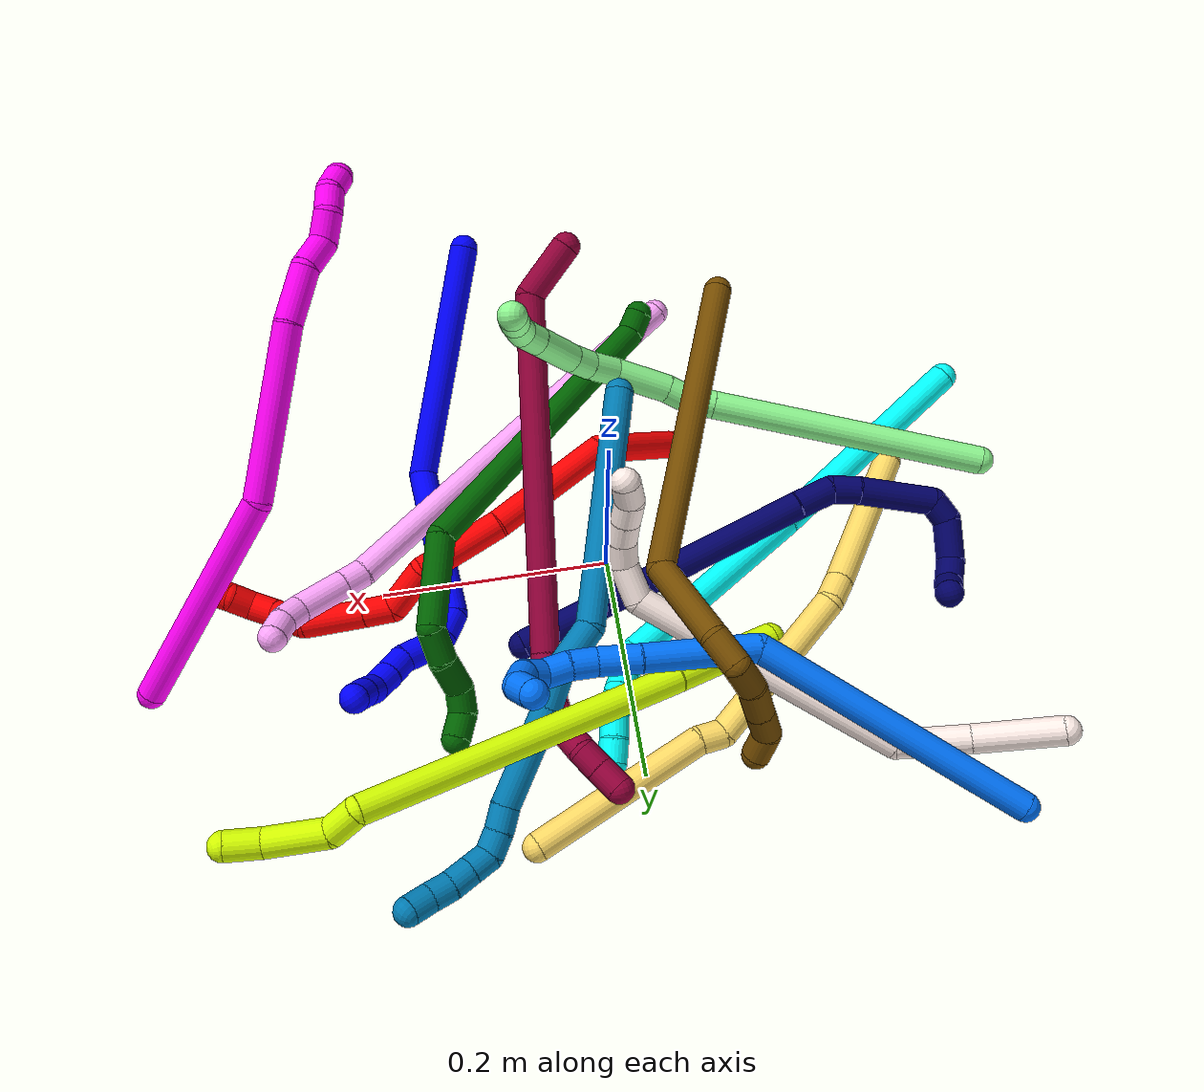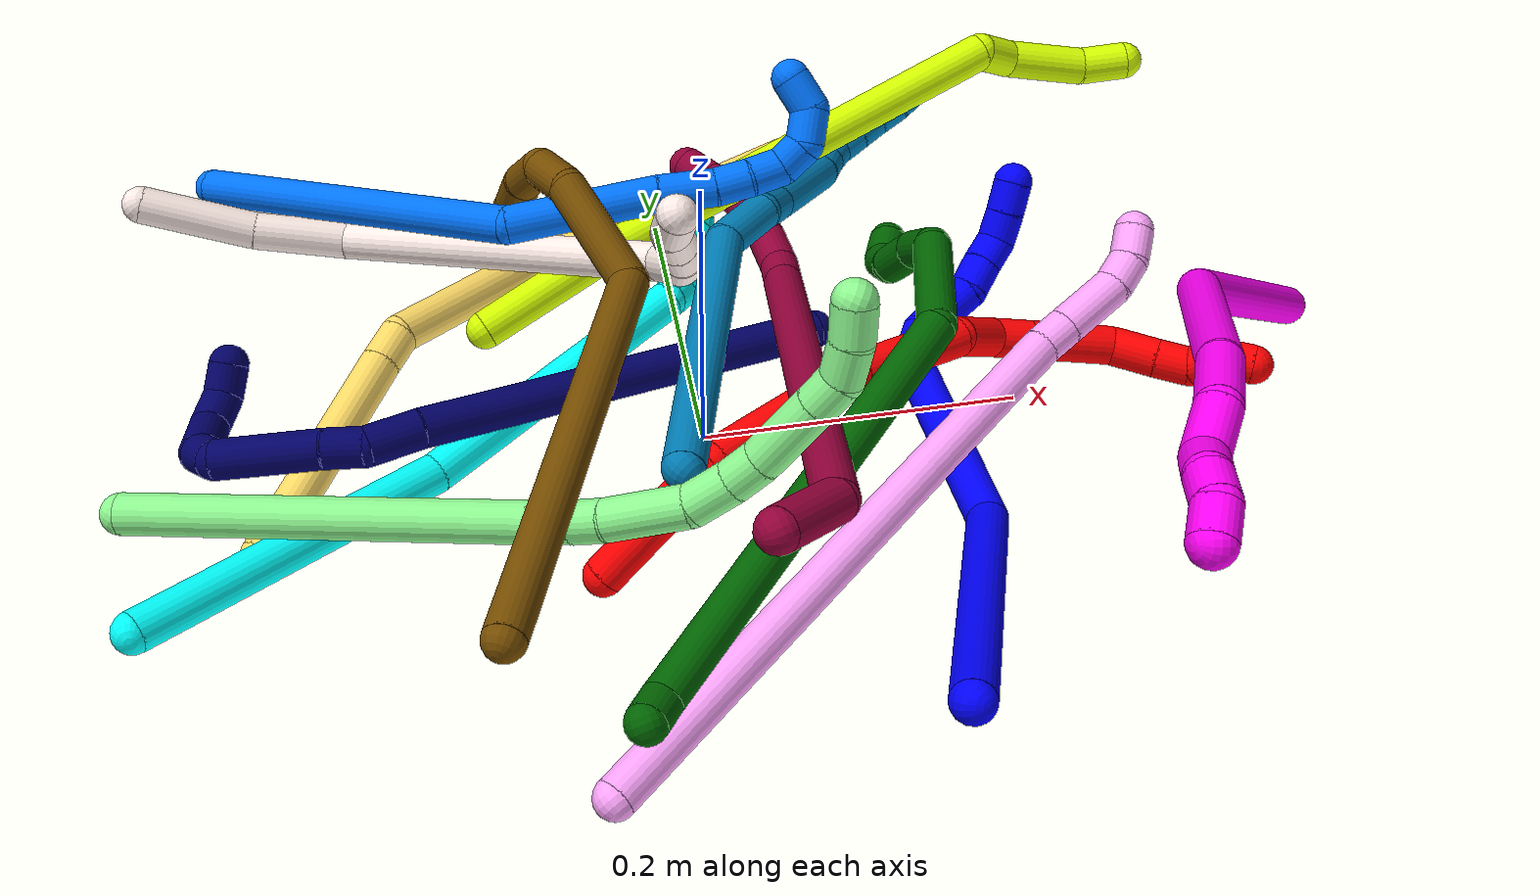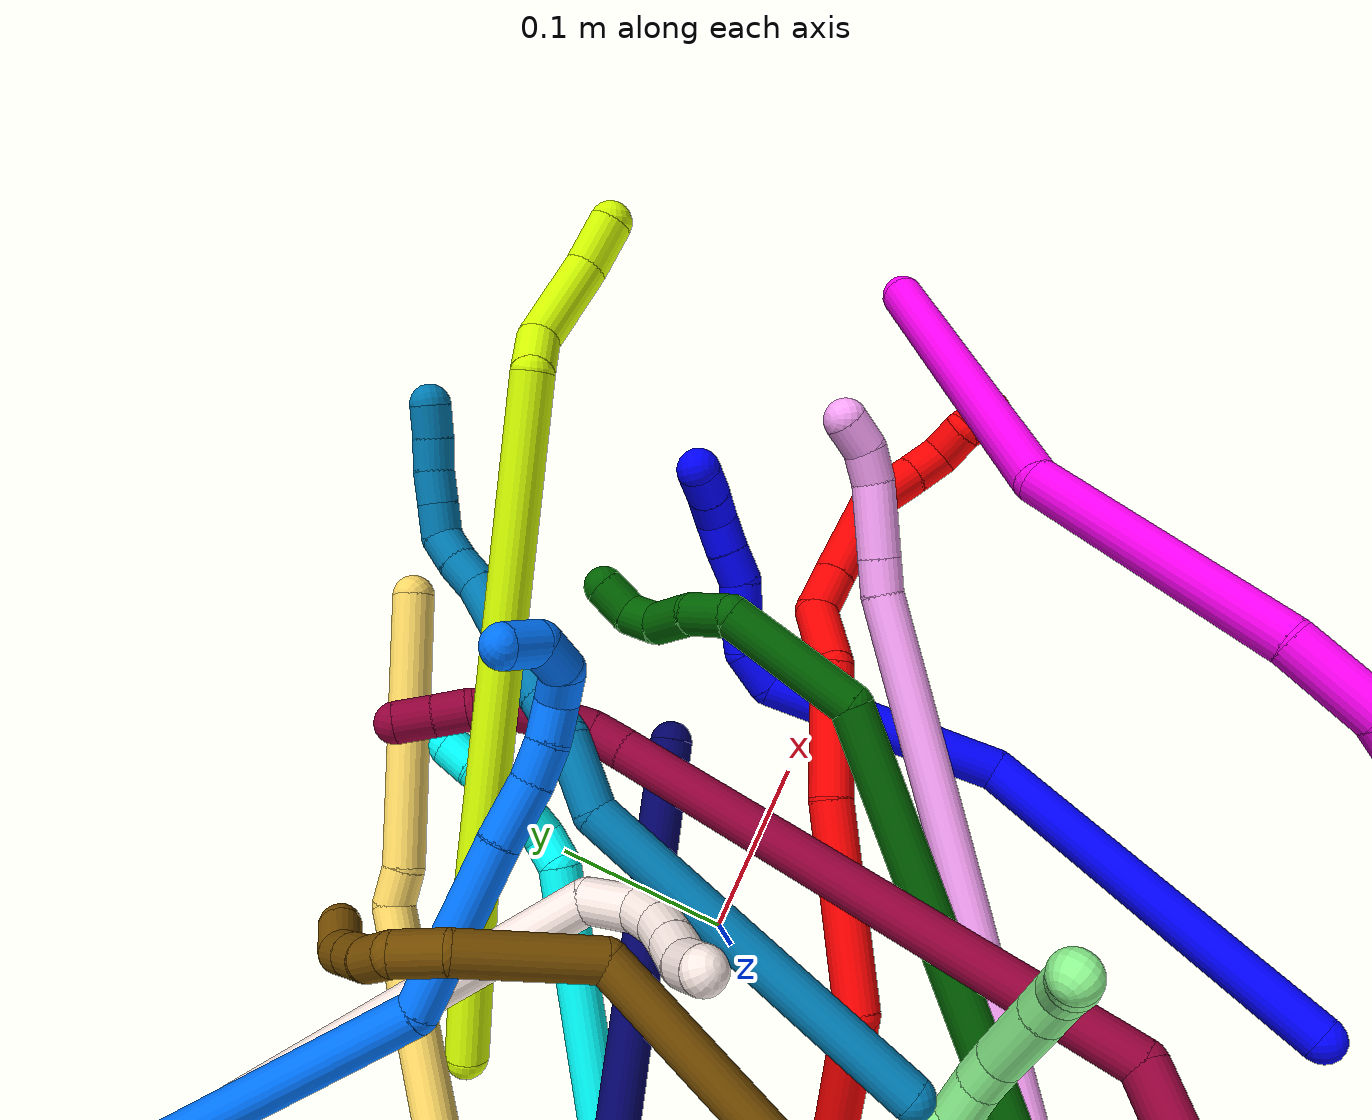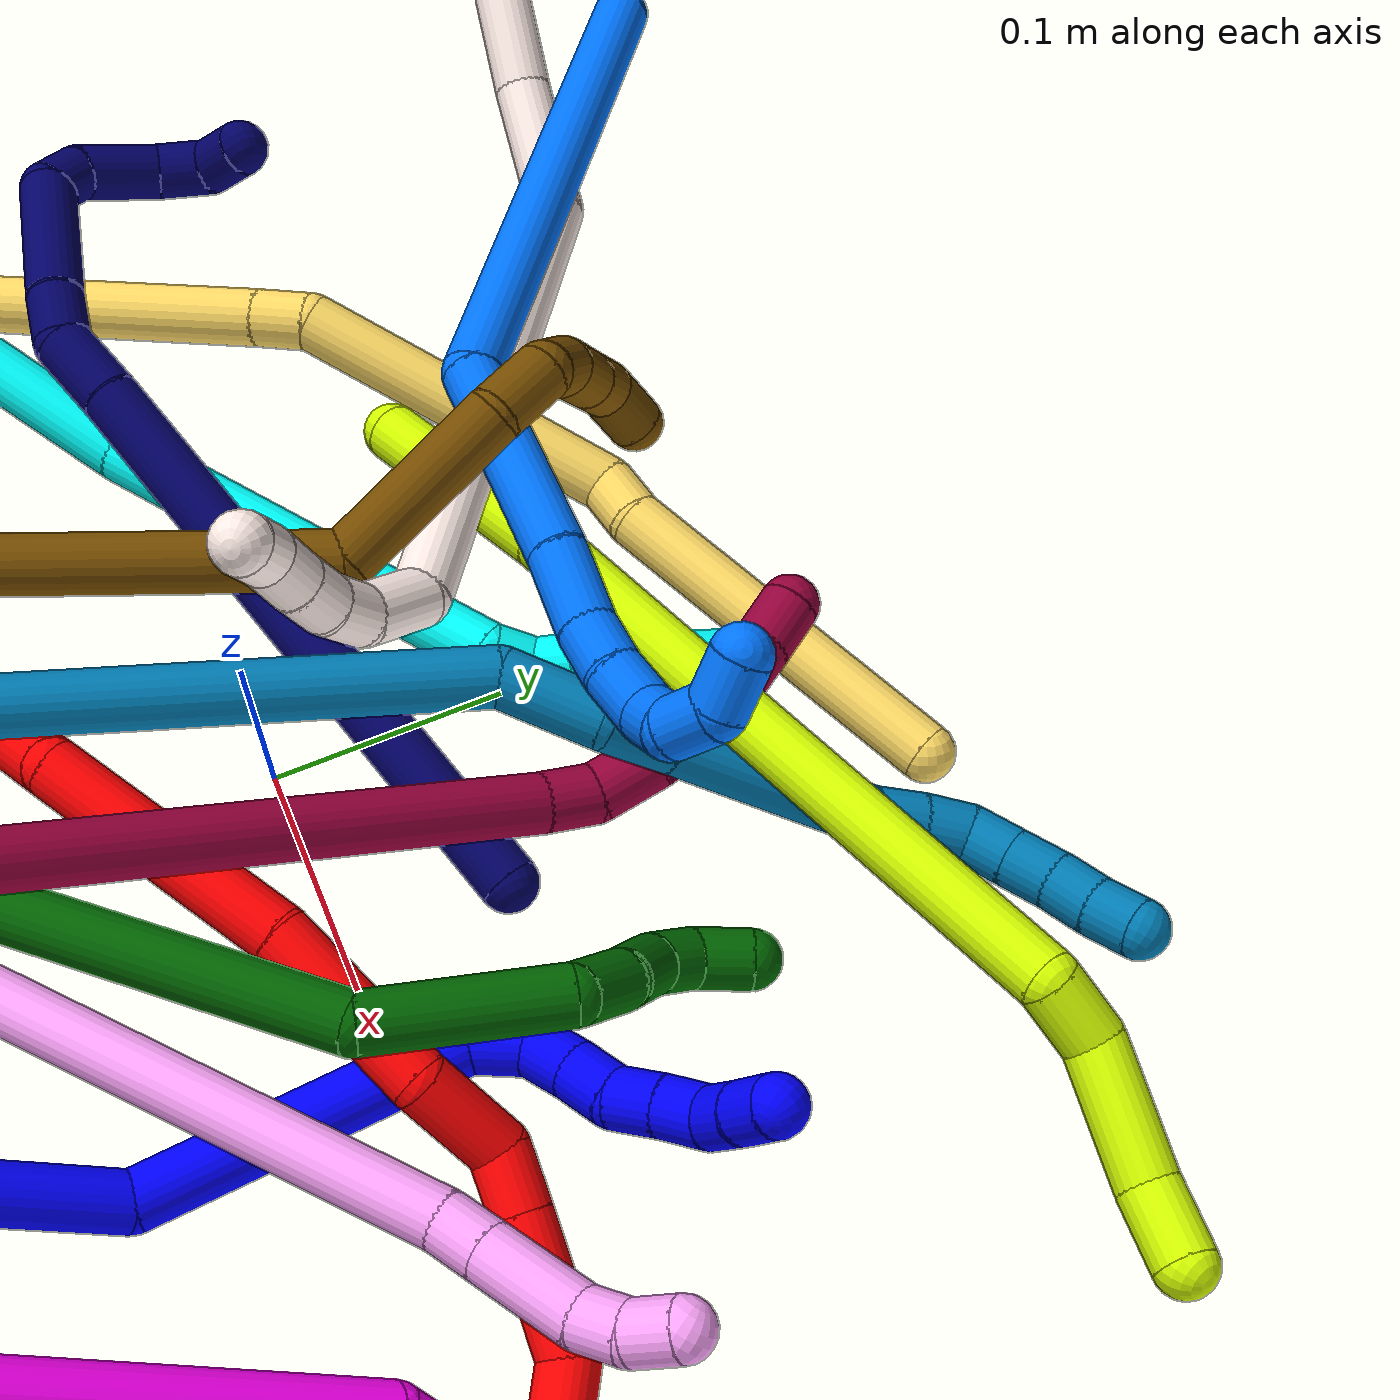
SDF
<sdf version="1.7">
 <world name="default">
  <plugin name="TubeGeneratorPlugin" filename="libtube_generator_plugin.so"/>
  <model name="photoneo_s_sensor">
   <static>1</static>
   <pose>0 0 2 1.57079 1.57079 3.14159</pose>
   <link name="link">
    <inertial><mass>0.1</mass></inertial>
    <sensor name="sensor" type="depth">
     <update_rate>30</update_rate>
     <camera>
      <horizontal_fov>1.22</horizontal_fov>
      <image><width>1920</width><height>1200</height><format>B8G8R8</format></image>
      <clip><near>0.1</near><far>4</far></clip>
      <depth_camera><output>points</output></depth_camera>
     </camera>
     <plugin name="camera_plugin" filename="libgazebo_ros_depth_camera.so">
      <baseline>0.2</baseline>
      <alwaysOn>1</alwaysOn>
      <updateRate>0.0</updateRate>
      <cameraName>camera_ir</cameraName>
      <imageTopicName>/camera/color/image_raw</imageTopicName>
      <cameraInfoTopicName>/camera/color/camera_info</cameraInfoTopicName>
      <depthImageTopicName>/camera/depth/image_raw</depthImageTopicName>
      <depthImageCameraInfoTopicName>/camera/depth/camera_info</depthImageCameraInfoTopicName>
      <pointCloudTopicName>/camera/depth/points</pointCloudTopicName>
      <frameName>fr_optical</frameName>
      <pointCloudCutoff>0.1</pointCloudCutoff>
      <pointCloudCutoffMax>2.0</pointCloudCutoffMax>
      <distortionK1>0</distortionK1>
      <distortionK2>0</distortionK2>
      <distortionK3>0</distortionK3>
      <distortionT1>0</distortionT1>
      <distortionT2>0</distortionT2>
      <CxPrime>0</CxPrime>
      <Cx>0</Cx>
      <Cy>0</Cy>
      <focalLength>0</focalLength>
      <hackBaseline>0</hackBaseline>
     </plugin>
    </sensor>
   </link>
  </model>
  <gravity>0 0 -9.8</gravity>
  <magnetic_field>6e-06 2.3e-05 -4.2e-05</magnetic_field>
  <atmosphere type="adiabatic"/>
  <physics name="default_physics" default="0" type="ode">
   <max_step_size>0.003</max_step_size>
   <real_time_factor>1</real_time_factor>
   <real_time_update_rate>1000</real_time_update_rate>
   <max_contacts>10000</max_contacts>
   <ode>
    <solver>
     <type>quick</type>
     <iters>100</iters>
     <sor>1.3</sor>
     <use_dynamic_moi_rescaling>0</use_dynamic_moi_rescaling>
    </solver>
    <constraints>
     <contact_max_correcting_vel>0</contact_max_correcting_vel>
     <contact_surface_layer>0.001</contact_surface_layer>
     <cfm>0</cfm>
     <erp>0.2</erp>
    </constraints>
   </ode>
  </physics>
  <scene><ambient>0.4 0.4 0.4 1</ambient><background>0.7 0.7 0.7 1</background><shadows>0</shadows></scene>
  <audio><device>default</device></audio>
  <spherical_coordinates>
   <surface_model>EARTH_WGS84</surface_model>
   <latitude_deg>0</latitude_deg>
   <longitude_deg>0</longitude_deg>
   <elevation>0</elevation>
   <heading_deg>0</heading_deg>
  </spherical_coordinates>
  <model name="bin">
   <static>1</static>
   <link name="bottom">
    <collision name="collision-bottom">
     <pose>0 0 -0.01 0 -0 0</pose>
     <geometry><box><size>0.8 0.6 0.02</size></box></geometry>
     <surface>
      <friction><ode><mu>100</mu><mu2>100</mu2></ode></friction>
      <contact><collide_bitmask>65535</collide_bitmask></contact>
     </surface>
    </collision>
   </link>
   <link name="west_wall">
    <collision name="collision-west_wall">
     <pose>-0.41 0 0.1 0 -0 0</pose>
     <geometry><box><size>0.02 0.6 0.2</size></box></geometry>
     <surface>
      <friction><ode><mu>100</mu><mu2>100</mu2></ode></friction>
      <contact><collide_bitmask>65535</collide_bitmask></contact>
     </surface>
    </collision>
   </link>
   <link name="east_wall">
    <collision name="collision-east_wall">
     <pose>0.41 0 0.1 0 -0 0</pose>
     <geometry><box><size>0.02 0.6 0.2</size></box></geometry>
     <surface>
      <friction><ode><mu>100</mu><mu2>100</mu2></ode></friction>
      <contact><collide_bitmask>65535</collide_bitmask></contact>
     </surface>
    </collision>
   </link>
   <link name="south_wall">
    <collision name="collision-south_wall">
     <pose>0 -0.31 0.1 0 -0 0</pose>
     <geometry><box><size>0.8 0.02 0.2</size></box></geometry>
     <surface>
      <friction><ode><mu>100</mu><mu2>100</mu2></ode></friction>
      <contact><collide_bitmask>65535</collide_bitmask></contact>
     </surface>
    </collision>
   </link>
   <link name="north_wall">
    <collision name="collision-north_wall">
     <pose>0 0.31 0.1 0 -0 0</pose>
     <geometry><box><size>0.8 0.02 0.2</size></box></geometry>
     <surface>
      <friction><ode><mu>100</mu><mu2>100</mu2></ode></friction>
      <contact><collide_bitmask>65535</collide_bitmask></contact>
     </surface>
    </collision>
   </link>
  </model>
  <model name="1">
   <static>0</static>
   <link name="1">
    <collision name="collision-cylinder-e_1_1_4">
     <pose>0.033847 0.066447 -0.074614 -2.41403 0.326631 -0.816934</pose>
     <geometry><cylinder><radius>0.0125</radius><length>0.210978</length></cylinder></geometry>
     <surface>
      <friction><ode><mu>1.16</mu><mu2>1.16</mu2><slip1>0</slip1><slip2>0</slip2></ode></friction>
      <contact><ode><kp>1e+06</kp><kd>1</kd><max_vel>0</max_vel><min_depth>0.001</min_depth></ode></contact>
     </surface>
    </collision>
    <visual name="visual-cylinder-e_1_1_4">
     <pose>0.033847 0.066447 -0.074614 -2.41403 0.326631 -0.816934</pose>
     <geometry><cylinder><radius>0.0125</radius><length>0.210978</length></cylinder></geometry>
     <material><ambient>0 0 1 1</ambient></material>
    </visual>
    <collision name="collision-cylinder-e_2_4_5">
     <pose>0.051176 0.173754 -0.204266 -2.50297 -0.236446 0.689781</pose>
     <geometry><cylinder><radius>0.0125</radius><length>0.14102</length></cylinder></geometry>
     <surface>
      <friction><ode><mu>1.16</mu><mu2>1.16</mu2><slip1>0</slip1><slip2>0</slip2></ode></friction>
      <contact><ode><kp>1e+06</kp><kd>1</kd><max_vel>0</max_vel><min_depth>0.001</min_depth></ode></contact>
     </surface>
    </collision>
    <visual name="visual-cylinder-e_2_4_5">
     <pose>0.051176 0.173754 -0.204266 -2.50297 -0.236446 0.689781</pose>
     <geometry><cylinder><radius>0.0125</radius><length>0.14102</length></cylinder></geometry>
     <material><ambient>0 0 1 1</ambient></material>
    </visual>
    <collision name="collision-cylinder-e_3_5_6">
     <pose>0.034077 0.226233 -0.263559 -1.92185 -0.047053 0.067329</pose>
     <geometry><cylinder><radius>0.0125</radius><length>0.024772</length></cylinder></geometry>
     <surface>
      <friction><ode><mu>1.16</mu><mu2>1.16</mu2><slip1>0</slip1><slip2>0</slip2></ode></friction>
      <contact><ode><kp>1e+06</kp><kd>1</kd><max_vel>0</max_vel><min_depth>0.001</min_depth></ode></contact>
     </surface>
    </collision>
    <visual name="visual-cylinder-e_3_5_6">
     <pose>0.034077 0.226233 -0.263559 -1.92185 -0.047053 0.067329</pose>
     <geometry><cylinder><radius>0.0125</radius><length>0.024772</length></cylinder></geometry>
     <material><ambient>0 0 1 1</ambient></material>
    </visual>
    <collision name="collision-cylinder-e_4_6_7">
     <pose>0.035555 0.248048 -0.267029 -1.49402 0.198817 -0.184197</pose>
     <geometry><cylinder><radius>0.0125</radius><length>0.020866</length></cylinder></geometry>
     <surface>
      <friction><ode><mu>1.16</mu><mu2>1.16</mu2><slip1>0</slip1><slip2>0</slip2></ode></friction>
      <contact><ode><kp>1e+06</kp><kd>1</kd><max_vel>0</max_vel><min_depth>0.001</min_depth></ode></contact>
     </surface>
    </collision>
    <visual name="visual-cylinder-e_4_6_7">
     <pose>0.035555 0.248048 -0.267029 -1.49402 0.198817 -0.184197</pose>
     <geometry><cylinder><radius>0.0125</radius><length>0.020866</length></cylinder></geometry>
     <material><ambient>0 0 1 1</ambient></material>
    </visual>
    <collision name="collision-cylinder-e_5_7_8">
     <pose>0.0391 0.268576 -0.263858 -1.34376 0.139081 -0.110679</pose>
     <geometry><cylinder><radius>0.0125</radius><length>0.021414</length></cylinder></geometry>
     <surface>
      <friction><ode><mu>1.16</mu><mu2>1.16</mu2><slip1>0</slip1><slip2>0</slip2></ode></friction>
      <contact><ode><kp>1e+06</kp><kd>1</kd><max_vel>0</max_vel><min_depth>0.001</min_depth></ode></contact>
     </surface>
    </collision>
    <visual name="visual-cylinder-e_5_7_8">
     <pose>0.0391 0.268576 -0.263858 -1.34376 0.139081 -0.110679</pose>
     <geometry><cylinder><radius>0.0125</radius><length>0.021414</length></cylinder></geometry>
     <material><ambient>0 0 1 1</ambient></material>
    </visual>
    <collision name="collision-cylinder-e_6_8_9">
     <pose>0.039728 0.289074 -0.262378 -1.6598 -0.083667 0.091456</pose>
     <geometry><cylinder><radius>0.0125</radius><length>0.020486</length></cylinder></geometry>
     <surface>
      <friction><ode><mu>1.16</mu><mu2>1.16</mu2><slip1>0</slip1><slip2>0</slip2></ode></friction>
      <contact><ode><kp>1e+06</kp><kd>1</kd><max_vel>0</max_vel><min_depth>0.001</min_depth></ode></contact>
     </surface>
    </collision>
    <visual name="visual-cylinder-e_6_8_9">
     <pose>0.039728 0.289074 -0.262378 -1.6598 -0.083667 0.091456</pose>
     <geometry><cylinder><radius>0.0125</radius><length>0.020486</length></cylinder></geometry>
     <material><ambient>0 0 1 1</ambient></material>
    </visual>
    <collision name="collision-cylinder-e_7_9_10">
     <pose>0.03846 0.309331 -0.263706 -1.61241 -0.04078 0.042512</pose>
     <geometry><cylinder><radius>0.0125</radius><length>0.020213</length></cylinder></geometry>
     <surface>
      <friction><ode><mu>1.16</mu><mu2>1.16</mu2><slip1>0</slip1><slip2>0</slip2></ode></friction>
      <contact><ode><kp>1e+06</kp><kd>1</kd><max_vel>0</max_vel><min_depth>0.001</min_depth></ode></contact>
     </surface>
    </collision>
    <visual name="visual-cylinder-e_7_9_10">
     <pose>0.03846 0.309331 -0.263706 -1.61241 -0.04078 0.042512</pose>
     <geometry><cylinder><radius>0.0125</radius><length>0.020213</length></cylinder></geometry>
     <material><ambient>0 0 1 1</ambient></material>
    </visual>
    <collision name="collision-cylinder-e_8_10_11">
     <pose>0.032662 0.327586 -0.261613 -1.27224 -0.562477 0.420412</pose>
     <geometry><cylinder><radius>0.0125</radius><length>0.020201</length></cylinder></geometry>
     <surface>
      <friction><ode><mu>1.16</mu><mu2>1.16</mu2><slip1>0</slip1><slip2>0</slip2></ode></friction>
      <contact><ode><kp>1e+06</kp><kd>1</kd><max_vel>0</max_vel><min_depth>0.001</min_depth></ode></contact>
     </surface>
    </collision>
    <visual name="visual-cylinder-e_8_10_11">
     <pose>0.032662 0.327586 -0.261613 -1.27224 -0.562477 0.420412</pose>
     <geometry><cylinder><radius>0.0125</radius><length>0.020201</length></cylinder></geometry>
     <material><ambient>0 0 1 1</ambient></material>
    </visual>
    <collision name="collision-cylinder-e_9_11_2">
     <pose>0.021776 0.343921 -0.257215 -1.34403 -0.580606 0.466666</pose>
     <geometry><cylinder><radius>0.0125</radius><length>0.020051</length></cylinder></geometry>
     <surface>
      <friction><ode><mu>1.16</mu><mu2>1.16</mu2><slip1>0</slip1><slip2>0</slip2></ode></friction>
      <contact><ode><kp>1e+06</kp><kd>1</kd><max_vel>0</max_vel><min_depth>0.001</min_depth></ode></contact>
     </surface>
    </collision>
    <visual name="visual-cylinder-e_9_11_2">
     <pose>0.021776 0.343921 -0.257215 -1.34403 -0.580606 0.466666</pose>
     <geometry><cylinder><radius>0.0125</radius><length>0.020051</length></cylinder></geometry>
     <material><ambient>0 0 1 1</ambient></material>
    </visual>
    <collision name="collision-sphere-2">
     <pose>0.016277 0.352089 -0.25533 0 -0 0</pose>
     <geometry><sphere><radius>0.0125</radius></sphere></geometry>
     <surface>
      <friction><ode><mu>1.16</mu><mu2>1.16</mu2><slip1>0</slip1><slip2>0</slip2></ode></friction>
      <contact><ode><kp>1e+06</kp><kd>1</kd><max_vel>0</max_vel><min_depth>0.001</min_depth></ode></contact>
     </surface>
    </collision>
    <visual name="visual-sphere-2">
     <pose>0.016277 0.352089 -0.25533 0 -0 0</pose>
     <geometry><sphere><radius>0.0125</radius></sphere></geometry>
     <material><ambient>0 0 1 1</ambient></material>
    </visual>
    <collision name="collision-sphere-11">
     <pose>0.027275 0.335753 -0.259099 0 -0 0</pose>
     <geometry><sphere><radius>0.0125</radius></sphere></geometry>
     <surface>
      <friction><ode><mu>1.16</mu><mu2>1.16</mu2><slip1>0</slip1><slip2>0</slip2></ode></friction>
      <contact><ode><kp>1e+06</kp><kd>1</kd><max_vel>0</max_vel><min_depth>0.001</min_depth></ode></contact>
     </surface>
    </collision>
    <visual name="visual-sphere-11">
     <pose>0.027275 0.335753 -0.259099 0 -0 0</pose>
     <geometry><sphere><radius>0.0125</radius></sphere></geometry>
     <material><ambient>0 0 1 1</ambient></material>
    </visual>
    <collision name="collision-sphere-10">
     <pose>0.038048 0.31942 -0.264126 0 -0 0</pose>
     <geometry><sphere><radius>0.0125</radius></sphere></geometry>
     <surface>
      <friction><ode><mu>1.16</mu><mu2>1.16</mu2><slip1>0</slip1><slip2>0</slip2></ode></friction>
      <contact><ode><kp>1e+06</kp><kd>1</kd><max_vel>0</max_vel><min_depth>0.001</min_depth></ode></contact>
     </surface>
    </collision>
    <visual name="visual-sphere-10">
     <pose>0.038048 0.31942 -0.264126 0 -0 0</pose>
     <geometry><sphere><radius>0.0125</radius></sphere></geometry>
     <material><ambient>0 0 1 1</ambient></material>
    </visual>
    <collision name="collision-sphere-9">
     <pose>0.038872 0.299241 -0.263286 0 -0 0</pose>
     <geometry><sphere><radius>0.0125</radius></sphere></geometry>
     <surface>
      <friction><ode><mu>1.16</mu><mu2>1.16</mu2><slip1>0</slip1><slip2>0</slip2></ode></friction>
      <contact><ode><kp>1e+06</kp><kd>1</kd><max_vel>0</max_vel><min_depth>0.001</min_depth></ode></contact>
     </surface>
    </collision>
    <visual name="visual-sphere-9">
     <pose>0.038872 0.299241 -0.263286 0 -0 0</pose>
     <geometry><sphere><radius>0.0125</radius></sphere></geometry>
     <material><ambient>0 0 1 1</ambient></material>
    </visual>
    <collision name="collision-sphere-4">
     <pose>0.067693 0.132894 -0.149227 0 -0 0</pose>
     <geometry><sphere><radius>0.0125</radius></sphere></geometry>
     <surface>
      <friction><ode><mu>1.16</mu><mu2>1.16</mu2><slip1>0</slip1><slip2>0</slip2></ode></friction>
      <contact><ode><kp>1e+06</kp><kd>1</kd><max_vel>0</max_vel><min_depth>0.001</min_depth></ode></contact>
     </surface>
    </collision>
    <visual name="visual-sphere-4">
     <pose>0.067693 0.132894 -0.149227 0 -0 0</pose>
     <geometry><sphere><radius>0.0125</radius></sphere></geometry>
     <material><ambient>0 0 1 1</ambient></material>
    </visual>
    <collision name="collision-sphere-1">
     <geometry><sphere><radius>0.0125</radius></sphere></geometry>
     <surface>
      <friction><ode><mu>1.16</mu><mu2>1.16</mu2><slip1>0</slip1><slip2>0</slip2></ode></friction>
      <contact><ode><kp>1e+06</kp><kd>1</kd><max_vel>0</max_vel><min_depth>0.001</min_depth></ode></contact>
     </surface>
    </collision>
    <visual name="visual-sphere-1">
     <geometry><sphere><radius>0.0125</radius></sphere></geometry>
     <material><ambient>0 0 1 1</ambient></material>
    </visual>
    <collision name="collision-sphere-8">
     <pose>0.040584 0.278908 -0.261471 0 -0 0</pose>
     <geometry><sphere><radius>0.0125</radius></sphere></geometry>
     <surface>
      <friction><ode><mu>1.16</mu><mu2>1.16</mu2><slip1>0</slip1><slip2>0</slip2></ode></friction>
      <contact><ode><kp>1e+06</kp><kd>1</kd><max_vel>0</max_vel><min_depth>0.001</min_depth></ode></contact>
     </surface>
    </collision>
    <visual name="visual-sphere-8">
     <pose>0.040584 0.278908 -0.261471 0 -0 0</pose>
     <geometry><sphere><radius>0.0125</radius></sphere></geometry>
     <material><ambient>0 0 1 1</ambient></material>
    </visual>
    <collision name="collision-sphere-5">
     <pose>0.034659 0.214615 -0.259304 0 -0 0</pose>
     <geometry><sphere><radius>0.0125</radius></sphere></geometry>
     <surface>
      <friction><ode><mu>1.16</mu><mu2>1.16</mu2><slip1>0</slip1><slip2>0</slip2></ode></friction>
      <contact><ode><kp>1e+06</kp><kd>1</kd><max_vel>0</max_vel><min_depth>0.001</min_depth></ode></contact>
     </surface>
    </collision>
    <visual name="visual-sphere-5">
     <pose>0.034659 0.214615 -0.259304 0 -0 0</pose>
     <geometry><sphere><radius>0.0125</radius></sphere></geometry>
     <material><ambient>0 0 1 1</ambient></material>
    </visual>
    <collision name="collision-sphere-6">
     <pose>0.033494 0.237851 -0.267813 0 -0 0</pose>
     <geometry><sphere><radius>0.0125</radius></sphere></geometry>
     <surface>
      <friction><ode><mu>1.16</mu><mu2>1.16</mu2><slip1>0</slip1><slip2>0</slip2></ode></friction>
      <contact><ode><kp>1e+06</kp><kd>1</kd><max_vel>0</max_vel><min_depth>0.001</min_depth></ode></contact>
     </surface>
    </collision>
    <visual name="visual-sphere-6">
     <pose>0.033494 0.237851 -0.267813 0 -0 0</pose>
     <geometry><sphere><radius>0.0125</radius></sphere></geometry>
     <material><ambient>0 0 1 1</ambient></material>
    </visual>
    <collision name="collision-sphere-7">
     <pose>0.037615 0.258245 -0.266245 0 -0 0</pose>
     <geometry><sphere><radius>0.0125</radius></sphere></geometry>
     <surface>
      <friction><ode><mu>1.16</mu><mu2>1.16</mu2><slip1>0</slip1><slip2>0</slip2></ode></friction>
      <contact><ode><kp>1e+06</kp><kd>1</kd><max_vel>0</max_vel><min_depth>0.001</min_depth></ode></contact>
     </surface>
    </collision>
    <visual name="visual-sphere-7">
     <pose>0.037615 0.258245 -0.266245 0 -0 0</pose>
     <geometry><sphere><radius>0.0125</radius></sphere></geometry>
     <material><ambient>0 0 1 1</ambient></material>
    </visual>
    <inertial>
     <pose>0.038938 0.161481 -0.166891 0 -0 0</pose>
     <mass>0.5</mass>
     <inertia>
      <ixx>0.000307</ixx>
      <ixy>0</ixy>
      <ixz>0</ixz>
      <iyy>-0.000777</iyy>
      <iyz>0</iyz>
      <izz>-0.000864</izz>
     </inertia>
    </inertial>
   </link>
   <pose>0.085529 -0.288502 0.103766 0.561407 0.904912 -0.360126</pose>
  </model>
  <model name="2">
   <static>0</static>
   <link name="2">
    <collision name="collision-cylinder-e_1_1_4">
     <pose>0.025768 0.038272 -0.009733 -1.81983 0.578141 -0.730662</pose>
     <geometry><cylinder><radius>0.0125</radius><length>0.094307</length></cylinder></geometry>
     <surface>
      <friction><ode><mu>1.16</mu><mu2>1.16</mu2><slip1>0</slip1><slip2>0</slip2></ode></friction>
      <contact><ode><kp>1e+06</kp><kd>1</kd><max_vel>0</max_vel><min_depth>0.001</min_depth></ode></contact>
     </surface>
    </collision>
    <visual name="visual-cylinder-e_1_1_4">
     <pose>0.025768 0.038272 -0.009733 -1.81983 0.578141 -0.730662</pose>
     <geometry><cylinder><radius>0.0125</radius><length>0.094307</length></cylinder></geometry>
     <material><ambient>1 0 0 1</ambient></material>
    </visual>
    <collision name="collision-cylinder-e_2_4_5">
     <pose>0.077216 0.101775 -0.063304 -2.61935 0.4698 -1.46072</pose>
     <geometry><cylinder><radius>0.0125</radius><length>0.113452</length></cylinder></geometry>
     <surface>
      <friction><ode><mu>1.16</mu><mu2>1.16</mu2><slip1>0</slip1><slip2>0</slip2></ode></friction>
      <contact><ode><kp>1e+06</kp><kd>1</kd><max_vel>0</max_vel><min_depth>0.001</min_depth></ode></contact>
     </surface>
    </collision>
    <visual name="visual-cylinder-e_2_4_5">
     <pose>0.077216 0.101775 -0.063304 -2.61935 0.4698 -1.46072</pose>
     <geometry><cylinder><radius>0.0125</radius><length>0.113452</length></cylinder></geometry>
     <material><ambient>1 0 0 1</ambient></material>
    </visual>
    <collision name="collision-cylinder-e_3_5_6">
     <pose>0.12427 0.138392 -0.136561 -2.77232 0.595502 -2.04816</pose>
     <geometry><cylinder><radius>0.0125</radius><length>0.076209</length></cylinder></geometry>
     <surface>
      <friction><ode><mu>1.16</mu><mu2>1.16</mu2><slip1>0</slip1><slip2>0</slip2></ode></friction>
      <contact><ode><kp>1e+06</kp><kd>1</kd><max_vel>0</max_vel><min_depth>0.001</min_depth></ode></contact>
     </surface>
    </collision>
    <visual name="visual-cylinder-e_3_5_6">
     <pose>0.12427 0.138392 -0.136561 -2.77232 0.595502 -2.04816</pose>
     <geometry><cylinder><radius>0.0125</radius><length>0.076209</length></cylinder></geometry>
     <material><ambient>1 0 0 1</ambient></material>
    </visual>
    <collision name="collision-cylinder-e_4_6_7">
     <pose>0.151421 0.148546 -0.186156 3.08063 0.278384 2.71299</pose>
     <geometry><cylinder><radius>0.0125</radius><length>0.042045</length></cylinder></geometry>
     <surface>
      <friction><ode><mu>1.16</mu><mu2>1.16</mu2><slip1>0</slip1><slip2>0</slip2></ode></friction>
      <contact><ode><kp>1e+06</kp><kd>1</kd><max_vel>0</max_vel><min_depth>0.001</min_depth></ode></contact>
     </surface>
    </collision>
    <visual name="visual-cylinder-e_4_6_7">
     <pose>0.151421 0.148546 -0.186156 3.08063 0.278384 2.71299</pose>
     <geometry><cylinder><radius>0.0125</radius><length>0.042045</length></cylinder></geometry>
     <material><ambient>1 0 0 1</ambient></material>
    </visual>
    <collision name="collision-cylinder-e_5_7_8">
     <pose>0.167895 0.147711 -0.213655 -3.08751 0.969795 -3.03902</pose>
     <geometry><cylinder><radius>0.0125</radius><length>0.025939</length></cylinder></geometry>
     <surface>
      <friction><ode><mu>1.16</mu><mu2>1.16</mu2><slip1>0</slip1><slip2>0</slip2></ode></friction>
      <contact><ode><kp>1e+06</kp><kd>1</kd><max_vel>0</max_vel><min_depth>0.001</min_depth></ode></contact>
     </surface>
    </collision>
    <visual name="visual-cylinder-e_5_7_8">
     <pose>0.167895 0.147711 -0.213655 -3.08751 0.969795 -3.03902</pose>
     <geometry><cylinder><radius>0.0125</radius><length>0.025939</length></cylinder></geometry>
     <material><ambient>1 0 0 1</ambient></material>
    </visual>
    <collision name="collision-cylinder-e_6_8_9">
     <pose>0.20169 0.1488 -0.236328 -3.09646 0.983789 -3.05741</pose>
     <geometry><cylinder><radius>0.0125</radius><length>0.055484</length></cylinder></geometry>
     <surface>
      <friction><ode><mu>1.16</mu><mu2>1.16</mu2><slip1>0</slip1><slip2>0</slip2></ode></friction>
      <contact><ode><kp>1e+06</kp><kd>1</kd><max_vel>0</max_vel><min_depth>0.001</min_depth></ode></contact>
     </surface>
    </collision>
    <visual name="visual-cylinder-e_6_8_9">
     <pose>0.20169 0.1488 -0.236328 -3.09646 0.983789 -3.05741</pose>
     <geometry><cylinder><radius>0.0125</radius><length>0.055484</length></cylinder></geometry>
     <material><ambient>1 0 0 1</ambient></material>
    </visual>
    <collision name="collision-cylinder-e_7_9_10">
     <pose>0.239419 0.147835 -0.253201 2.31376 1.41805 2.19504</pose>
     <geometry><cylinder><radius>0.0125</radius><length>0.029608</length></cylinder></geometry>
     <surface>
      <friction><ode><mu>1.16</mu><mu2>1.16</mu2><slip1>0</slip1><slip2>0</slip2></ode></friction>
      <contact><ode><kp>1e+06</kp><kd>1</kd><max_vel>0</max_vel><min_depth>0.001</min_depth></ode></contact>
     </surface>
    </collision>
    <visual name="visual-cylinder-e_7_9_10">
     <pose>0.239419 0.147835 -0.253201 2.31376 1.41805 2.19504</pose>
     <geometry><cylinder><radius>0.0125</radius><length>0.029608</length></cylinder></geometry>
     <material><ambient>1 0 0 1</ambient></material>
    </visual>
    <collision name="collision-cylinder-e_8_10_11">
     <pose>0.264896 0.145219 -0.25599 2.49402 1.42553 2.4009</pose>
     <geometry><cylinder><radius>0.0125</radius><length>0.021922</length></cylinder></geometry>
     <surface>
      <friction><ode><mu>1.16</mu><mu2>1.16</mu2><slip1>0</slip1><slip2>0</slip2></ode></friction>
      <contact><ode><kp>1e+06</kp><kd>1</kd><max_vel>0</max_vel><min_depth>0.001</min_depth></ode></contact>
     </surface>
    </collision>
    <visual name="visual-cylinder-e_8_10_11">
     <pose>0.264896 0.145219 -0.25599 2.49402 1.42553 2.4009</pose>
     <geometry><cylinder><radius>0.0125</radius><length>0.021922</length></cylinder></geometry>
     <material><ambient>1 0 0 1</ambient></material>
    </visual>
    <collision name="collision-cylinder-e_9_11_12">
     <pose>0.28468 0.148983 -0.256254 -1.36173 1.07571 -0.900295</pose>
     <geometry><cylinder><radius>0.0125</radius><length>0.020315</length></cylinder></geometry>
     <surface>
      <friction><ode><mu>1.16</mu><mu2>1.16</mu2><slip1>0</slip1><slip2>0</slip2></ode></friction>
      <contact><ode><kp>1e+06</kp><kd>1</kd><max_vel>0</max_vel><min_depth>0.001</min_depth></ode></contact>
     </surface>
    </collision>
    <visual name="visual-cylinder-e_9_11_12">
     <pose>0.28468 0.148983 -0.256254 -1.36173 1.07571 -0.900295</pose>
     <geometry><cylinder><radius>0.0125</radius><length>0.020315</length></cylinder></geometry>
     <material><ambient>1 0 0 1</ambient></material>
    </visual>
    <collision name="collision-cylinder-e_10_12_2">
     <pose>0.303904 0.153197 -0.256376 2.71775 1.45153 2.66583</pose>
     <geometry><cylinder><radius>0.0125</radius><length>0.020719</length></cylinder></geometry>
     <surface>
      <friction><ode><mu>1.16</mu><mu2>1.16</mu2><slip1>0</slip1><slip2>0</slip2></ode></friction>
      <contact><ode><kp>1e+06</kp><kd>1</kd><max_vel>0</max_vel><min_depth>0.001</min_depth></ode></contact>
     </surface>
    </collision>
    <visual name="visual-cylinder-e_10_12_2">
     <pose>0.303904 0.153197 -0.256376 2.71775 1.45153 2.66583</pose>
     <geometry><cylinder><radius>0.0125</radius><length>0.020719</length></cylinder></geometry>
     <material><ambient>1 0 0 1</ambient></material>
    </visual>
    <collision name="collision-sphere-2">
     <pose>0.314189 0.15269 -0.2575 0 -0 0</pose>
     <geometry><sphere><radius>0.0125</radius></sphere></geometry>
     <surface>
      <friction><ode><mu>1.16</mu><mu2>1.16</mu2><slip1>0</slip1><slip2>0</slip2></ode></friction>
      <contact><ode><kp>1e+06</kp><kd>1</kd><max_vel>0</max_vel><min_depth>0.001</min_depth></ode></contact>
     </surface>
    </collision>
    <visual name="visual-sphere-2">
     <pose>0.314189 0.15269 -0.2575 0 -0 0</pose>
     <geometry><sphere><radius>0.0125</radius></sphere></geometry>
     <material><ambient>1 0 0 1</ambient></material>
    </visual>
    <collision name="collision-sphere-12">
     <pose>0.293618 0.153703 -0.255253 0 -0 0</pose>
     <geometry><sphere><radius>0.0125</radius></sphere></geometry>
     <surface>
      <friction><ode><mu>1.16</mu><mu2>1.16</mu2><slip1>0</slip1><slip2>0</slip2></ode></friction>
      <contact><ode><kp>1e+06</kp><kd>1</kd><max_vel>0</max_vel><min_depth>0.001</min_depth></ode></contact>
     </surface>
    </collision>
    <visual name="visual-sphere-12">
     <pose>0.293618 0.153703 -0.255253 0 -0 0</pose>
     <geometry><sphere><radius>0.0125</radius></sphere></geometry>
     <material><ambient>1 0 0 1</ambient></material>
    </visual>
    <collision name="collision-sphere-11">
     <pose>0.275742 0.144262 -0.257256 0 -0 0</pose>
     <geometry><sphere><radius>0.0125</radius></sphere></geometry>
     <surface>
      <friction><ode><mu>1.16</mu><mu2>1.16</mu2><slip1>0</slip1><slip2>0</slip2></ode></friction>
      <contact><ode><kp>1e+06</kp><kd>1</kd><max_vel>0</max_vel><min_depth>0.001</min_depth></ode></contact>
     </surface>
    </collision>
    <visual name="visual-sphere-11">
     <pose>0.275742 0.144262 -0.257256 0 -0 0</pose>
     <geometry><sphere><radius>0.0125</radius></sphere></geometry>
     <material><ambient>1 0 0 1</ambient></material>
    </visual>
    <collision name="collision-sphere-10">
     <pose>0.254051 0.146176 -0.254725 0 -0 0</pose>
     <geometry><sphere><radius>0.0125</radius></sphere></geometry>
     <surface>
      <friction><ode><mu>1.16</mu><mu2>1.16</mu2><slip1>0</slip1><slip2>0</slip2></ode></friction>
      <contact><ode><kp>1e+06</kp><kd>1</kd><max_vel>0</max_vel><min_depth>0.001</min_depth></ode></contact>
     </surface>
    </collision>
    <visual name="visual-sphere-10">
     <pose>0.254051 0.146176 -0.254725 0 -0 0</pose>
     <geometry><sphere><radius>0.0125</radius></sphere></geometry>
     <material><ambient>1 0 0 1</ambient></material>
    </visual>
    <collision name="collision-sphere-9">
     <pose>0.224788 0.149494 -0.251677 0 -0 0</pose>
     <geometry><sphere><radius>0.0125</radius></sphere></geometry>
     <surface>
      <friction><ode><mu>1.16</mu><mu2>1.16</mu2><slip1>0</slip1><slip2>0</slip2></ode></friction>
      <contact><ode><kp>1e+06</kp><kd>1</kd><max_vel>0</max_vel><min_depth>0.001</min_depth></ode></contact>
     </surface>
    </collision>
    <visual name="visual-sphere-9">
     <pose>0.224788 0.149494 -0.251677 0 -0 0</pose>
     <geometry><sphere><radius>0.0125</radius></sphere></geometry>
     <material><ambient>1 0 0 1</ambient></material>
    </visual>
    <collision name="collision-sphere-4">
     <pose>0.051536 0.076544 -0.019466 0 -0 0</pose>
     <geometry><sphere><radius>0.0125</radius></sphere></geometry>
     <surface>
      <friction><ode><mu>1.16</mu><mu2>1.16</mu2><slip1>0</slip1><slip2>0</slip2></ode></friction>
      <contact><ode><kp>1e+06</kp><kd>1</kd><max_vel>0</max_vel><min_depth>0.001</min_depth></ode></contact>
     </surface>
    </collision>
    <visual name="visual-sphere-4">
     <pose>0.051536 0.076544 -0.019466 0 -0 0</pose>
     <geometry><sphere><radius>0.0125</radius></sphere></geometry>
     <material><ambient>1 0 0 1</ambient></material>
    </visual>
    <collision name="collision-sphere-1">
     <geometry><sphere><radius>0.0125</radius></sphere></geometry>
     <surface>
      <friction><ode><mu>1.16</mu><mu2>1.16</mu2><slip1>0</slip1><slip2>0</slip2></ode></friction>
      <contact><ode><kp>1e+06</kp><kd>1</kd><max_vel>0</max_vel><min_depth>0.001</min_depth></ode></contact>
     </surface>
    </collision>
    <visual name="visual-sphere-1">
     <geometry><sphere><radius>0.0125</radius></sphere></geometry>
     <material><ambient>1 0 0 1</ambient></material>
    </visual>
    <collision name="collision-sphere-8">
     <pose>0.178592 0.148107 -0.220978 0 -0 0</pose>
     <geometry><sphere><radius>0.0125</radius></sphere></geometry>
     <surface>
      <friction><ode><mu>1.16</mu><mu2>1.16</mu2><slip1>0</slip1><slip2>0</slip2></ode></friction>
      <contact><ode><kp>1e+06</kp><kd>1</kd><max_vel>0</max_vel><min_depth>0.001</min_depth></ode></contact>
     </surface>
    </collision>
    <visual name="visual-sphere-8">
     <pose>0.178592 0.148107 -0.220978 0 -0 0</pose>
     <geometry><sphere><radius>0.0125</radius></sphere></geometry>
     <material><ambient>1 0 0 1</ambient></material>
    </visual>
    <collision name="collision-sphere-5">
     <pose>0.102897 0.127006 -0.107142 0 -0 0</pose>
     <geometry><sphere><radius>0.0125</radius></sphere></geometry>
     <surface>
      <friction><ode><mu>1.16</mu><mu2>1.16</mu2><slip1>0</slip1><slip2>0</slip2></ode></friction>
      <contact><ode><kp>1e+06</kp><kd>1</kd><max_vel>0</max_vel><min_depth>0.001</min_depth></ode></contact>
     </surface>
    </collision>
    <visual name="visual-sphere-5">
     <pose>0.102897 0.127006 -0.107142 0 -0 0</pose>
     <geometry><sphere><radius>0.0125</radius></sphere></geometry>
     <material><ambient>1 0 0 1</ambient></material>
    </visual>
    <collision name="collision-sphere-6">
     <pose>0.145644 0.149778 -0.16598 0 -0 0</pose>
     <geometry><sphere><radius>0.0125</radius></sphere></geometry>
     <surface>
      <friction><ode><mu>1.16</mu><mu2>1.16</mu2><slip1>0</slip1><slip2>0</slip2></ode></friction>
      <contact><ode><kp>1e+06</kp><kd>1</kd><max_vel>0</max_vel><min_depth>0.001</min_depth></ode></contact>
     </surface>
    </collision>
    <visual name="visual-sphere-6">
     <pose>0.145644 0.149778 -0.16598 0 -0 0</pose>
     <geometry><sphere><radius>0.0125</radius></sphere></geometry>
     <material><ambient>1 0 0 1</ambient></material>
    </visual>
    <collision name="collision-sphere-7">
     <pose>0.157198 0.147314 -0.206331 0 -0 0</pose>
     <geometry><sphere><radius>0.0125</radius></sphere></geometry>
     <surface>
      <friction><ode><mu>1.16</mu><mu2>1.16</mu2><slip1>0</slip1><slip2>0</slip2></ode></friction>
      <contact><ode><kp>1e+06</kp><kd>1</kd><max_vel>0</max_vel><min_depth>0.001</min_depth></ode></contact>
     </surface>
    </collision>
    <visual name="visual-sphere-7">
     <pose>0.157198 0.147314 -0.206331 0 -0 0</pose>
     <geometry><sphere><radius>0.0125</radius></sphere></geometry>
     <material><ambient>1 0 0 1</ambient></material>
    </visual>
    <inertial>
     <pose>0.135097 0.115594 -0.137229 0 -0 0</pose>
     <mass>0.5</mass>
     <inertia>
      <ixx>-0.00013</ixx>
      <ixy>0</ixy>
      <ixz>0</ixz>
      <iyy>-8.1e-05</iyy>
      <iyz>0</iyz>
      <izz>-0.000293</izz>
     </inertia>
    </inertial>
   </link>
   <pose>-0.076422 -0.106889 0.011487 0.95051 -0.116083 -0.555156</pose>
  </model>
  <model name="3">
   <static>0</static>
   <link name="3">
    <collision name="collision-cylinder-e_1_1_4">
     <pose>0.061668 0.057629 0.057524 -0.786308 0.648191 -0.276878</pose>
     <geometry><cylinder><radius>0.0125</radius><length>0.204286</length></cylinder></geometry>
     <surface>
      <friction><ode><mu>1.16</mu><mu2>1.16</mu2><slip1>0</slip1><slip2>0</slip2></ode></friction>
      <contact><ode><kp>1e+06</kp><kd>1</kd><max_vel>0</max_vel><min_depth>0.001</min_depth></ode></contact>
     </surface>
    </collision>
    <visual name="visual-cylinder-e_1_1_4">
     <pose>0.061668 0.057629 0.057524 -0.786308 0.648191 -0.276878</pose>
     <geometry><cylinder><radius>0.0125</radius><length>0.204286</length></cylinder></geometry>
     <material><ambient>0.003922 1 0.996078 1</ambient></material>
    </visual>
    <collision name="collision-cylinder-e_2_4_5">
     <pose>0.1962 0.155992 0.164533 -0.688709 0.849345 -0.32155</pose>
     <geometry><cylinder><radius>0.0125</radius><length>0.194081</length></cylinder></geometry>
     <surface>
      <friction><ode><mu>1.16</mu><mu2>1.16</mu2><slip1>0</slip1><slip2>0</slip2></ode></friction>
      <contact><ode><kp>1e+06</kp><kd>1</kd><max_vel>0</max_vel><min_depth>0.001</min_depth></ode></contact>
     </surface>
    </collision>
    <visual name="visual-cylinder-e_2_4_5">
     <pose>0.1962 0.155992 0.164533 -0.688709 0.849345 -0.32155</pose>
     <geometry><cylinder><radius>0.0125</radius><length>0.194081</length></cylinder></geometry>
     <material><ambient>0.003922 1 0.996078 1</ambient></material>
    </visual>
    <collision name="collision-cylinder-e_3_5_6">
     <pose>0.271879 0.201075 0.22275 -0.462036 0.28107 -0.066527</pose>
     <geometry><cylinder><radius>0.0125</radius><length>0.020309</length></cylinder></geometry>
     <surface>
      <friction><ode><mu>1.16</mu><mu2>1.16</mu2><slip1>0</slip1><slip2>0</slip2></ode></friction>
      <contact><ode><kp>1e+06</kp><kd>1</kd><max_vel>0</max_vel><min_depth>0.001</min_depth></ode></contact>
     </surface>
    </collision>
    <visual name="visual-cylinder-e_3_5_6">
     <pose>0.271879 0.201075 0.22275 -0.462036 0.28107 -0.066527</pose>
     <geometry><cylinder><radius>0.0125</radius><length>0.020309</length></cylinder></geometry>
     <material><ambient>0.003922 1 0.996078 1</ambient></material>
    </visual>
    <collision name="collision-cylinder-e_4_6_7">
     <pose>0.2824 0.204043 0.238386 0.197505 0.830465 0.087302</pose>
     <geometry><cylinder><radius>0.0125</radius><length>0.020871</length></cylinder></geometry>
     <surface>
      <friction><ode><mu>1.16</mu><mu2>1.16</mu2><slip1>0</slip1><slip2>0</slip2></ode></friction>
      <contact><ode><kp>1e+06</kp><kd>1</kd><max_vel>0</max_vel><min_depth>0.001</min_depth></ode></contact>
     </surface>
    </collision>
    <visual name="visual-cylinder-e_4_6_7">
     <pose>0.2824 0.204043 0.238386 0.197505 0.830465 0.087302</pose>
     <geometry><cylinder><radius>0.0125</radius><length>0.020871</length></cylinder></geometry>
     <material><ambient>0.003922 1 0.996078 1</ambient></material>
    </visual>
    <collision name="collision-cylinder-e_5_7_8">
     <pose>0.291899 0.205212 0.254894 -0.259572 0.178703 -0.023385</pose>
     <geometry><cylinder><radius>0.0125</radius><length>0.0202</length></cylinder></geometry>
     <surface>
      <friction><ode><mu>1.16</mu><mu2>1.16</mu2><slip1>0</slip1><slip2>0</slip2></ode></friction>
      <contact><ode><kp>1e+06</kp><kd>1</kd><max_vel>0</max_vel><min_depth>0.001</min_depth></ode></contact>
     </surface>
    </collision>
    <visual name="visual-cylinder-e_5_7_8">
     <pose>0.291899 0.205212 0.254894 -0.259572 0.178703 -0.023385</pose>
     <geometry><cylinder><radius>0.0125</radius><length>0.0202</length></cylinder></geometry>
     <material><ambient>0.003922 1 0.996078 1</ambient></material>
    </visual>
    <collision name="collision-cylinder-e_6_8_9">
     <pose>0.29665 0.207538 0.274153 0.02334 0.297009 0.003492</pose>
     <geometry><cylinder><radius>0.0125</radius><length>0.020195</length></cylinder></geometry>
     <surface>
      <friction><ode><mu>1.16</mu><mu2>1.16</mu2><slip1>0</slip1><slip2>0</slip2></ode></friction>
      <contact><ode><kp>1e+06</kp><kd>1</kd><max_vel>0</max_vel><min_depth>0.001</min_depth></ode></contact>
     </surface>
    </collision>
    <visual name="visual-cylinder-e_6_8_9">
     <pose>0.29665 0.207538 0.274153 0.02334 0.297009 0.003492</pose>
     <geometry><cylinder><radius>0.0125</radius><length>0.020195</length></cylinder></geometry>
     <material><ambient>0.003922 1 0.996078 1</ambient></material>
    </visual>
    <collision name="collision-cylinder-e_7_9_2">
     <pose>0.301726 0.20844 0.293543 -0.115279 0.213105 -0.012343</pose>
     <geometry><cylinder><radius>0.0125</radius><length>0.020057</length></cylinder></geometry>
     <surface>
      <friction><ode><mu>1.16</mu><mu2>1.16</mu2><slip1>0</slip1><slip2>0</slip2></ode></friction>
      <contact><ode><kp>1e+06</kp><kd>1</kd><max_vel>0</max_vel><min_depth>0.001</min_depth></ode></contact>
     </surface>
    </collision>
    <visual name="visual-cylinder-e_7_9_2">
     <pose>0.301726 0.20844 0.293543 -0.115279 0.213105 -0.012343</pose>
     <geometry><cylinder><radius>0.0125</radius><length>0.020057</length></cylinder></geometry>
     <material><ambient>0.003922 1 0.996078 1</ambient></material>
    </visual>
    <collision name="collision-sphere-2">
     <pose>0.303847 0.209568 0.303279 0 -0 0</pose>
     <geometry><sphere><radius>0.0125</radius></sphere></geometry>
     <surface>
      <friction><ode><mu>1.16</mu><mu2>1.16</mu2><slip1>0</slip1><slip2>0</slip2></ode></friction>
      <contact><ode><kp>1e+06</kp><kd>1</kd><max_vel>0</max_vel><min_depth>0.001</min_depth></ode></contact>
     </surface>
    </collision>
    <visual name="visual-sphere-2">
     <pose>0.303847 0.209568 0.303279 0 -0 0</pose>
     <geometry><sphere><radius>0.0125</radius></sphere></geometry>
     <material><ambient>0.003922 1 0.996078 1</ambient></material>
    </visual>
    <collision name="collision-sphere-9">
     <pose>0.299605 0.207313 0.283806 0 -0 0</pose>
     <geometry><sphere><radius>0.0125</radius></sphere></geometry>
     <surface>
      <friction><ode><mu>1.16</mu><mu2>1.16</mu2><slip1>0</slip1><slip2>0</slip2></ode></friction>
      <contact><ode><kp>1e+06</kp><kd>1</kd><max_vel>0</max_vel><min_depth>0.001</min_depth></ode></contact>
     </surface>
    </collision>
    <visual name="visual-sphere-9">
     <pose>0.299605 0.207313 0.283806 0 -0 0</pose>
     <geometry><sphere><radius>0.0125</radius></sphere></geometry>
     <material><ambient>0.003922 1 0.996078 1</ambient></material>
    </visual>
    <collision name="collision-sphere-4">
     <pose>0.123337 0.115259 0.115049 0 -0 0</pose>
     <geometry><sphere><radius>0.0125</radius></sphere></geometry>
     <surface>
      <friction><ode><mu>1.16</mu><mu2>1.16</mu2><slip1>0</slip1><slip2>0</slip2></ode></friction>
      <contact><ode><kp>1e+06</kp><kd>1</kd><max_vel>0</max_vel><min_depth>0.001</min_depth></ode></contact>
     </surface>
    </collision>
    <visual name="visual-sphere-4">
     <pose>0.123337 0.115259 0.115049 0 -0 0</pose>
     <geometry><sphere><radius>0.0125</radius></sphere></geometry>
     <material><ambient>0.003922 1 0.996078 1</ambient></material>
    </visual>
    <collision name="collision-sphere-1">
     <geometry><sphere><radius>0.0125</radius></sphere></geometry>
     <surface>
      <friction><ode><mu>1.16</mu><mu2>1.16</mu2><slip1>0</slip1><slip2>0</slip2></ode></friction>
      <contact><ode><kp>1e+06</kp><kd>1</kd><max_vel>0</max_vel><min_depth>0.001</min_depth></ode></contact>
     </surface>
    </collision>
    <visual name="visual-sphere-1">
     <geometry><sphere><radius>0.0125</radius></sphere></geometry>
     <material><ambient>0.003922 1 0.996078 1</ambient></material>
    </visual>
    <collision name="collision-sphere-8">
     <pose>0.293694 0.207763 0.2645 0 -0 0</pose>
     <geometry><sphere><radius>0.0125</radius></sphere></geometry>
     <surface>
      <friction><ode><mu>1.16</mu><mu2>1.16</mu2><slip1>0</slip1><slip2>0</slip2></ode></friction>
      <contact><ode><kp>1e+06</kp><kd>1</kd><max_vel>0</max_vel><min_depth>0.001</min_depth></ode></contact>
     </surface>
    </collision>
    <visual name="visual-sphere-8">
     <pose>0.293694 0.207763 0.2645 0 -0 0</pose>
     <geometry><sphere><radius>0.0125</radius></sphere></geometry>
     <material><ambient>0.003922 1 0.996078 1</ambient></material>
    </visual>
    <collision name="collision-sphere-5">
     <pose>0.269062 0.196726 0.214017 0 -0 0</pose>
     <geometry><sphere><radius>0.0125</radius></sphere></geometry>
     <surface>
      <friction><ode><mu>1.16</mu><mu2>1.16</mu2><slip1>0</slip1><slip2>0</slip2></ode></friction>
      <contact><ode><kp>1e+06</kp><kd>1</kd><max_vel>0</max_vel><min_depth>0.001</min_depth></ode></contact>
     </surface>
    </collision>
    <visual name="visual-sphere-5">
     <pose>0.269062 0.196726 0.214017 0 -0 0</pose>
     <geometry><sphere><radius>0.0125</radius></sphere></geometry>
     <material><ambient>0.003922 1 0.996078 1</ambient></material>
    </visual>
    <collision name="collision-sphere-6">
     <pose>0.274696 0.205424 0.231483 0 -0 0</pose>
     <geometry><sphere><radius>0.0125</radius></sphere></geometry>
     <surface>
      <friction><ode><mu>1.16</mu><mu2>1.16</mu2><slip1>0</slip1><slip2>0</slip2></ode></friction>
      <contact><ode><kp>1e+06</kp><kd>1</kd><max_vel>0</max_vel><min_depth>0.001</min_depth></ode></contact>
     </surface>
    </collision>
    <visual name="visual-sphere-6">
     <pose>0.274696 0.205424 0.231483 0 -0 0</pose>
     <geometry><sphere><radius>0.0125</radius></sphere></geometry>
     <material><ambient>0.003922 1 0.996078 1</ambient></material>
    </visual>
    <collision name="collision-sphere-7">
     <pose>0.290104 0.202661 0.245288 0 -0 0</pose>
     <geometry><sphere><radius>0.0125</radius></sphere></geometry>
     <surface>
      <friction><ode><mu>1.16</mu><mu2>1.16</mu2><slip1>0</slip1><slip2>0</slip2></ode></friction>
      <contact><ode><kp>1e+06</kp><kd>1</kd><max_vel>0</max_vel><min_depth>0.001</min_depth></ode></contact>
     </surface>
    </collision>
    <visual name="visual-sphere-7">
     <pose>0.290104 0.202661 0.245288 0 -0 0</pose>
     <geometry><sphere><radius>0.0125</radius></sphere></geometry>
     <material><ambient>0.003922 1 0.996078 1</ambient></material>
    </visual>
    <inertial>
     <pose>0.160063 0.125815 0.139513 0 -0 0</pose>
     <mass>0.5</mass>
     <inertia>
      <ixx>0.000683</ixx>
      <ixy>0</ixy>
      <ixz>0</ixz>
      <iyy>0.000855</iyy>
      <iyz>0</iyz>
      <izz>-0.001541</izz>
     </inertia>
    </inertial>
   </link>
   <pose>-0.335206 -0.122426 0.038494 -2.05857 -0.764641 0.346329</pose>
  </model>
  <model name="4">
   <static>0</static>
   <link name="4">
    <collision name="collision-cylinder-e_1_1_4">
     <pose>0.121141 0.152569 0.029058 -1.38259 0.662421 -0.554473</pose>
     <geometry><cylinder><radius>0.0125</radius><length>0.393938</length></cylinder></geometry>
     <surface>
      <friction><ode><mu>1.16</mu><mu2>1.16</mu2><slip1>0</slip1><slip2>0</slip2></ode></friction>
      <contact><ode><kp>1e+06</kp><kd>1</kd><max_vel>0</max_vel><min_depth>0.001</min_depth></ode></contact>
     </surface>
    </collision>
    <visual name="visual-cylinder-e_1_1_4">
     <pose>0.121141 0.152569 0.029058 -1.38259 0.662421 -0.554473</pose>
     <geometry><cylinder><radius>0.0125</radius><length>0.393938</length></cylinder></geometry>
     <material><ambient>1 0.65098 0.996078 1</ambient></material>
    </visual>
    <collision name="collision-cylinder-e_2_4_5">
     <pose>0.250066 0.312222 0.058558 -1.50852 0.831387 -0.786314</pose>
     <geometry><cylinder><radius>0.0125</radius><length>0.021068</length></cylinder></geometry>
     <surface>
      <friction><ode><mu>1.16</mu><mu2>1.16</mu2><slip1>0</slip1><slip2>0</slip2></ode></friction>
      <contact><ode><kp>1e+06</kp><kd>1</kd><max_vel>0</max_vel><min_depth>0.001</min_depth></ode></contact>
     </surface>
    </collision>
    <visual name="visual-cylinder-e_2_4_5">
     <pose>0.250066 0.312222 0.058558 -1.50852 0.831387 -0.786314</pose>
     <geometry><cylinder><radius>0.0125</radius><length>0.021068</length></cylinder></geometry>
     <material><ambient>1 0.65098 0.996078 1</ambient></material>
    </visual>
    <collision name="collision-cylinder-e_3_5_6">
     <pose>0.274263 0.333934 0.059991 -1.50311 0.841741 -0.792363</pose>
     <geometry><cylinder><radius>0.0125</radius><length>0.044019</length></cylinder></geometry>
     <surface>
      <friction><ode><mu>1.16</mu><mu2>1.16</mu2><slip1>0</slip1><slip2>0</slip2></ode></friction>
      <contact><ode><kp>1e+06</kp><kd>1</kd><max_vel>0</max_vel><min_depth>0.001</min_depth></ode></contact>
     </surface>
    </collision>
    <visual name="visual-cylinder-e_3_5_6">
     <pose>0.274263 0.333934 0.059991 -1.50311 0.841741 -0.792363</pose>
     <geometry><cylinder><radius>0.0125</radius><length>0.044019</length></cylinder></geometry>
     <material><ambient>1 0.65098 0.996078 1</ambient></material>
    </visual>
    <collision name="collision-cylinder-e_4_6_7">
     <pose>0.298604 0.354029 0.06426 -1.03075 0.893509 -0.52995</pose>
     <geometry><cylinder><radius>0.0125</radius><length>0.020341</length></cylinder></geometry>
     <surface>
      <friction><ode><mu>1.16</mu><mu2>1.16</mu2><slip1>0</slip1><slip2>0</slip2></ode></friction>
      <contact><ode><kp>1e+06</kp><kd>1</kd><max_vel>0</max_vel><min_depth>0.001</min_depth></ode></contact>
     </surface>
    </collision>
    <visual name="visual-cylinder-e_4_6_7">
     <pose>0.298604 0.354029 0.06426 -1.03075 0.893509 -0.52995</pose>
     <geometry><cylinder><radius>0.0125</radius><length>0.020341</length></cylinder></geometry>
     <material><ambient>1 0.65098 0.996078 1</ambient></material>
    </visual>
    <collision name="collision-cylinder-e_5_7_2">
     <pose>0.312887 0.364506 0.073936 -0.664304 0.66387 -0.236676</pose>
     <geometry><cylinder><radius>0.0125</radius><length>0.020634</length></cylinder></geometry>
     <surface>
      <friction><ode><mu>1.16</mu><mu2>1.16</mu2><slip1>0</slip1><slip2>0</slip2></ode></friction>
      <contact><ode><kp>1e+06</kp><kd>1</kd><max_vel>0</max_vel><min_depth>0.001</min_depth></ode></contact>
     </surface>
    </collision>
    <visual name="visual-cylinder-e_5_7_2">
     <pose>0.312887 0.364506 0.073936 -0.664304 0.66387 -0.236676</pose>
     <geometry><cylinder><radius>0.0125</radius><length>0.020634</length></cylinder></geometry>
     <material><ambient>1 0.65098 0.996078 1</ambient></material>
    </visual>
    <collision name="collision-sphere-2">
     <pose>0.319244 0.369516 0.080334 0 -0 0</pose>
     <geometry><sphere><radius>0.0125</radius></sphere></geometry>
     <surface>
      <friction><ode><mu>1.16</mu><mu2>1.16</mu2><slip1>0</slip1><slip2>0</slip2></ode></friction>
      <contact><ode><kp>1e+06</kp><kd>1</kd><max_vel>0</max_vel><min_depth>0.001</min_depth></ode></contact>
     </surface>
    </collision>
    <visual name="visual-sphere-2">
     <pose>0.319244 0.369516 0.080334 0 -0 0</pose>
     <geometry><sphere><radius>0.0125</radius></sphere></geometry>
     <material><ambient>1 0.65098 0.996078 1</ambient></material>
    </visual>
    <collision name="collision-sphere-7">
     <pose>0.30653 0.359496 0.067538 0 -0 0</pose>
     <geometry><sphere><radius>0.0125</radius></sphere></geometry>
     <surface>
      <friction><ode><mu>1.16</mu><mu2>1.16</mu2><slip1>0</slip1><slip2>0</slip2></ode></friction>
      <contact><ode><kp>1e+06</kp><kd>1</kd><max_vel>0</max_vel><min_depth>0.001</min_depth></ode></contact>
     </surface>
    </collision>
    <visual name="visual-sphere-7">
     <pose>0.30653 0.359496 0.067538 0 -0 0</pose>
     <geometry><sphere><radius>0.0125</radius></sphere></geometry>
     <material><ambient>1 0.65098 0.996078 1</ambient></material>
    </visual>
    <collision name="collision-sphere-6">
     <pose>0.290678 0.348563 0.060983 0 -0 0</pose>
     <geometry><sphere><radius>0.0125</radius></sphere></geometry>
     <surface>
      <friction><ode><mu>1.16</mu><mu2>1.16</mu2><slip1>0</slip1><slip2>0</slip2></ode></friction>
      <contact><ode><kp>1e+06</kp><kd>1</kd><max_vel>0</max_vel><min_depth>0.001</min_depth></ode></contact>
     </surface>
    </collision>
    <visual name="visual-sphere-6">
     <pose>0.290678 0.348563 0.060983 0 -0 0</pose>
     <geometry><sphere><radius>0.0125</radius></sphere></geometry>
     <material><ambient>1 0.65098 0.996078 1</ambient></material>
    </visual>
    <collision name="collision-sphere-5">
     <pose>0.257849 0.319306 0.059 0 -0 0</pose>
     <geometry><sphere><radius>0.0125</radius></sphere></geometry>
     <surface>
      <friction><ode><mu>1.16</mu><mu2>1.16</mu2><slip1>0</slip1><slip2>0</slip2></ode></friction>
      <contact><ode><kp>1e+06</kp><kd>1</kd><max_vel>0</max_vel><min_depth>0.001</min_depth></ode></contact>
     </surface>
    </collision>
    <visual name="visual-sphere-5">
     <pose>0.257849 0.319306 0.059 0 -0 0</pose>
     <geometry><sphere><radius>0.0125</radius></sphere></geometry>
     <material><ambient>1 0.65098 0.996078 1</ambient></material>
    </visual>
    <collision name="collision-sphere-1">
     <geometry><sphere><radius>0.0125</radius></sphere></geometry>
     <surface>
      <friction><ode><mu>1.16</mu><mu2>1.16</mu2><slip1>0</slip1><slip2>0</slip2></ode></friction>
      <contact><ode><kp>1e+06</kp><kd>1</kd><max_vel>0</max_vel><min_depth>0.001</min_depth></ode></contact>
     </surface>
    </collision>
    <visual name="visual-sphere-1">
     <geometry><sphere><radius>0.0125</radius></sphere></geometry>
     <material><ambient>1 0.65098 0.996078 1</ambient></material>
    </visual>
    <collision name="collision-sphere-4">
     <pose>0.242283 0.305137 0.058116 0 -0 0</pose>
     <geometry><sphere><radius>0.0125</radius></sphere></geometry>
     <surface>
      <friction><ode><mu>1.16</mu><mu2>1.16</mu2><slip1>0</slip1><slip2>0</slip2></ode></friction>
      <contact><ode><kp>1e+06</kp><kd>1</kd><max_vel>0</max_vel><min_depth>0.001</min_depth></ode></contact>
     </surface>
    </collision>
    <visual name="visual-sphere-4">
     <pose>0.242283 0.305137 0.058116 0 -0 0</pose>
     <geometry><sphere><radius>0.0125</radius></sphere></geometry>
     <material><ambient>1 0.65098 0.996078 1</ambient></material>
    </visual>
    <inertial>
     <pose>0.155187 0.192205 0.036309 0 -0 0</pose>
     <mass>0.5</mass>
     <inertia>
      <ixx>0.00133</ixx>
      <ixy>0</ixy>
      <ixz>0</ixz>
      <iyy>0.000349</iyy>
      <iyz>0</iyz>
      <izz>-0.007113</izz>
     </inertia>
    </inertial>
   </link>
   <pose>-0.089559 -0.254448 0.011837 -0.951304 -0.830753 0.086021</pose>
  </model>
  <model name="5">
   <static>0</static>
   <link name="5">
    <collision name="collision-cylinder-e_1_1_4">
     <pose>0.028821 0.067568 0.000178 -1.56816 0.40318 -0.402147</pose>
     <geometry><cylinder><radius>0.0125</radius><length>0.146916</length></cylinder></geometry>
     <surface>
      <friction><ode><mu>1.16</mu><mu2>1.16</mu2><slip1>0</slip1><slip2>0</slip2></ode></friction>
      <contact><ode><kp>1e+06</kp><kd>1</kd><max_vel>0</max_vel><min_depth>0.001</min_depth></ode></contact>
     </surface>
    </collision>
    <visual name="visual-cylinder-e_1_1_4">
     <pose>0.028821 0.067568 0.000178 -1.56816 0.40318 -0.402147</pose>
     <geometry><cylinder><radius>0.0125</radius><length>0.146916</length></cylinder></geometry>
     <material><ambient>1 0.858824 0.4 1</ambient></material>
    </visual>
    <collision name="collision-cylinder-e_2_4_5">
     <pose>0.061827 0.146481 0.000466 -1.56112 0.353422 -0.350087</pose>
     <geometry><cylinder><radius>0.0125</radius><length>0.024185</length></cylinder></geometry>
     <surface>
      <friction><ode><mu>1.16</mu><mu2>1.16</mu2><slip1>0</slip1><slip2>0</slip2></ode></friction>
      <contact><ode><kp>1e+06</kp><kd>1</kd><max_vel>0</max_vel><min_depth>0.001</min_depth></ode></contact>
     </surface>
    </collision>
    <visual name="visual-cylinder-e_2_4_5">
     <pose>0.061827 0.146481 0.000466 -1.56112 0.353422 -0.350087</pose>
     <geometry><cylinder><radius>0.0125</radius><length>0.024185</length></cylinder></geometry>
     <material><ambient>1 0.858824 0.4 1</ambient></material>
    </visual>
    <collision name="collision-cylinder-e_3_5_6">
     <pose>0.089049 0.21867 0.033119 -1.07966 0.322216 -0.194146</pose>
     <geometry><cylinder><radius>0.0125</radius><length>0.14549</length></cylinder></geometry>
     <surface>
      <friction><ode><mu>1.16</mu><mu2>1.16</mu2><slip1>0</slip1><slip2>0</slip2></ode></friction>
      <contact><ode><kp>1e+06</kp><kd>1</kd><max_vel>0</max_vel><min_depth>0.001</min_depth></ode></contact>
     </surface>
    </collision>
    <visual name="visual-cylinder-e_3_5_6">
     <pose>0.089049 0.21867 0.033119 -1.07966 0.322216 -0.194146</pose>
     <geometry><cylinder><radius>0.0125</radius><length>0.14549</length></cylinder></geometry>
     <material><ambient>1 0.858824 0.4 1</ambient></material>
    </visual>
    <collision name="collision-cylinder-e_4_6_7">
     <pose>0.1089 0.289162 0.070393 -1.11487 -0.288195 0.180418</pose>
     <geometry><cylinder><radius>0.0125</radius><length>0.022412</length></cylinder></geometry>
     <surface>
      <friction><ode><mu>1.16</mu><mu2>1.16</mu2><slip1>0</slip1><slip2>0</slip2></ode></friction>
      <contact><ode><kp>1e+06</kp><kd>1</kd><max_vel>0</max_vel><min_depth>0.001</min_depth></ode></contact>
     </surface>
    </collision>
    <visual name="visual-cylinder-e_4_6_7">
     <pose>0.1089 0.289162 0.070393 -1.11487 -0.288195 0.180418</pose>
     <geometry><cylinder><radius>0.0125</radius><length>0.022412</length></cylinder></geometry>
     <material><ambient>1 0.858824 0.4 1</ambient></material>
    </visual>
    <collision name="collision-cylinder-e_5_7_2">
     <pose>0.10609 0.371093 0.110545 -1.11516 0.004663 -0.002908</pose>
     <geometry><cylinder><radius>0.0125</radius><length>0.160996</length></cylinder></geometry>
     <surface>
      <friction><ode><mu>1.16</mu><mu2>1.16</mu2><slip1>0</slip1><slip2>0</slip2></ode></friction>
      <contact><ode><kp>1e+06</kp><kd>1</kd><max_vel>0</max_vel><min_depth>0.001</min_depth></ode></contact>
     </surface>
    </collision>
    <visual name="visual-cylinder-e_5_7_2">
     <pose>0.10609 0.371093 0.110545 -1.11516 0.004663 -0.002908</pose>
     <geometry><cylinder><radius>0.0125</radius><length>0.160996</length></cylinder></geometry>
     <material><ambient>1 0.858824 0.4 1</ambient></material>
    </visual>
    <collision name="collision-sphere-2">
     <pose>0.106466 0.443378 0.145966 0 -0 0</pose>
     <geometry><sphere><radius>0.0125</radius></sphere></geometry>
     <surface>
      <friction><ode><mu>1.16</mu><mu2>1.16</mu2><slip1>0</slip1><slip2>0</slip2></ode></friction>
      <contact><ode><kp>1e+06</kp><kd>1</kd><max_vel>0</max_vel><min_depth>0.001</min_depth></ode></contact>
     </surface>
    </collision>
    <visual name="visual-sphere-2">
     <pose>0.106466 0.443378 0.145966 0 -0 0</pose>
     <geometry><sphere><radius>0.0125</radius></sphere></geometry>
     <material><ambient>1 0.858824 0.4 1</ambient></material>
    </visual>
    <collision name="collision-sphere-7">
     <pose>0.105715 0.298808 0.075123 0 -0 0</pose>
     <geometry><sphere><radius>0.0125</radius></sphere></geometry>
     <surface>
      <friction><ode><mu>1.16</mu><mu2>1.16</mu2><slip1>0</slip1><slip2>0</slip2></ode></friction>
      <contact><ode><kp>1e+06</kp><kd>1</kd><max_vel>0</max_vel><min_depth>0.001</min_depth></ode></contact>
     </surface>
    </collision>
    <visual name="visual-sphere-7">
     <pose>0.105715 0.298808 0.075123 0 -0 0</pose>
     <geometry><sphere><radius>0.0125</radius></sphere></geometry>
     <material><ambient>1 0.858824 0.4 1</ambient></material>
    </visual>
    <collision name="collision-sphere-6">
     <pose>0.112085 0.279515 0.065662 0 -0 0</pose>
     <geometry><sphere><radius>0.0125</radius></sphere></geometry>
     <surface>
      <friction><ode><mu>1.16</mu><mu2>1.16</mu2><slip1>0</slip1><slip2>0</slip2></ode></friction>
      <contact><ode><kp>1e+06</kp><kd>1</kd><max_vel>0</max_vel><min_depth>0.001</min_depth></ode></contact>
     </surface>
    </collision>
    <visual name="visual-sphere-6">
     <pose>0.112085 0.279515 0.065662 0 -0 0</pose>
     <geometry><sphere><radius>0.0125</radius></sphere></geometry>
     <material><ambient>1 0.858824 0.4 1</ambient></material>
    </visual>
    <collision name="collision-sphere-5">
     <pose>0.066013 0.157825 0.000576 0 -0 0</pose>
     <geometry><sphere><radius>0.0125</radius></sphere></geometry>
     <surface>
      <friction><ode><mu>1.16</mu><mu2>1.16</mu2><slip1>0</slip1><slip2>0</slip2></ode></friction>
      <contact><ode><kp>1e+06</kp><kd>1</kd><max_vel>0</max_vel><min_depth>0.001</min_depth></ode></contact>
     </surface>
    </collision>
    <visual name="visual-sphere-5">
     <pose>0.066013 0.157825 0.000576 0 -0 0</pose>
     <geometry><sphere><radius>0.0125</radius></sphere></geometry>
     <material><ambient>1 0.858824 0.4 1</ambient></material>
    </visual>
    <collision name="collision-sphere-1">
     <geometry><sphere><radius>0.0125</radius></sphere></geometry>
     <surface>
      <friction><ode><mu>1.16</mu><mu2>1.16</mu2><slip1>0</slip1><slip2>0</slip2></ode></friction>
      <contact><ode><kp>1e+06</kp><kd>1</kd><max_vel>0</max_vel><min_depth>0.001</min_depth></ode></contact>
     </surface>
    </collision>
    <visual name="visual-sphere-1">
     <geometry><sphere><radius>0.0125</radius></sphere></geometry>
     <material><ambient>1 0.858824 0.4 1</ambient></material>
    </visual>
    <collision name="collision-sphere-4">
     <pose>0.057642 0.135136 0.000356 0 -0 0</pose>
     <geometry><sphere><radius>0.0125</radius></sphere></geometry>
     <surface>
      <friction><ode><mu>1.16</mu><mu2>1.16</mu2><slip1>0</slip1><slip2>0</slip2></ode></friction>
      <contact><ode><kp>1e+06</kp><kd>1</kd><max_vel>0</max_vel><min_depth>0.001</min_depth></ode></contact>
     </surface>
    </collision>
    <visual name="visual-sphere-4">
     <pose>0.057642 0.135136 0.000356 0 -0 0</pose>
     <geometry><sphere><radius>0.0125</radius></sphere></geometry>
     <material><ambient>1 0.858824 0.4 1</ambient></material>
    </visual>
    <inertial>
     <pose>0.076412 0.223018 0.048462 0 -0 0</pose>
     <mass>0.5</mass>
     <inertia>
      <ixx>0.000692</ixx>
      <ixy>0</ixy>
      <ixz>0</ixz>
      <iyy>0.000223</iyy>
      <iyz>0</iyz>
      <izz>-0.000969</izz>
     </inertia>
    </inertial>
   </link>
   <pose>-0.270464 -0.05695 0.011501 2.69792 0.496208 2.00677</pose>
  </model>
  <model name="6">
   <static>0</static>
   <link name="6">
    <collision name="collision-cylinder-e_1_1_4">
     <pose>0.00291 0.009344 0.003859 -1.17913 0.280311 -0.188189</pose>
     <geometry><cylinder><radius>0.0125</radius><length>0.021039</length></cylinder></geometry>
     <surface>
      <friction><ode><mu>1.16</mu><mu2>1.16</mu2><slip1>0</slip1><slip2>0</slip2></ode></friction>
      <contact><ode><kp>1e+06</kp><kd>1</kd><max_vel>0</max_vel><min_depth>0.001</min_depth></ode></contact>
     </surface>
    </collision>
    <visual name="visual-cylinder-e_1_1_4">
     <pose>0.00291 0.009344 0.003859 -1.17913 0.280311 -0.188189</pose>
     <geometry><cylinder><radius>0.0125</radius><length>0.021039</length></cylinder></geometry>
     <material><ambient>0 0.392157 0.003922 1</ambient></material>
    </visual>
    <collision name="collision-cylinder-e_2_4_5">
     <pose>0.097512 0.107625 0.077052 -0.908627 0.682666 -0.343566</pose>
     <geometry><cylinder><radius>0.0125</radius><length>0.290685</length></cylinder></geometry>
     <surface>
      <friction><ode><mu>1.16</mu><mu2>1.16</mu2><slip1>0</slip1><slip2>0</slip2></ode></friction>
      <contact><ode><kp>1e+06</kp><kd>1</kd><max_vel>0</max_vel><min_depth>0.001</min_depth></ode></contact>
     </surface>
    </collision>
    <visual name="visual-cylinder-e_2_4_5">
     <pose>0.097512 0.107625 0.077052 -0.908627 0.682666 -0.343566</pose>
     <geometry><cylinder><radius>0.0125</radius><length>0.290685</length></cylinder></geometry>
     <material><ambient>0 0.392157 0.003922 1</ambient></material>
    </visual>
    <collision name="collision-cylinder-e_3_5_6">
     <pose>0.192597 0.227383 0.172926 -0.859903 0.083252 -0.038194</pose>
     <geometry><cylinder><radius>0.0125</radius><length>0.081629</length></cylinder></geometry>
     <surface>
      <friction><ode><mu>1.16</mu><mu2>1.16</mu2><slip1>0</slip1><slip2>0</slip2></ode></friction>
      <contact><ode><kp>1e+06</kp><kd>1</kd><max_vel>0</max_vel><min_depth>0.001</min_depth></ode></contact>
     </surface>
    </collision>
    <visual name="visual-cylinder-e_3_5_6">
     <pose>0.192597 0.227383 0.172926 -0.859903 0.083252 -0.038194</pose>
     <geometry><cylinder><radius>0.0125</radius><length>0.081629</length></cylinder></geometry>
     <material><ambient>0 0.392157 0.003922 1</ambient></material>
    </visual>
    <collision name="collision-cylinder-e_4_6_7">
     <pose>0.188178 0.270326 0.202848 -1.29873 -0.555656 0.426472</pose>
     <geometry><cylinder><radius>0.0125</radius><length>0.029625</length></cylinder></geometry>
     <surface>
      <friction><ode><mu>1.16</mu><mu2>1.16</mu2><slip1>0</slip1><slip2>0</slip2></ode></friction>
      <contact><ode><kp>1e+06</kp><kd>1</kd><max_vel>0</max_vel><min_depth>0.001</min_depth></ode></contact>
     </surface>
    </collision>
    <visual name="visual-cylinder-e_4_6_7">
     <pose>0.188178 0.270326 0.202848 -1.29873 -0.555656 0.426472</pose>
     <geometry><cylinder><radius>0.0125</radius><length>0.029625</length></cylinder></geometry>
     <material><ambient>0 0.392157 0.003922 1</ambient></material>
    </visual>
    <collision name="collision-cylinder-e_5_7_8">
     <pose>0.169297 0.294128 0.206712 -1.5295 -0.757969 0.729998</pose>
     <geometry><cylinder><radius>0.0125</radius><length>0.032197</length></cylinder></geometry>
     <surface>
      <friction><ode><mu>1.16</mu><mu2>1.16</mu2><slip1>0</slip1><slip2>0</slip2></ode></friction>
      <contact><ode><kp>1e+06</kp><kd>1</kd><max_vel>0</max_vel><min_depth>0.001</min_depth></ode></contact>
     </surface>
    </collision>
    <visual name="visual-cylinder-e_5_7_8">
     <pose>0.169297 0.294128 0.206712 -1.5295 -0.757969 0.729998</pose>
     <geometry><cylinder><radius>0.0125</radius><length>0.032197</length></cylinder></geometry>
     <material><ambient>0 0.392157 0.003922 1</ambient></material>
    </visual>
    <collision name="collision-cylinder-e_6_8_9">
     <pose>0.154802 0.315267 0.210836 -1.20329 -0.326263 0.22505</pose>
     <geometry><cylinder><radius>0.0125</radius><length>0.021396</length></cylinder></geometry>
     <surface>
      <friction><ode><mu>1.16</mu><mu2>1.16</mu2><slip1>0</slip1><slip2>0</slip2></ode></friction>
      <contact><ode><kp>1e+06</kp><kd>1</kd><max_vel>0</max_vel><min_depth>0.001</min_depth></ode></contact>
     </surface>
    </collision>
    <visual name="visual-cylinder-e_6_8_9">
     <pose>0.154802 0.315267 0.210836 -1.20329 -0.326263 0.22505</pose>
     <geometry><cylinder><radius>0.0125</radius><length>0.021396</length></cylinder></geometry>
     <material><ambient>0 0.392157 0.003922 1</ambient></material>
    </visual>
    <collision name="collision-cylinder-e_7_9_2">
     <pose>0.154007 0.333906 0.221257 -0.934719 0.226773 -0.114807</pose>
     <geometry><cylinder><radius>0.0125</radius><length>0.023428</length></cylinder></geometry>
     <surface>
      <friction><ode><mu>1.16</mu><mu2>1.16</mu2><slip1>0</slip1><slip2>0</slip2></ode></friction>
      <contact><ode><kp>1e+06</kp><kd>1</kd><max_vel>0</max_vel><min_depth>0.001</min_depth></ode></contact>
     </surface>
    </collision>
    <visual name="visual-cylinder-e_7_9_2">
     <pose>0.154007 0.333906 0.221257 -0.934719 0.226773 -0.114807</pose>
     <geometry><cylinder><radius>0.0125</radius><length>0.023428</length></cylinder></geometry>
     <material><ambient>0 0.392157 0.003922 1</ambient></material>
    </visual>
    <collision name="collision-sphere-2">
     <pose>0.15664 0.343088 0.228038 0 -0 0</pose>
     <geometry><sphere><radius>0.0125</radius></sphere></geometry>
     <surface>
      <friction><ode><mu>1.16</mu><mu2>1.16</mu2><slip1>0</slip1><slip2>0</slip2></ode></friction>
      <contact><ode><kp>1e+06</kp><kd>1</kd><max_vel>0</max_vel><min_depth>0.001</min_depth></ode></contact>
     </surface>
    </collision>
    <visual name="visual-sphere-2">
     <pose>0.15664 0.343088 0.228038 0 -0 0</pose>
     <geometry><sphere><radius>0.0125</radius></sphere></geometry>
     <material><ambient>0 0.392157 0.003922 1</ambient></material>
    </visual>
    <collision name="collision-sphere-9">
     <pose>0.151373 0.324724 0.214477 0 -0 0</pose>
     <geometry><sphere><radius>0.0125</radius></sphere></geometry>
     <surface>
      <friction><ode><mu>1.16</mu><mu2>1.16</mu2><slip1>0</slip1><slip2>0</slip2></ode></friction>
      <contact><ode><kp>1e+06</kp><kd>1</kd><max_vel>0</max_vel><min_depth>0.001</min_depth></ode></contact>
     </surface>
    </collision>
    <visual name="visual-sphere-9">
     <pose>0.151373 0.324724 0.214477 0 -0 0</pose>
     <geometry><sphere><radius>0.0125</radius></sphere></geometry>
     <material><ambient>0 0.392157 0.003922 1</ambient></material>
    </visual>
    <collision name="collision-sphere-4">
     <pose>0.005821 0.018687 0.007718 0 -0 0</pose>
     <geometry><sphere><radius>0.0125</radius></sphere></geometry>
     <surface>
      <friction><ode><mu>1.16</mu><mu2>1.16</mu2><slip1>0</slip1><slip2>0</slip2></ode></friction>
      <contact><ode><kp>1e+06</kp><kd>1</kd><max_vel>0</max_vel><min_depth>0.001</min_depth></ode></contact>
     </surface>
    </collision>
    <visual name="visual-sphere-4">
     <pose>0.005821 0.018687 0.007718 0 -0 0</pose>
     <geometry><sphere><radius>0.0125</radius></sphere></geometry>
     <material><ambient>0 0.392157 0.003922 1</ambient></material>
    </visual>
    <collision name="collision-sphere-1">
     <geometry><sphere><radius>0.0125</radius></sphere></geometry>
     <surface>
      <friction><ode><mu>1.16</mu><mu2>1.16</mu2><slip1>0</slip1><slip2>0</slip2></ode></friction>
      <contact><ode><kp>1e+06</kp><kd>1</kd><max_vel>0</max_vel><min_depth>0.001</min_depth></ode></contact>
     </surface>
    </collision>
    <visual name="visual-sphere-1">
     <geometry><sphere><radius>0.0125</radius></sphere></geometry>
     <material><ambient>0 0.392157 0.003922 1</ambient></material>
    </visual>
    <collision name="collision-sphere-8">
     <pose>0.158231 0.305809 0.207195 0 -0 0</pose>
     <geometry><sphere><radius>0.0125</radius></sphere></geometry>
     <surface>
      <friction><ode><mu>1.16</mu><mu2>1.16</mu2><slip1>0</slip1><slip2>0</slip2></ode></friction>
      <contact><ode><kp>1e+06</kp><kd>1</kd><max_vel>0</max_vel><min_depth>0.001</min_depth></ode></contact>
     </surface>
    </collision>
    <visual name="visual-sphere-8">
     <pose>0.158231 0.305809 0.207195 0 -0 0</pose>
     <geometry><sphere><radius>0.0125</radius></sphere></geometry>
     <material><ambient>0 0.392157 0.003922 1</ambient></material>
    </visual>
    <collision name="collision-sphere-5">
     <pose>0.189203 0.196562 0.146387 0 -0 0</pose>
     <geometry><sphere><radius>0.0125</radius></sphere></geometry>
     <surface>
      <friction><ode><mu>1.16</mu><mu2>1.16</mu2><slip1>0</slip1><slip2>0</slip2></ode></friction>
      <contact><ode><kp>1e+06</kp><kd>1</kd><max_vel>0</max_vel><min_depth>0.001</min_depth></ode></contact>
     </surface>
    </collision>
    <visual name="visual-sphere-5">
     <pose>0.189203 0.196562 0.146387 0 -0 0</pose>
     <geometry><sphere><radius>0.0125</radius></sphere></geometry>
     <material><ambient>0 0.392157 0.003922 1</ambient></material>
    </visual>
    <collision name="collision-sphere-6">
     <pose>0.195991 0.258205 0.199466 0 -0 0</pose>
     <geometry><sphere><radius>0.0125</radius></sphere></geometry>
     <surface>
      <friction><ode><mu>1.16</mu><mu2>1.16</mu2><slip1>0</slip1><slip2>0</slip2></ode></friction>
      <contact><ode><kp>1e+06</kp><kd>1</kd><max_vel>0</max_vel><min_depth>0.001</min_depth></ode></contact>
     </surface>
    </collision>
    <visual name="visual-sphere-6">
     <pose>0.195991 0.258205 0.199466 0 -0 0</pose>
     <geometry><sphere><radius>0.0125</radius></sphere></geometry>
     <material><ambient>0 0.392157 0.003922 1</ambient></material>
    </visual>
    <collision name="collision-sphere-7">
     <pose>0.180364 0.282447 0.206229 0 -0 0</pose>
     <geometry><sphere><radius>0.0125</radius></sphere></geometry>
     <surface>
      <friction><ode><mu>1.16</mu><mu2>1.16</mu2><slip1>0</slip1><slip2>0</slip2></ode></friction>
      <contact><ode><kp>1e+06</kp><kd>1</kd><max_vel>0</max_vel><min_depth>0.001</min_depth></ode></contact>
     </surface>
    </collision>
    <visual name="visual-sphere-7">
     <pose>0.180364 0.282447 0.206229 0 -0 0</pose>
     <geometry><sphere><radius>0.0125</radius></sphere></geometry>
     <material><ambient>0 0.392157 0.003922 1</ambient></material>
    </visual>
    <inertial>
     <pose>0.124148 0.164179 0.117909 0 -0 0</pose>
     <mass>0.5</mass>
     <inertia>
      <ixx>0.001037</ixx>
      <ixy>0</ixy>
      <ixz>0</ixz>
      <iyy>0.001064</iyy>
      <iyz>0</iyz>
      <izz>-0.002587</izz>
     </inertia>
    </inertial>
   </link>
   <pose>-0.068872 -0.232803 0.043844 -0.886593 -0.498112 -0.065661</pose>
  </model>
  <model name="7">
   <static>0</static>
   <link name="7">
    <collision name="collision-cylinder-e_1_1_4">
     <pose>-0.022086 -0.013211 0.132329 0.099504 -0.164574 -0.008213</pose>
     <geometry><cylinder><radius>0.0125</radius><length>0.269617</length></cylinder></geometry>
     <surface>
      <friction><ode><mu>1.16</mu><mu2>1.16</mu2><slip1>0</slip1><slip2>0</slip2></ode></friction>
      <contact><ode><kp>1e+06</kp><kd>1</kd><max_vel>0</max_vel><min_depth>0.001</min_depth></ode></contact>
     </surface>
    </collision>
    <visual name="visual-cylinder-e_1_1_4">
     <pose>-0.022086 -0.013211 0.132329 0.099504 -0.164574 -0.008213</pose>
     <geometry><cylinder><radius>0.0125</radius><length>0.269617</length></cylinder></geometry>
     <material><ambient>0.003922 0 0.403922 1</ambient></material>
    </visual>
    <collision name="collision-cylinder-e_2_4_5">
     <pose>-0.047737 -0.026728 0.281282 0.018406 -0.211229 -0.001951</pose>
     <geometry><cylinder><radius>0.0125</radius><length>0.034011</length></cylinder></geometry>
     <surface>
      <friction><ode><mu>1.16</mu><mu2>1.16</mu2><slip1>0</slip1><slip2>0</slip2></ode></friction>
      <contact><ode><kp>1e+06</kp><kd>1</kd><max_vel>0</max_vel><min_depth>0.001</min_depth></ode></contact>
     </surface>
    </collision>
    <visual name="visual-cylinder-e_2_4_5">
     <pose>-0.047737 -0.026728 0.281282 0.018406 -0.211229 -0.001951</pose>
     <geometry><cylinder><radius>0.0125</radius><length>0.034011</length></cylinder></geometry>
     <material><ambient>0.003922 0 0.403922 1</ambient></material>
    </visual>
    <collision name="collision-cylinder-e_3_5_6">
     <pose>-0.048862 -0.024054 0.309742 -0.246644 0.197402 -0.024547</pose>
     <geometry><cylinder><radius>0.0125</radius><length>0.024892</length></cylinder></geometry>
     <surface>
      <friction><ode><mu>1.16</mu><mu2>1.16</mu2><slip1>0</slip1><slip2>0</slip2></ode></friction>
      <contact><ode><kp>1e+06</kp><kd>1</kd><max_vel>0</max_vel><min_depth>0.001</min_depth></ode></contact>
     </surface>
    </collision>
    <visual name="visual-cylinder-e_3_5_6">
     <pose>-0.048862 -0.024054 0.309742 -0.246644 0.197402 -0.024547</pose>
     <geometry><cylinder><radius>0.0125</radius><length>0.024892</length></cylinder></geometry>
     <material><ambient>0.003922 0 0.403922 1</ambient></material>
    </visual>
    <collision name="collision-cylinder-e_4_6_7">
     <pose>-0.039685 -0.008521 0.35276 -0.382728 0.197775 -0.038437</pose>
     <geometry><cylinder><radius>0.0125</radius><length>0.068566</length></cylinder></geometry>
     <surface>
      <friction><ode><mu>1.16</mu><mu2>1.16</mu2><slip1>0</slip1><slip2>0</slip2></ode></friction>
      <contact><ode><kp>1e+06</kp><kd>1</kd><max_vel>0</max_vel><min_depth>0.001</min_depth></ode></contact>
     </surface>
    </collision>
    <visual name="visual-cylinder-e_4_6_7">
     <pose>-0.039685 -0.008521 0.35276 -0.382728 0.197775 -0.038437</pose>
     <geometry><cylinder><radius>0.0125</radius><length>0.068566</length></cylinder></geometry>
     <material><ambient>0.003922 0 0.403922 1</ambient></material>
    </visual>
    <collision name="collision-cylinder-e_5_7_8">
     <pose>-0.026763 0.011539 0.387875 -1.08818 0.630475 -0.389594</pose>
     <geometry><cylinder><radius>0.0125</radius><length>0.020983</length></cylinder></geometry>
     <surface>
      <friction><ode><mu>1.16</mu><mu2>1.16</mu2><slip1>0</slip1><slip2>0</slip2></ode></friction>
      <contact><ode><kp>1e+06</kp><kd>1</kd><max_vel>0</max_vel><min_depth>0.001</min_depth></ode></contact>
     </surface>
    </collision>
    <visual name="visual-cylinder-e_5_7_8">
     <pose>-0.026763 0.011539 0.387875 -1.08818 0.630475 -0.389594</pose>
     <geometry><cylinder><radius>0.0125</radius><length>0.020983</length></cylinder></geometry>
     <material><ambient>0.003922 0 0.403922 1</ambient></material>
    </visual>
    <collision name="collision-cylinder-e_6_8_9">
     <pose>-0.006942 0.031026 0.388006 -1.87815 0.826098 -1.07924</pose>
     <geometry><cylinder><radius>0.0125</radius><length>0.03709</length></cylinder></geometry>
     <surface>
      <friction><ode><mu>1.16</mu><mu2>1.16</mu2><slip1>0</slip1><slip2>0</slip2></ode></friction>
      <contact><ode><kp>1e+06</kp><kd>1</kd><max_vel>0</max_vel><min_depth>0.001</min_depth></ode></contact>
     </surface>
    </collision>
    <visual name="visual-cylinder-e_6_8_9">
     <pose>-0.006942 0.031026 0.388006 -1.87815 0.826098 -1.07924</pose>
     <geometry><cylinder><radius>0.0125</radius><length>0.03709</length></cylinder></geometry>
     <material><ambient>0.003922 0 0.403922 1</ambient></material>
    </visual>
    <collision name="collision-cylinder-e_7_9_10">
     <pose>0.017217 0.044962 0.378958 -2.78464 1.08185 -2.5581</pose>
     <geometry><cylinder><radius>0.0125</radius><length>0.023839</length></cylinder></geometry>
     <surface>
      <friction><ode><mu>1.16</mu><mu2>1.16</mu2><slip1>0</slip1><slip2>0</slip2></ode></friction>
      <contact><ode><kp>1e+06</kp><kd>1</kd><max_vel>0</max_vel><min_depth>0.001</min_depth></ode></contact>
     </surface>
    </collision>
    <visual name="visual-cylinder-e_7_9_10">
     <pose>0.017217 0.044962 0.378958 -2.78464 1.08185 -2.5581</pose>
     <geometry><cylinder><radius>0.0125</radius><length>0.023839</length></cylinder></geometry>
     <material><ambient>0.003922 0 0.403922 1</ambient></material>
    </visual>
    <collision name="collision-cylinder-e_8_10_2">
     <pose>0.036776 0.042577 0.370585 2.19503 1.03621 1.6778</pose>
     <geometry><cylinder><radius>0.0125</radius><length>0.021002</length></cylinder></geometry>
     <surface>
      <friction><ode><mu>1.16</mu><mu2>1.16</mu2><slip1>0</slip1><slip2>0</slip2></ode></friction>
      <contact><ode><kp>1e+06</kp><kd>1</kd><max_vel>0</max_vel><min_depth>0.001</min_depth></ode></contact>
     </surface>
    </collision>
    <visual name="visual-cylinder-e_8_10_2">
     <pose>0.036776 0.042577 0.370585 2.19503 1.03621 1.6778</pose>
     <geometry><cylinder><radius>0.0125</radius><length>0.021002</length></cylinder></geometry>
     <material><ambient>0.003922 0 0.403922 1</ambient></material>
    </visual>
    <collision name="collision-sphere-2">
     <pose>0.045812 0.038236 0.367458 0 -0 0</pose>
     <geometry><sphere><radius>0.0125</radius></sphere></geometry>
     <surface>
      <friction><ode><mu>1.16</mu><mu2>1.16</mu2><slip1>0</slip1><slip2>0</slip2></ode></friction>
      <contact><ode><kp>1e+06</kp><kd>1</kd><max_vel>0</max_vel><min_depth>0.001</min_depth></ode></contact>
     </surface>
    </collision>
    <visual name="visual-sphere-2">
     <pose>0.045812 0.038236 0.367458 0 -0 0</pose>
     <geometry><sphere><radius>0.0125</radius></sphere></geometry>
     <material><ambient>0.003922 0 0.403922 1</ambient></material>
    </visual>
    <collision name="collision-sphere-10">
     <pose>0.02774 0.046918 0.373712 0 -0 0</pose>
     <geometry><sphere><radius>0.0125</radius></sphere></geometry>
     <surface>
      <friction><ode><mu>1.16</mu><mu2>1.16</mu2><slip1>0</slip1><slip2>0</slip2></ode></friction>
      <contact><ode><kp>1e+06</kp><kd>1</kd><max_vel>0</max_vel><min_depth>0.001</min_depth></ode></contact>
     </surface>
    </collision>
    <visual name="visual-sphere-10">
     <pose>0.02774 0.046918 0.373712 0 -0 0</pose>
     <geometry><sphere><radius>0.0125</radius></sphere></geometry>
     <material><ambient>0.003922 0 0.403922 1</ambient></material>
    </visual>
    <collision name="collision-sphere-9">
     <pose>0.006694 0.043006 0.384203 0 -0 0</pose>
     <geometry><sphere><radius>0.0125</radius></sphere></geometry>
     <surface>
      <friction><ode><mu>1.16</mu><mu2>1.16</mu2><slip1>0</slip1><slip2>0</slip2></ode></friction>
      <contact><ode><kp>1e+06</kp><kd>1</kd><max_vel>0</max_vel><min_depth>0.001</min_depth></ode></contact>
     </surface>
    </collision>
    <visual name="visual-sphere-9">
     <pose>0.006694 0.043006 0.384203 0 -0 0</pose>
     <geometry><sphere><radius>0.0125</radius></sphere></geometry>
     <material><ambient>0.003922 0 0.403922 1</ambient></material>
    </visual>
    <collision name="collision-sphere-4">
     <pose>-0.044172 -0.026422 0.264658 0 -0 0</pose>
     <geometry><sphere><radius>0.0125</radius></sphere></geometry>
     <surface>
      <friction><ode><mu>1.16</mu><mu2>1.16</mu2><slip1>0</slip1><slip2>0</slip2></ode></friction>
      <contact><ode><kp>1e+06</kp><kd>1</kd><max_vel>0</max_vel><min_depth>0.001</min_depth></ode></contact>
     </surface>
    </collision>
    <visual name="visual-sphere-4">
     <pose>-0.044172 -0.026422 0.264658 0 -0 0</pose>
     <geometry><sphere><radius>0.0125</radius></sphere></geometry>
     <material><ambient>0.003922 0 0.403922 1</ambient></material>
    </visual>
    <collision name="collision-sphere-1">
     <geometry><sphere><radius>0.0125</radius></sphere></geometry>
     <surface>
      <friction><ode><mu>1.16</mu><mu2>1.16</mu2><slip1>0</slip1><slip2>0</slip2></ode></friction>
      <contact><ode><kp>1e+06</kp><kd>1</kd><max_vel>0</max_vel><min_depth>0.001</min_depth></ode></contact>
     </surface>
    </collision>
    <visual name="visual-sphere-1">
     <geometry><sphere><radius>0.0125</radius></sphere></geometry>
     <material><ambient>0.003922 0 0.403922 1</ambient></material>
    </visual>
    <collision name="collision-sphere-8">
     <pose>-0.020578 0.019046 0.391808 0 -0 0</pose>
     <geometry><sphere><radius>0.0125</radius></sphere></geometry>
     <surface>
      <friction><ode><mu>1.16</mu><mu2>1.16</mu2><slip1>0</slip1><slip2>0</slip2></ode></friction>
      <contact><ode><kp>1e+06</kp><kd>1</kd><max_vel>0</max_vel><min_depth>0.001</min_depth></ode></contact>
     </surface>
    </collision>
    <visual name="visual-sphere-8">
     <pose>-0.020578 0.019046 0.391808 0 -0 0</pose>
     <geometry><sphere><radius>0.0125</radius></sphere></geometry>
     <material><ambient>0.003922 0 0.403922 1</ambient></material>
    </visual>
    <collision name="collision-sphere-5">
     <pose>-0.051303 -0.027034 0.297907 0 -0 0</pose>
     <geometry><sphere><radius>0.0125</radius></sphere></geometry>
     <surface>
      <friction><ode><mu>1.16</mu><mu2>1.16</mu2><slip1>0</slip1><slip2>0</slip2></ode></friction>
      <contact><ode><kp>1e+06</kp><kd>1</kd><max_vel>0</max_vel><min_depth>0.001</min_depth></ode></contact>
     </surface>
    </collision>
    <visual name="visual-sphere-5">
     <pose>-0.051303 -0.027034 0.297907 0 -0 0</pose>
     <geometry><sphere><radius>0.0125</radius></sphere></geometry>
     <material><ambient>0.003922 0 0.403922 1</ambient></material>
    </visual>
    <collision name="collision-sphere-6">
     <pose>-0.046421 -0.021074 0.321577 0 -0 0</pose>
     <geometry><sphere><radius>0.0125</radius></sphere></geometry>
     <surface>
      <friction><ode><mu>1.16</mu><mu2>1.16</mu2><slip1>0</slip1><slip2>0</slip2></ode></friction>
      <contact><ode><kp>1e+06</kp><kd>1</kd><max_vel>0</max_vel><min_depth>0.001</min_depth></ode></contact>
     </surface>
    </collision>
    <visual name="visual-sphere-6">
     <pose>-0.046421 -0.021074 0.321577 0 -0 0</pose>
     <geometry><sphere><radius>0.0125</radius></sphere></geometry>
     <material><ambient>0.003922 0 0.403922 1</ambient></material>
    </visual>
    <collision name="collision-sphere-7">
     <pose>-0.032948 0.004032 0.383942 0 -0 0</pose>
     <geometry><sphere><radius>0.0125</radius></sphere></geometry>
     <surface>
      <friction><ode><mu>1.16</mu><mu2>1.16</mu2><slip1>0</slip1><slip2>0</slip2></ode></friction>
      <contact><ode><kp>1e+06</kp><kd>1</kd><max_vel>0</max_vel><min_depth>0.001</min_depth></ode></contact>
     </surface>
    </collision>
    <visual name="visual-sphere-7">
     <pose>-0.032948 0.004032 0.383942 0 -0 0</pose>
     <geometry><sphere><radius>0.0125</radius></sphere></geometry>
     <material><ambient>0.003922 0 0.403922 1</ambient></material>
    </visual>
    <inertial>
     <pose>-0.022304 -0.00459 0.232979 0 -0 0</pose>
     <mass>0.5</mass>
     <inertia>
      <ixx>0.001645</ixx>
      <ixy>0</ixy>
      <ixz>0</ixz>
      <iyy>0.001662</iyy>
      <iyz>0</iyz>
      <izz>0.00043</izz>
     </inertia>
    </inertial>
   </link>
   <pose>0.084771 0.070872 0.012054 -1.46655 -0.346912 1.63983</pose>
  </model>
  <model name="8">
   <static>0</static>
   <link name="8">
    <collision name="collision-cylinder-e_1_1_4">
     <pose>0.003102 0.015959 0.020476 -0.662056 0.11891 -0.040909</pose>
     <geometry><cylinder><radius>0.0125</radius><length>0.05229</length></cylinder></geometry>
     <surface>
      <friction><ode><mu>1.16</mu><mu2>1.16</mu2><slip1>0</slip1><slip2>0</slip2></ode></friction>
      <contact><ode><kp>1e+06</kp><kd>1</kd><max_vel>0</max_vel><min_depth>0.001</min_depth></ode></contact>
     </surface>
    </collision>
    <visual name="visual-cylinder-e_1_1_4">
     <pose>0.003102 0.015959 0.020476 -0.662056 0.11891 -0.040909</pose>
     <geometry><cylinder><radius>0.0125</radius><length>0.05229</length></cylinder></geometry>
     <material><ambient>0.584314 0 0.227451 1</ambient></material>
    </visual>
    <collision name="collision-cylinder-e_2_4_5">
     <pose>-0.028452 0.17503 0.086325 -1.26377 -0.22686 0.166394</pose>
     <geometry><cylinder><radius>0.0125</radius><length>0.30816</length></cylinder></geometry>
     <surface>
      <friction><ode><mu>1.16</mu><mu2>1.16</mu2><slip1>0</slip1><slip2>0</slip2></ode></friction>
      <contact><ode><kp>1e+06</kp><kd>1</kd><max_vel>0</max_vel><min_depth>0.001</min_depth></ode></contact>
     </surface>
    </collision>
    <visual name="visual-cylinder-e_2_4_5">
     <pose>-0.028452 0.17503 0.086325 -1.26377 -0.22686 0.166394</pose>
     <geometry><cylinder><radius>0.0125</radius><length>0.30816</length></cylinder></geometry>
     <material><ambient>0.584314 0 0.227451 1</ambient></material>
    </visual>
    <collision name="collision-cylinder-e_3_5_6">
     <pose>-0.067037 0.328419 0.135154 -1.24645 -0.347642 0.2511</pose>
     <geometry><cylinder><radius>0.0125</radius><length>0.023067</length></cylinder></geometry>
     <surface>
      <friction><ode><mu>1.16</mu><mu2>1.16</mu2><slip1>0</slip1><slip2>0</slip2></ode></friction>
      <contact><ode><kp>1e+06</kp><kd>1</kd><max_vel>0</max_vel><min_depth>0.001</min_depth></ode></contact>
     </surface>
    </collision>
    <visual name="visual-cylinder-e_3_5_6">
     <pose>-0.067037 0.328419 0.135154 -1.24645 -0.347642 0.2511</pose>
     <geometry><cylinder><radius>0.0125</radius><length>0.023067</length></cylinder></geometry>
     <material><ambient>0.584314 0 0.227451 1</ambient></material>
    </visual>
    <collision name="collision-cylinder-e_4_6_7">
     <pose>-0.080149 0.348523 0.140353 -1.39519 -0.74382 0.631982</pose>
     <geometry><cylinder><radius>0.0125</radius><length>0.027122</length></cylinder></geometry>
     <surface>
      <friction><ode><mu>1.16</mu><mu2>1.16</mu2><slip1>0</slip1><slip2>0</slip2></ode></friction>
      <contact><ode><kp>1e+06</kp><kd>1</kd><max_vel>0</max_vel><min_depth>0.001</min_depth></ode></contact>
     </surface>
    </collision>
    <visual name="visual-cylinder-e_4_6_7">
     <pose>-0.080149 0.348523 0.140353 -1.39519 -0.74382 0.631982</pose>
     <geometry><cylinder><radius>0.0125</radius><length>0.027122</length></cylinder></geometry>
     <material><ambient>0.584314 0 0.227451 1</ambient></material>
    </visual>
    <collision name="collision-cylinder-e_5_7_8">
     <pose>-0.096638 0.366282 0.142453 -1.52589 -0.743853 0.713936</pose>
     <geometry><cylinder><radius>0.0125</radius><length>0.021583</length></cylinder></geometry>
     <surface>
      <friction><ode><mu>1.16</mu><mu2>1.16</mu2><slip1>0</slip1><slip2>0</slip2></ode></friction>
      <contact><ode><kp>1e+06</kp><kd>1</kd><max_vel>0</max_vel><min_depth>0.001</min_depth></ode></contact>
     </surface>
    </collision>
    <visual name="visual-cylinder-e_5_7_8">
     <pose>-0.096638 0.366282 0.142453 -1.52589 -0.743853 0.713936</pose>
     <geometry><cylinder><radius>0.0125</radius><length>0.021583</length></cylinder></geometry>
     <material><ambient>0.584314 0 0.227451 1</ambient></material>
    </visual>
    <collision name="collision-cylinder-e_6_8_9">
     <pose>-0.113325 0.381332 0.140514 -1.88271 -0.897749 1.16869</pose>
     <geometry><cylinder><radius>0.0125</radius><length>0.023991</length></cylinder></geometry>
     <surface>
      <friction><ode><mu>1.16</mu><mu2>1.16</mu2><slip1>0</slip1><slip2>0</slip2></ode></friction>
      <contact><ode><kp>1e+06</kp><kd>1</kd><max_vel>0</max_vel><min_depth>0.001</min_depth></ode></contact>
     </surface>
    </collision>
    <visual name="visual-cylinder-e_6_8_9">
     <pose>-0.113325 0.381332 0.140514 -1.88271 -0.897749 1.16869</pose>
     <geometry><cylinder><radius>0.0125</radius><length>0.023991</length></cylinder></geometry>
     <material><ambient>0.584314 0 0.227451 1</ambient></material>
    </visual>
    <collision name="collision-cylinder-e_7_9_10">
     <pose>-0.128126 0.396444 0.134514 -2.0048 -0.551539 0.834114</pose>
     <geometry><cylinder><radius>0.0125</radius><length>0.020693</length></cylinder></geometry>
     <surface>
      <friction><ode><mu>1.16</mu><mu2>1.16</mu2><slip1>0</slip1><slip2>0</slip2></ode></friction>
      <contact><ode><kp>1e+06</kp><kd>1</kd><max_vel>0</max_vel><min_depth>0.001</min_depth></ode></contact>
     </surface>
    </collision>
    <visual name="visual-cylinder-e_7_9_10">
     <pose>-0.128126 0.396444 0.134514 -2.0048 -0.551539 0.834114</pose>
     <geometry><cylinder><radius>0.0125</radius><length>0.020693</length></cylinder></geometry>
     <material><ambient>0.584314 0 0.227451 1</ambient></material>
    </visual>
    <collision name="collision-cylinder-e_8_10_2">
     <pose>-0.140521 0.412727 0.126804 -2.02089 -0.648411 0.98346</pose>
     <geometry><cylinder><radius>0.0125</radius><length>0.023094</length></cylinder></geometry>
     <surface>
      <friction><ode><mu>1.16</mu><mu2>1.16</mu2><slip1>0</slip1><slip2>0</slip2></ode></friction>
      <contact><ode><kp>1e+06</kp><kd>1</kd><max_vel>0</max_vel><min_depth>0.001</min_depth></ode></contact>
     </surface>
    </collision>
    <visual name="visual-cylinder-e_8_10_2">
     <pose>-0.140521 0.412727 0.126804 -2.02089 -0.648411 0.98346</pose>
     <geometry><cylinder><radius>0.0125</radius><length>0.023094</length></cylinder></geometry>
     <material><ambient>0.584314 0 0.227451 1</ambient></material>
    </visual>
    <collision name="collision-sphere-2">
     <pose>-0.147494 0.421013 0.1228 0 -0 0</pose>
     <geometry><sphere><radius>0.0125</radius></sphere></geometry>
     <surface>
      <friction><ode><mu>1.16</mu><mu2>1.16</mu2><slip1>0</slip1><slip2>0</slip2></ode></friction>
      <contact><ode><kp>1e+06</kp><kd>1</kd><max_vel>0</max_vel><min_depth>0.001</min_depth></ode></contact>
     </surface>
    </collision>
    <visual name="visual-sphere-2">
     <pose>-0.147494 0.421013 0.1228 0 -0 0</pose>
     <geometry><sphere><radius>0.0125</radius></sphere></geometry>
     <material><ambient>0.584314 0 0.227451 1</ambient></material>
    </visual>
    <collision name="collision-sphere-10">
     <pose>-0.133547 0.40444 0.130808 0 -0 0</pose>
     <geometry><sphere><radius>0.0125</radius></sphere></geometry>
     <surface>
      <friction><ode><mu>1.16</mu><mu2>1.16</mu2><slip1>0</slip1><slip2>0</slip2></ode></friction>
      <contact><ode><kp>1e+06</kp><kd>1</kd><max_vel>0</max_vel><min_depth>0.001</min_depth></ode></contact>
     </surface>
    </collision>
    <visual name="visual-sphere-10">
     <pose>-0.133547 0.40444 0.130808 0 -0 0</pose>
     <geometry><sphere><radius>0.0125</radius></sphere></geometry>
     <material><ambient>0.584314 0 0.227451 1</ambient></material>
    </visual>
    <collision name="collision-sphere-9">
     <pose>-0.122704 0.388449 0.13822 0 -0 0</pose>
     <geometry><sphere><radius>0.0125</radius></sphere></geometry>
     <surface>
      <friction><ode><mu>1.16</mu><mu2>1.16</mu2><slip1>0</slip1><slip2>0</slip2></ode></friction>
      <contact><ode><kp>1e+06</kp><kd>1</kd><max_vel>0</max_vel><min_depth>0.001</min_depth></ode></contact>
     </surface>
    </collision>
    <visual name="visual-sphere-9">
     <pose>-0.122704 0.388449 0.13822 0 -0 0</pose>
     <geometry><sphere><radius>0.0125</radius></sphere></geometry>
     <material><ambient>0.584314 0 0.227451 1</ambient></material>
    </visual>
    <collision name="collision-sphere-4">
     <pose>0.006203 0.031918 0.040951 0 -0 0</pose>
     <geometry><sphere><radius>0.0125</radius></sphere></geometry>
     <surface>
      <friction><ode><mu>1.16</mu><mu2>1.16</mu2><slip1>0</slip1><slip2>0</slip2></ode></friction>
      <contact><ode><kp>1e+06</kp><kd>1</kd><max_vel>0</max_vel><min_depth>0.001</min_depth></ode></contact>
     </surface>
    </collision>
    <visual name="visual-sphere-4">
     <pose>0.006203 0.031918 0.040951 0 -0 0</pose>
     <geometry><sphere><radius>0.0125</radius></sphere></geometry>
     <material><ambient>0.584314 0 0.227451 1</ambient></material>
    </visual>
    <collision name="collision-sphere-1">
     <geometry><sphere><radius>0.0125</radius></sphere></geometry>
     <surface>
      <friction><ode><mu>1.16</mu><mu2>1.16</mu2><slip1>0</slip1><slip2>0</slip2></ode></friction>
      <contact><ode><kp>1e+06</kp><kd>1</kd><max_vel>0</max_vel><min_depth>0.001</min_depth></ode></contact>
     </surface>
    </collision>
    <visual name="visual-sphere-1">
     <geometry><sphere><radius>0.0125</radius></sphere></geometry>
     <material><ambient>0.584314 0 0.227451 1</ambient></material>
    </visual>
    <collision name="collision-sphere-8">
     <pose>-0.103945 0.374216 0.142809 0 -0 0</pose>
     <geometry><sphere><radius>0.0125</radius></sphere></geometry>
     <surface>
      <friction><ode><mu>1.16</mu><mu2>1.16</mu2><slip1>0</slip1><slip2>0</slip2></ode></friction>
      <contact><ode><kp>1e+06</kp><kd>1</kd><max_vel>0</max_vel><min_depth>0.001</min_depth></ode></contact>
     </surface>
    </collision>
    <visual name="visual-sphere-8">
     <pose>-0.103945 0.374216 0.142809 0 -0 0</pose>
     <geometry><sphere><radius>0.0125</radius></sphere></geometry>
     <material><ambient>0.584314 0 0.227451 1</ambient></material>
    </visual>
    <collision name="collision-sphere-5">
     <pose>-0.063108 0.318141 0.131698 0 -0 0</pose>
     <geometry><sphere><radius>0.0125</radius></sphere></geometry>
     <surface>
      <friction><ode><mu>1.16</mu><mu2>1.16</mu2><slip1>0</slip1><slip2>0</slip2></ode></friction>
      <contact><ode><kp>1e+06</kp><kd>1</kd><max_vel>0</max_vel><min_depth>0.001</min_depth></ode></contact>
     </surface>
    </collision>
    <visual name="visual-sphere-5">
     <pose>-0.063108 0.318141 0.131698 0 -0 0</pose>
     <geometry><sphere><radius>0.0125</radius></sphere></geometry>
     <material><ambient>0.584314 0 0.227451 1</ambient></material>
    </visual>
    <collision name="collision-sphere-6">
     <pose>-0.070966 0.338698 0.138609 0 -0 0</pose>
     <geometry><sphere><radius>0.0125</radius></sphere></geometry>
     <surface>
      <friction><ode><mu>1.16</mu><mu2>1.16</mu2><slip1>0</slip1><slip2>0</slip2></ode></friction>
      <contact><ode><kp>1e+06</kp><kd>1</kd><max_vel>0</max_vel><min_depth>0.001</min_depth></ode></contact>
     </surface>
    </collision>
    <visual name="visual-sphere-6">
     <pose>-0.070966 0.338698 0.138609 0 -0 0</pose>
     <geometry><sphere><radius>0.0125</radius></sphere></geometry>
     <material><ambient>0.584314 0 0.227451 1</ambient></material>
    </visual>
    <collision name="collision-sphere-7">
     <pose>-0.089331 0.358349 0.142096 0 -0 0</pose>
     <geometry><sphere><radius>0.0125</radius></sphere></geometry>
     <surface>
      <friction><ode><mu>1.16</mu><mu2>1.16</mu2><slip1>0</slip1><slip2>0</slip2></ode></friction>
      <contact><ode><kp>1e+06</kp><kd>1</kd><max_vel>0</max_vel><min_depth>0.001</min_depth></ode></contact>
     </surface>
    </collision>
    <visual name="visual-sphere-7">
     <pose>-0.089331 0.358349 0.142096 0 -0 0</pose>
     <geometry><sphere><radius>0.0125</radius></sphere></geometry>
     <material><ambient>0.584314 0 0.227451 1</ambient></material>
    </visual>
    <inertial>
     <pose>-0.046054 0.213178 0.093508 0 -0 0</pose>
     <mass>0.5</mass>
     <inertia>
      <ixx>0.002765</ixx>
      <ixy>0</ixy>
      <ixz>0</ixz>
      <iyy>0.001267</iyy>
      <iyz>0</iyz>
      <izz>-0.001727</izz>
     </inertia>
    </inertial>
   </link>
   <pose>0.000254 -0.222628 0.173024 -1.42363 0.892052 -1.20186</pose>
  </model>
  <model name="9">
   <static>0</static>
   <link name="9">
    <collision name="collision-cylinder-e_1_1_4">
     <pose>0.053554 0.071216 0.060148 -0.869458 0.521464 -0.24653</pose>
     <geometry><cylinder><radius>0.0125</radius><length>0.215012</length></cylinder></geometry>
     <surface>
      <friction><ode><mu>1.16</mu><mu2>1.16</mu2><slip1>0</slip1><slip2>0</slip2></ode></friction>
      <contact><ode><kp>1e+06</kp><kd>1</kd><max_vel>0</max_vel><min_depth>0.001</min_depth></ode></contact>
     </surface>
    </collision>
    <visual name="visual-cylinder-e_1_1_4">
     <pose>0.053554 0.071216 0.060148 -0.869458 0.521464 -0.24653</pose>
     <geometry><cylinder><radius>0.0125</radius><length>0.215012</length></cylinder></geometry>
     <material><ambient>0 0.490196 0.709804 1</ambient></material>
    </visual>
    <collision name="collision-cylinder-e_2_4_5">
     <pose>0.12218 0.158138 0.122891 -1.40702 0.758068 -0.651662</pose>
     <geometry><cylinder><radius>0.0125</radius><length>0.043843</length></cylinder></geometry>
     <surface>
      <friction><ode><mu>1.16</mu><mu2>1.16</mu2><slip1>0</slip1><slip2>0</slip2></ode></friction>
      <contact><ode><kp>1e+06</kp><kd>1</kd><max_vel>0</max_vel><min_depth>0.001</min_depth></ode></contact>
     </surface>
    </collision>
    <visual name="visual-cylinder-e_2_4_5">
     <pose>0.12218 0.158138 0.122891 -1.40702 0.758068 -0.651662</pose>
     <geometry><cylinder><radius>0.0125</radius><length>0.043843</length></cylinder></geometry>
     <material><ambient>0 0.490196 0.709804 1</ambient></material>
    </visual>
    <collision name="collision-cylinder-e_3_5_6">
     <pose>0.142304 0.188158 0.12912 -1.32221 0.329683 -0.257371</pose>
     <geometry><cylinder><radius>0.0125</radius><length>0.031218</length></cylinder></geometry>
     <surface>
      <friction><ode><mu>1.16</mu><mu2>1.16</mu2><slip1>0</slip1><slip2>0</slip2></ode></friction>
      <contact><ode><kp>1e+06</kp><kd>1</kd><max_vel>0</max_vel><min_depth>0.001</min_depth></ode></contact>
     </surface>
    </collision>
    <visual name="visual-cylinder-e_3_5_6">
     <pose>0.142304 0.188158 0.12912 -1.32221 0.329683 -0.257371</pose>
     <geometry><cylinder><radius>0.0125</radius><length>0.031218</length></cylinder></geometry>
     <material><ambient>0 0.490196 0.709804 1</ambient></material>
    </visual>
    <collision name="collision-cylinder-e_4_6_7">
     <pose>0.166586 0.240666 0.141499 -1.34568 0.456218 -0.365859</pose>
     <geometry><cylinder><radius>0.0125</radius><length>0.087291</length></cylinder></geometry>
     <surface>
      <friction><ode><mu>1.16</mu><mu2>1.16</mu2><slip1>0</slip1><slip2>0</slip2></ode></friction>
      <contact><ode><kp>1e+06</kp><kd>1</kd><max_vel>0</max_vel><min_depth>0.001</min_depth></ode></contact>
     </surface>
    </collision>
    <visual name="visual-cylinder-e_4_6_7">
     <pose>0.166586 0.240666 0.141499 -1.34568 0.456218 -0.365859</pose>
     <geometry><cylinder><radius>0.0125</radius><length>0.087291</length></cylinder></geometry>
     <material><ambient>0 0.490196 0.709804 1</ambient></material>
    </visual>
    <collision name="collision-cylinder-e_5_7_8">
     <pose>0.190585 0.287544 0.154458 -1.11916 0.459001 -0.290597</pose>
     <geometry><cylinder><radius>0.0125</radius><length>0.021534</length></cylinder></geometry>
     <surface>
      <friction><ode><mu>1.16</mu><mu2>1.16</mu2><slip1>0</slip1><slip2>0</slip2></ode></friction>
      <contact><ode><kp>1e+06</kp><kd>1</kd><max_vel>0</max_vel><min_depth>0.001</min_depth></ode></contact>
     </surface>
    </collision>
    <visual name="visual-cylinder-e_5_7_8">
     <pose>0.190585 0.287544 0.154458 -1.11916 0.459001 -0.290597</pose>
     <geometry><cylinder><radius>0.0125</radius><length>0.021534</length></cylinder></geometry>
     <material><ambient>0 0.490196 0.709804 1</ambient></material>
    </visual>
    <collision name="collision-cylinder-e_6_8_9">
     <pose>0.201002 0.304227 0.161736 -1.20481 0.582848 -0.406847</pose>
     <geometry><cylinder><radius>0.0125</radius><length>0.020519</length></cylinder></geometry>
     <surface>
      <friction><ode><mu>1.16</mu><mu2>1.16</mu2><slip1>0</slip1><slip2>0</slip2></ode></friction>
      <contact><ode><kp>1e+06</kp><kd>1</kd><max_vel>0</max_vel><min_depth>0.001</min_depth></ode></contact>
     </surface>
    </collision>
    <visual name="visual-cylinder-e_6_8_9">
     <pose>0.201002 0.304227 0.161736 -1.20481 0.582848 -0.406847</pose>
     <geometry><cylinder><radius>0.0125</radius><length>0.020519</length></cylinder></geometry>
     <material><ambient>0 0.490196 0.709804 1</ambient></material>
    </visual>
    <collision name="collision-cylinder-e_7_9_10">
     <pose>0.215665 0.316737 0.164299 -1.68166 1.10428 -1.20586</pose>
     <geometry><cylinder><radius>0.0125</radius><length>0.020189</length></cylinder></geometry>
     <surface>
      <friction><ode><mu>1.16</mu><mu2>1.16</mu2><slip1>0</slip1><slip2>0</slip2></ode></friction>
      <contact><ode><kp>1e+06</kp><kd>1</kd><max_vel>0</max_vel><min_depth>0.001</min_depth></ode></contact>
     </surface>
    </collision>
    <visual name="visual-cylinder-e_7_9_10">
     <pose>0.215665 0.316737 0.164299 -1.68166 1.10428 -1.20586</pose>
     <geometry><cylinder><radius>0.0125</radius><length>0.020189</length></cylinder></geometry>
     <material><ambient>0 0.490196 0.709804 1</ambient></material>
    </visual>
    <collision name="collision-cylinder-e_8_10_11">
     <pose>0.233639 0.325708 0.163359 -1.66863 1.1071 -1.19658</pose>
     <geometry><cylinder><radius>0.0125</radius><length>0.020033</length></cylinder></geometry>
     <surface>
      <friction><ode><mu>1.16</mu><mu2>1.16</mu2><slip1>0</slip1><slip2>0</slip2></ode></friction>
      <contact><ode><kp>1e+06</kp><kd>1</kd><max_vel>0</max_vel><min_depth>0.001</min_depth></ode></contact>
     </surface>
    </collision>
    <visual name="visual-cylinder-e_8_10_11">
     <pose>0.233639 0.325708 0.163359 -1.66863 1.1071 -1.19658</pose>
     <geometry><cylinder><radius>0.0125</radius><length>0.020033</length></cylinder></geometry>
     <material><ambient>0 0.490196 0.709804 1</ambient></material>
    </visual>
    <collision name="collision-cylinder-e_9_11_12">
     <pose>0.251974 0.333494 0.161519 -1.96984 1.2032 -1.6047</pose>
     <geometry><cylinder><radius>0.0125</radius><length>0.020096</length></cylinder></geometry>
     <surface>
      <friction><ode><mu>1.16</mu><mu2>1.16</mu2><slip1>0</slip1><slip2>0</slip2></ode></friction>
      <contact><ode><kp>1e+06</kp><kd>1</kd><max_vel>0</max_vel><min_depth>0.001</min_depth></ode></contact>
     </surface>
    </collision>
    <visual name="visual-cylinder-e_9_11_12">
     <pose>0.251974 0.333494 0.161519 -1.96984 1.2032 -1.6047</pose>
     <geometry><cylinder><radius>0.0125</radius><length>0.020096</length></cylinder></geometry>
     <material><ambient>0 0.490196 0.709804 1</ambient></material>
    </visual>
    <collision name="collision-cylinder-e_10_12_2">
     <pose>0.271089 0.339562 0.159538 -1.77843 1.29071 -1.49618</pose>
     <geometry><cylinder><radius>0.0125</radius><length>0.020266</length></cylinder></geometry>
     <surface>
      <friction><ode><mu>1.16</mu><mu2>1.16</mu2><slip1>0</slip1><slip2>0</slip2></ode></friction>
      <contact><ode><kp>1e+06</kp><kd>1</kd><max_vel>0</max_vel><min_depth>0.001</min_depth></ode></contact>
     </surface>
    </collision>
    <visual name="visual-cylinder-e_10_12_2">
     <pose>0.271089 0.339562 0.159538 -1.77843 1.29071 -1.49618</pose>
     <geometry><cylinder><radius>0.0125</radius><length>0.020266</length></cylinder></geometry>
     <material><ambient>0 0.490196 0.709804 1</ambient></material>
    </visual>
    <collision name="collision-sphere-2">
     <pose>0.280827 0.342303 0.158961 0 -0 0</pose>
     <geometry><sphere><radius>0.0125</radius></sphere></geometry>
     <surface>
      <friction><ode><mu>1.16</mu><mu2>1.16</mu2><slip1>0</slip1><slip2>0</slip2></ode></friction>
      <contact><ode><kp>1e+06</kp><kd>1</kd><max_vel>0</max_vel><min_depth>0.001</min_depth></ode></contact>
     </surface>
    </collision>
    <visual name="visual-sphere-2">
     <pose>0.280827 0.342303 0.158961 0 -0 0</pose>
     <geometry><sphere><radius>0.0125</radius></sphere></geometry>
     <material><ambient>0 0.490196 0.709804 1</ambient></material>
    </visual>
    <collision name="collision-sphere-12">
     <pose>0.261351 0.336821 0.160116 0 -0 0</pose>
     <geometry><sphere><radius>0.0125</radius></sphere></geometry>
     <surface>
      <friction><ode><mu>1.16</mu><mu2>1.16</mu2><slip1>0</slip1><slip2>0</slip2></ode></friction>
      <contact><ode><kp>1e+06</kp><kd>1</kd><max_vel>0</max_vel><min_depth>0.001</min_depth></ode></contact>
     </surface>
    </collision>
    <visual name="visual-sphere-12">
     <pose>0.261351 0.336821 0.160116 0 -0 0</pose>
     <geometry><sphere><radius>0.0125</radius></sphere></geometry>
     <material><ambient>0 0.490196 0.709804 1</ambient></material>
    </visual>
    <collision name="collision-sphere-11">
     <pose>0.242598 0.330166 0.162922 0 -0 0</pose>
     <geometry><sphere><radius>0.0125</radius></sphere></geometry>
     <surface>
      <friction><ode><mu>1.16</mu><mu2>1.16</mu2><slip1>0</slip1><slip2>0</slip2></ode></friction>
      <contact><ode><kp>1e+06</kp><kd>1</kd><max_vel>0</max_vel><min_depth>0.001</min_depth></ode></contact>
     </surface>
    </collision>
    <visual name="visual-sphere-11">
     <pose>0.242598 0.330166 0.162922 0 -0 0</pose>
     <geometry><sphere><radius>0.0125</radius></sphere></geometry>
     <material><ambient>0 0.490196 0.709804 1</ambient></material>
    </visual>
    <collision name="collision-sphere-10">
     <pose>0.22468 0.32125 0.163797 0 -0 0</pose>
     <geometry><sphere><radius>0.0125</radius></sphere></geometry>
     <surface>
      <friction><ode><mu>1.16</mu><mu2>1.16</mu2><slip1>0</slip1><slip2>0</slip2></ode></friction>
      <contact><ode><kp>1e+06</kp><kd>1</kd><max_vel>0</max_vel><min_depth>0.001</min_depth></ode></contact>
     </surface>
    </collision>
    <visual name="visual-sphere-10">
     <pose>0.22468 0.32125 0.163797 0 -0 0</pose>
     <geometry><sphere><radius>0.0125</radius></sphere></geometry>
     <material><ambient>0 0.490196 0.709804 1</ambient></material>
    </visual>
    <collision name="collision-sphere-9">
     <pose>0.206649 0.312225 0.164802 0 -0 0</pose>
     <geometry><sphere><radius>0.0125</radius></sphere></geometry>
     <surface>
      <friction><ode><mu>1.16</mu><mu2>1.16</mu2><slip1>0</slip1><slip2>0</slip2></ode></friction>
      <contact><ode><kp>1e+06</kp><kd>1</kd><max_vel>0</max_vel><min_depth>0.001</min_depth></ode></contact>
     </surface>
    </collision>
    <visual name="visual-sphere-9">
     <pose>0.206649 0.312225 0.164802 0 -0 0</pose>
     <geometry><sphere><radius>0.0125</radius></sphere></geometry>
     <material><ambient>0 0.490196 0.709804 1</ambient></material>
    </visual>
    <collision name="collision-sphere-4">
     <pose>0.107108 0.142432 0.120295 0 -0 0</pose>
     <geometry><sphere><radius>0.0125</radius></sphere></geometry>
     <surface>
      <friction><ode><mu>1.16</mu><mu2>1.16</mu2><slip1>0</slip1><slip2>0</slip2></ode></friction>
      <contact><ode><kp>1e+06</kp><kd>1</kd><max_vel>0</max_vel><min_depth>0.001</min_depth></ode></contact>
     </surface>
    </collision>
    <visual name="visual-sphere-4">
     <pose>0.107108 0.142432 0.120295 0 -0 0</pose>
     <geometry><sphere><radius>0.0125</radius></sphere></geometry>
     <material><ambient>0 0.490196 0.709804 1</ambient></material>
    </visual>
    <collision name="collision-sphere-1">
     <geometry><sphere><radius>0.0125</radius></sphere></geometry>
     <surface>
      <friction><ode><mu>1.16</mu><mu2>1.16</mu2><slip1>0</slip1><slip2>0</slip2></ode></friction>
      <contact><ode><kp>1e+06</kp><kd>1</kd><max_vel>0</max_vel><min_depth>0.001</min_depth></ode></contact>
     </surface>
    </collision>
    <visual name="visual-sphere-1">
     <geometry><sphere><radius>0.0125</radius></sphere></geometry>
     <material><ambient>0 0.490196 0.709804 1</ambient></material>
    </visual>
    <collision name="collision-sphere-8">
     <pose>0.195355 0.296228 0.158671 0 -0 0</pose>
     <geometry><sphere><radius>0.0125</radius></sphere></geometry>
     <surface>
      <friction><ode><mu>1.16</mu><mu2>1.16</mu2><slip1>0</slip1><slip2>0</slip2></ode></friction>
      <contact><ode><kp>1e+06</kp><kd>1</kd><max_vel>0</max_vel><min_depth>0.001</min_depth></ode></contact>
     </surface>
    </collision>
    <visual name="visual-sphere-8">
     <pose>0.195355 0.296228 0.158671 0 -0 0</pose>
     <geometry><sphere><radius>0.0125</radius></sphere></geometry>
     <material><ambient>0 0.490196 0.709804 1</ambient></material>
    </visual>
    <collision name="collision-sphere-5">
     <pose>0.137251 0.173843 0.125486 0 -0 0</pose>
     <geometry><sphere><radius>0.0125</radius></sphere></geometry>
     <surface>
      <friction><ode><mu>1.16</mu><mu2>1.16</mu2><slip1>0</slip1><slip2>0</slip2></ode></friction>
      <contact><ode><kp>1e+06</kp><kd>1</kd><max_vel>0</max_vel><min_depth>0.001</min_depth></ode></contact>
     </surface>
    </collision>
    <visual name="visual-sphere-5">
     <pose>0.137251 0.173843 0.125486 0 -0 0</pose>
     <geometry><sphere><radius>0.0125</radius></sphere></geometry>
     <material><ambient>0 0.490196 0.709804 1</ambient></material>
    </visual>
    <collision name="collision-sphere-6">
     <pose>0.147358 0.202473 0.132753 0 -0 0</pose>
     <geometry><sphere><radius>0.0125</radius></sphere></geometry>
     <surface>
      <friction><ode><mu>1.16</mu><mu2>1.16</mu2><slip1>0</slip1><slip2>0</slip2></ode></friction>
      <contact><ode><kp>1e+06</kp><kd>1</kd><max_vel>0</max_vel><min_depth>0.001</min_depth></ode></contact>
     </surface>
    </collision>
    <visual name="visual-sphere-6">
     <pose>0.147358 0.202473 0.132753 0 -0 0</pose>
     <geometry><sphere><radius>0.0125</radius></sphere></geometry>
     <material><ambient>0 0.490196 0.709804 1</ambient></material>
    </visual>
    <collision name="collision-sphere-7">
     <pose>0.185814 0.278859 0.150245 0 -0 0</pose>
     <geometry><sphere><radius>0.0125</radius></sphere></geometry>
     <surface>
      <friction><ode><mu>1.16</mu><mu2>1.16</mu2><slip1>0</slip1><slip2>0</slip2></ode></friction>
      <contact><ode><kp>1e+06</kp><kd>1</kd><max_vel>0</max_vel><min_depth>0.001</min_depth></ode></contact>
     </surface>
    </collision>
    <visual name="visual-sphere-7">
     <pose>0.185814 0.278859 0.150245 0 -0 0</pose>
     <geometry><sphere><radius>0.0125</radius></sphere></geometry>
     <material><ambient>0 0.490196 0.709804 1</ambient></material>
    </visual>
    <inertial>
     <pose>0.127351 0.176129 0.108832 0 -0 0</pose>
     <mass>0.5</mass>
     <inertia>
      <ixx>0.000583</ixx>
      <ixy>0</ixy>
      <ixz>0</ixz>
      <iyy>0.000458</iyy>
      <iyz>0</iyz>
      <izz>-0.001065</izz>
     </inertia>
    </inertial>
   </link>
   <pose>-0.02921 -0.113073 0.102446 -1.30653 -0.618499 0.49203</pose>
  </model>
  <model name="10">
   <static>0</static>
   <link name="10">
    <collision name="collision-cylinder-e_1_1_4">
     <pose>-0.054397 -0.012657 -0.084609 2.9931 -0.56636 -2.64109</pose>
     <geometry><cylinder><radius>0.0125</radius><length>0.20276</length></cylinder></geometry>
     <surface>
      <friction><ode><mu>1.16</mu><mu2>1.16</mu2><slip1>0</slip1><slip2>0</slip2></ode></friction>
      <contact><ode><kp>1e+06</kp><kd>1</kd><max_vel>0</max_vel><min_depth>0.001</min_depth></ode></contact>
     </surface>
    </collision>
    <visual name="visual-cylinder-e_1_1_4">
     <pose>-0.054397 -0.012657 -0.084609 2.9931 -0.56636 -2.64109</pose>
     <geometry><cylinder><radius>0.0125</radius><length>0.20276</length></cylinder></geometry>
     <material><ambient>1 0 0.964706 1</ambient></material>
    </visual>
    <collision name="collision-cylinder-e_2_4_5">
     <pose>-0.160337 -0.05975 -0.210793 2.44985 -0.762263 -1.67677</pose>
     <geometry><cylinder><radius>0.0125</radius><length>0.149279</length></cylinder></geometry>
     <surface>
      <friction><ode><mu>1.16</mu><mu2>1.16</mu2><slip1>0</slip1><slip2>0</slip2></ode></friction>
      <contact><ode><kp>1e+06</kp><kd>1</kd><max_vel>0</max_vel><min_depth>0.001</min_depth></ode></contact>
     </surface>
    </collision>
    <visual name="visual-cylinder-e_2_4_5">
     <pose>-0.160337 -0.05975 -0.210793 2.44985 -0.762263 -1.67677</pose>
     <geometry><cylinder><radius>0.0125</radius><length>0.149279</length></cylinder></geometry>
     <material><ambient>1 0 0.964706 1</ambient></material>
    </visual>
    <collision name="collision-cylinder-e_3_5_6">
     <pose>-0.225369 -0.108986 -0.266775 2.34273 -0.578566 -1.22826</pose>
     <geometry><cylinder><radius>0.0125</radius><length>0.049337</length></cylinder></geometry>
     <surface>
      <friction><ode><mu>1.16</mu><mu2>1.16</mu2><slip1>0</slip1><slip2>0</slip2></ode></friction>
      <contact><ode><kp>1e+06</kp><kd>1</kd><max_vel>0</max_vel><min_depth>0.001</min_depth></ode></contact>
     </surface>
    </collision>
    <visual name="visual-cylinder-e_3_5_6">
     <pose>-0.225369 -0.108986 -0.266775 2.34273 -0.578566 -1.22826</pose>
     <geometry><cylinder><radius>0.0125</radius><length>0.049337</length></cylinder></geometry>
     <material><ambient>1 0 0.964706 1</ambient></material>
    </visual>
    <collision name="collision-cylinder-e_4_6_7">
     <pose>-0.24149 -0.13699 -0.290107 2.16514 -0.163647 -0.306392</pose>
     <geometry><cylinder><radius>0.0125</radius><length>0.032308</length></cylinder></geometry>
     <surface>
      <friction><ode><mu>1.16</mu><mu2>1.16</mu2><slip1>0</slip1><slip2>0</slip2></ode></friction>
      <contact><ode><kp>1e+06</kp><kd>1</kd><max_vel>0</max_vel><min_depth>0.001</min_depth></ode></contact>
     </surface>
    </collision>
    <visual name="visual-cylinder-e_4_6_7">
     <pose>-0.24149 -0.13699 -0.290107 2.16514 -0.163647 -0.306392</pose>
     <geometry><cylinder><radius>0.0125</radius><length>0.032308</length></cylinder></geometry>
     <material><ambient>1 0 0.964706 1</ambient></material>
    </visual>
    <collision name="collision-cylinder-e_5_7_8">
     <pose>-0.253189 -0.156052 -0.306285 2.46235 -0.771457 -1.70953</pose>
     <geometry><cylinder><radius>0.0125</radius><length>0.02601</length></cylinder></geometry>
     <surface>
      <friction><ode><mu>1.16</mu><mu2>1.16</mu2><slip1>0</slip1><slip2>0</slip2></ode></friction>
      <contact><ode><kp>1e+06</kp><kd>1</kd><max_vel>0</max_vel><min_depth>0.001</min_depth></ode></contact>
     </surface>
    </collision>
    <visual name="visual-cylinder-e_5_7_8">
     <pose>-0.253189 -0.156052 -0.306285 2.46235 -0.771457 -1.70953</pose>
     <geometry><cylinder><radius>0.0125</radius><length>0.02601</length></cylinder></geometry>
     <material><ambient>1 0 0.964706 1</ambient></material>
    </visual>
    <collision name="collision-cylinder-e_6_8_9">
     <pose>-0.267969 -0.1694 -0.317107 2.01531 -0.603 -0.915382</pose>
     <geometry><cylinder><radius>0.0125</radius><length>0.020149</length></cylinder></geometry>
     <surface>
      <friction><ode><mu>1.16</mu><mu2>1.16</mu2><slip1>0</slip1><slip2>0</slip2></ode></friction>
      <contact><ode><kp>1e+06</kp><kd>1</kd><max_vel>0</max_vel><min_depth>0.001</min_depth></ode></contact>
     </surface>
    </collision>
    <visual name="visual-cylinder-e_6_8_9">
     <pose>-0.267969 -0.1694 -0.317107 2.01531 -0.603 -0.915382</pose>
     <geometry><cylinder><radius>0.0125</radius><length>0.020149</length></cylinder></geometry>
     <material><ambient>1 0 0.964706 1</ambient></material>
    </visual>
    <collision name="collision-cylinder-e_7_9_2">
     <pose>-0.275138 -0.185987 -0.324766 1.99344 -0.144908 -0.223518</pose>
     <geometry><cylinder><radius>0.0125</radius><length>0.020158</length></cylinder></geometry>
     <surface>
      <friction><ode><mu>1.16</mu><mu2>1.16</mu2><slip1>0</slip1><slip2>0</slip2></ode></friction>
      <contact><ode><kp>1e+06</kp><kd>1</kd><max_vel>0</max_vel><min_depth>0.001</min_depth></ode></contact>
     </surface>
    </collision>
    <visual name="visual-cylinder-e_7_9_2">
     <pose>-0.275138 -0.185987 -0.324766 1.99344 -0.144908 -0.223518</pose>
     <geometry><cylinder><radius>0.0125</radius><length>0.020158</length></cylinder></geometry>
     <material><ambient>1 0 0.964706 1</ambient></material>
    </visual>
    <collision name="collision-sphere-2">
     <pose>-0.276593 -0.195082 -0.328857 0 -0 0</pose>
     <geometry><sphere><radius>0.0125</radius></sphere></geometry>
     <surface>
      <friction><ode><mu>1.16</mu><mu2>1.16</mu2><slip1>0</slip1><slip2>0</slip2></ode></friction>
      <contact><ode><kp>1e+06</kp><kd>1</kd><max_vel>0</max_vel><min_depth>0.001</min_depth></ode></contact>
     </surface>
    </collision>
    <visual name="visual-sphere-2">
     <pose>-0.276593 -0.195082 -0.328857 0 -0 0</pose>
     <geometry><sphere><radius>0.0125</radius></sphere></geometry>
     <material><ambient>1 0 0.964706 1</ambient></material>
    </visual>
    <collision name="collision-sphere-9">
     <pose>-0.273682 -0.176891 -0.320676 0 -0 0</pose>
     <geometry><sphere><radius>0.0125</radius></sphere></geometry>
     <surface>
      <friction><ode><mu>1.16</mu><mu2>1.16</mu2><slip1>0</slip1><slip2>0</slip2></ode></friction>
      <contact><ode><kp>1e+06</kp><kd>1</kd><max_vel>0</max_vel><min_depth>0.001</min_depth></ode></contact>
     </surface>
    </collision>
    <visual name="visual-sphere-9">
     <pose>-0.273682 -0.176891 -0.320676 0 -0 0</pose>
     <geometry><sphere><radius>0.0125</radius></sphere></geometry>
     <material><ambient>1 0 0.964706 1</ambient></material>
    </visual>
    <collision name="collision-sphere-4">
     <pose>-0.108794 -0.025314 -0.169218 0 -0 0</pose>
     <geometry><sphere><radius>0.0125</radius></sphere></geometry>
     <surface>
      <friction><ode><mu>1.16</mu><mu2>1.16</mu2><slip1>0</slip1><slip2>0</slip2></ode></friction>
      <contact><ode><kp>1e+06</kp><kd>1</kd><max_vel>0</max_vel><min_depth>0.001</min_depth></ode></contact>
     </surface>
    </collision>
    <visual name="visual-sphere-4">
     <pose>-0.108794 -0.025314 -0.169218 0 -0 0</pose>
     <geometry><sphere><radius>0.0125</radius></sphere></geometry>
     <material><ambient>1 0 0.964706 1</ambient></material>
    </visual>
    <collision name="collision-sphere-1">
     <geometry><sphere><radius>0.0125</radius></sphere></geometry>
     <surface>
      <friction><ode><mu>1.16</mu><mu2>1.16</mu2><slip1>0</slip1><slip2>0</slip2></ode></friction>
      <contact><ode><kp>1e+06</kp><kd>1</kd><max_vel>0</max_vel><min_depth>0.001</min_depth></ode></contact>
     </surface>
    </collision>
    <visual name="visual-sphere-1">
     <geometry><sphere><radius>0.0125</radius></sphere></geometry>
     <material><ambient>1 0 0.964706 1</ambient></material>
    </visual>
    <collision name="collision-sphere-8">
     <pose>-0.262256 -0.161909 -0.313539 0 -0 0</pose>
     <geometry><sphere><radius>0.0125</radius></sphere></geometry>
     <surface>
      <friction><ode><mu>1.16</mu><mu2>1.16</mu2><slip1>0</slip1><slip2>0</slip2></ode></friction>
      <contact><ode><kp>1e+06</kp><kd>1</kd><max_vel>0</max_vel><min_depth>0.001</min_depth></ode></contact>
     </surface>
    </collision>
    <visual name="visual-sphere-8">
     <pose>-0.262256 -0.161909 -0.313539 0 -0 0</pose>
     <geometry><sphere><radius>0.0125</radius></sphere></geometry>
     <material><ambient>1 0 0.964706 1</ambient></material>
    </visual>
    <collision name="collision-sphere-5">
     <pose>-0.21188 -0.094186 -0.252369 0 -0 0</pose>
     <geometry><sphere><radius>0.0125</radius></sphere></geometry>
     <surface>
      <friction><ode><mu>1.16</mu><mu2>1.16</mu2><slip1>0</slip1><slip2>0</slip2></ode></friction>
      <contact><ode><kp>1e+06</kp><kd>1</kd><max_vel>0</max_vel><min_depth>0.001</min_depth></ode></contact>
     </surface>
    </collision>
    <visual name="visual-sphere-5">
     <pose>-0.21188 -0.094186 -0.252369 0 -0 0</pose>
     <geometry><sphere><radius>0.0125</radius></sphere></geometry>
     <material><ambient>1 0 0.964706 1</ambient></material>
    </visual>
    <collision name="collision-sphere-6">
     <pose>-0.238859 -0.123785 -0.281182 0 -0 0</pose>
     <geometry><sphere><radius>0.0125</radius></sphere></geometry>
     <surface>
      <friction><ode><mu>1.16</mu><mu2>1.16</mu2><slip1>0</slip1><slip2>0</slip2></ode></friction>
      <contact><ode><kp>1e+06</kp><kd>1</kd><max_vel>0</max_vel><min_depth>0.001</min_depth></ode></contact>
     </surface>
    </collision>
    <visual name="visual-sphere-6">
     <pose>-0.238859 -0.123785 -0.281182 0 -0 0</pose>
     <geometry><sphere><radius>0.0125</radius></sphere></geometry>
     <material><ambient>1 0 0.964706 1</ambient></material>
    </visual>
    <collision name="collision-sphere-7">
     <pose>-0.244122 -0.150195 -0.299031 0 -0 0</pose>
     <geometry><sphere><radius>0.0125</radius></sphere></geometry>
     <surface>
      <friction><ode><mu>1.16</mu><mu2>1.16</mu2><slip1>0</slip1><slip2>0</slip2></ode></friction>
      <contact><ode><kp>1e+06</kp><kd>1</kd><max_vel>0</max_vel><min_depth>0.001</min_depth></ode></contact>
     </surface>
    </collision>
    <visual name="visual-sphere-7">
     <pose>-0.244122 -0.150195 -0.299031 0 -0 0</pose>
     <geometry><sphere><radius>0.0125</radius></sphere></geometry>
     <material><ambient>1 0 0.964706 1</ambient></material>
    </visual>
    <inertial>
     <pose>-0.142833 -0.065019 -0.184118 0 -0 0</pose>
     <mass>0.5</mass>
     <inertia>
      <ixx>-0.001056</ixx>
      <ixy>0</ixy>
      <ixz>0</ixz>
      <iyy>0.000267</iyy>
      <iyz>0</iyz>
      <izz>0.000789</izz>
     </inertia>
    </inertial>
   </link>
   <pose>0.407271 0.057328 -0.007499 2.12693 0.88794 2.16378</pose>
  </model>
  <model name="11">
   <static>0</static>
   <link name="11">
    <collision name="collision-cylinder-e_1_1_4">
     <pose>0.034737 0.008657 0.012418 -0.608771 1.15984 -0.405901</pose>
     <geometry><cylinder><radius>0.0125</radius><length>0.075785</length></cylinder></geometry>
     <surface>
      <friction><ode><mu>1.16</mu><mu2>1.16</mu2><slip1>0</slip1><slip2>0</slip2></ode></friction>
      <contact><ode><kp>1e+06</kp><kd>1</kd><max_vel>0</max_vel><min_depth>0.001</min_depth></ode></contact>
     </surface>
    </collision>
    <visual name="visual-cylinder-e_1_1_4">
     <pose>0.034737 0.008657 0.012418 -0.608771 1.15984 -0.405901</pose>
     <geometry><cylinder><radius>0.0125</radius><length>0.075785</length></cylinder></geometry>
     <material><ambient>1 0.933333 0.909804 1</ambient></material>
    </visual>
    <collision name="collision-cylinder-e_2_4_5">
     <pose>0.096171 0.026401 0.038602 -0.583536 1.01734 -0.331867</pose>
     <geometry><cylinder><radius>0.0125</radius><length>0.062763</length></cylinder></geometry>
     <surface>
      <friction><ode><mu>1.16</mu><mu2>1.16</mu2><slip1>0</slip1><slip2>0</slip2></ode></friction>
      <contact><ode><kp>1e+06</kp><kd>1</kd><max_vel>0</max_vel><min_depth>0.001</min_depth></ode></contact>
     </surface>
    </collision>
    <visual name="visual-cylinder-e_2_4_5">
     <pose>0.096171 0.026401 0.038602 -0.583536 1.01734 -0.331867</pose>
     <geometry><cylinder><radius>0.0125</radius><length>0.062763</length></cylinder></geometry>
     <material><ambient>1 0.933333 0.909804 1</ambient></material>
    </visual>
    <collision name="collision-cylinder-e_3_5_6">
     <pose>0.188826 0.027038 0.156612 0.080904 0.562655 0.023392</pose>
     <geometry><cylinder><radius>0.0125</radius><length>0.247297</length></cylinder></geometry>
     <surface>
      <friction><ode><mu>1.16</mu><mu2>1.16</mu2><slip1>0</slip1><slip2>0</slip2></ode></friction>
      <contact><ode><kp>1e+06</kp><kd>1</kd><max_vel>0</max_vel><min_depth>0.001</min_depth></ode></contact>
     </surface>
    </collision>
    <visual name="visual-cylinder-e_3_5_6">
     <pose>0.188826 0.027038 0.156612 0.080904 0.562655 0.023392</pose>
     <geometry><cylinder><radius>0.0125</radius><length>0.247297</length></cylinder></geometry>
     <material><ambient>1 0.933333 0.909804 1</ambient></material>
    </visual>
    <collision name="collision-cylinder-e_4_6_7">
     <pose>0.255263 0.010892 0.275001 0.498168 0.02973 0.007563</pose>
     <geometry><cylinder><radius>0.0125</radius><length>0.032218</length></cylinder></geometry>
     <surface>
      <friction><ode><mu>1.16</mu><mu2>1.16</mu2><slip1>0</slip1><slip2>0</slip2></ode></friction>
      <contact><ode><kp>1e+06</kp><kd>1</kd><max_vel>0</max_vel><min_depth>0.001</min_depth></ode></contact>
     </surface>
    </collision>
    <visual name="visual-cylinder-e_4_6_7">
     <pose>0.255263 0.010892 0.275001 0.498168 0.02973 0.007563</pose>
     <geometry><cylinder><radius>0.0125</radius><length>0.032218</length></cylinder></geometry>
     <material><ambient>1 0.933333 0.909804 1</ambient></material>
    </visual>
    <collision name="collision-cylinder-e_5_7_8">
     <pose>0.251388 -0.000866 0.298276 0.4188 -0.410847 -0.088503</pose>
     <geometry><cylinder><radius>0.0125</radius><length>0.021802</length></cylinder></geometry>
     <surface>
      <friction><ode><mu>1.16</mu><mu2>1.16</mu2><slip1>0</slip1><slip2>0</slip2></ode></friction>
      <contact><ode><kp>1e+06</kp><kd>1</kd><max_vel>0</max_vel><min_depth>0.001</min_depth></ode></contact>
     </surface>
    </collision>
    <visual name="visual-cylinder-e_5_7_8">
     <pose>0.251388 -0.000866 0.298276 0.4188 -0.410847 -0.088503</pose>
     <geometry><cylinder><radius>0.0125</radius><length>0.021802</length></cylinder></geometry>
     <material><ambient>1 0.933333 0.909804 1</ambient></material>
    </visual>
    <collision name="collision-cylinder-e_6_8_9">
     <pose>0.24102 -0.008078 0.31476 0.404399 -0.64466 -0.136718</pose>
     <geometry><cylinder><radius>0.0125</radius><length>0.020015</length></cylinder></geometry>
     <surface>
      <friction><ode><mu>1.16</mu><mu2>1.16</mu2><slip1>0</slip1><slip2>0</slip2></ode></friction>
      <contact><ode><kp>1e+06</kp><kd>1</kd><max_vel>0</max_vel><min_depth>0.001</min_depth></ode></contact>
     </surface>
    </collision>
    <visual name="visual-cylinder-e_6_8_9">
     <pose>0.24102 -0.008078 0.31476 0.404399 -0.64466 -0.136718</pose>
     <geometry><cylinder><radius>0.0125</radius><length>0.020015</length></cylinder></geometry>
     <material><ambient>1 0.933333 0.909804 1</ambient></material>
    </visual>
    <collision name="collision-cylinder-e_7_9_10">
     <pose>0.22857 -0.014186 0.329178 0.396909 -0.69884 -0.14629</pose>
     <geometry><cylinder><radius>0.0125</radius><length>0.020009</length></cylinder></geometry>
     <surface>
      <friction><ode><mu>1.16</mu><mu2>1.16</mu2><slip1>0</slip1><slip2>0</slip2></ode></friction>
      <contact><ode><kp>1e+06</kp><kd>1</kd><max_vel>0</max_vel><min_depth>0.001</min_depth></ode></contact>
     </surface>
    </collision>
    <visual name="visual-cylinder-e_7_9_10">
     <pose>0.22857 -0.014186 0.329178 0.396909 -0.69884 -0.14629</pose>
     <geometry><cylinder><radius>0.0125</radius><length>0.020009</length></cylinder></geometry>
     <material><ambient>1 0.933333 0.909804 1</ambient></material>
    </visual>
    <collision name="collision-cylinder-e_8_10_2">
     <pose>0.218033 -0.018128 0.345371 0.10706 -0.420077 -0.022844</pose>
     <geometry><cylinder><radius>0.0125</radius><length>0.020112</length></cylinder></geometry>
     <surface>
      <friction><ode><mu>1.16</mu><mu2>1.16</mu2><slip1>0</slip1><slip2>0</slip2></ode></friction>
      <contact><ode><kp>1e+06</kp><kd>1</kd><max_vel>0</max_vel><min_depth>0.001</min_depth></ode></contact>
     </surface>
    </collision>
    <visual name="visual-cylinder-e_8_10_2">
     <pose>0.218033 -0.018128 0.345371 0.10706 -0.420077 -0.022844</pose>
     <geometry><cylinder><radius>0.0125</radius><length>0.020112</length></cylinder></geometry>
     <material><ambient>1 0.933333 0.909804 1</ambient></material>
    </visual>
    <collision name="collision-sphere-2">
     <pose>0.213932 -0.019109 0.3545 0 -0 0</pose>
     <geometry><sphere><radius>0.0125</radius></sphere></geometry>
     <surface>
      <friction><ode><mu>1.16</mu><mu2>1.16</mu2><slip1>0</slip1><slip2>0</slip2></ode></friction>
      <contact><ode><kp>1e+06</kp><kd>1</kd><max_vel>0</max_vel><min_depth>0.001</min_depth></ode></contact>
     </surface>
    </collision>
    <visual name="visual-sphere-2">
     <pose>0.213932 -0.019109 0.3545 0 -0 0</pose>
     <geometry><sphere><radius>0.0125</radius></sphere></geometry>
     <material><ambient>1 0.933333 0.909804 1</ambient></material>
    </visual>
    <collision name="collision-sphere-10">
     <pose>0.222134 -0.017147 0.336242 0 -0 0</pose>
     <geometry><sphere><radius>0.0125</radius></sphere></geometry>
     <surface>
      <friction><ode><mu>1.16</mu><mu2>1.16</mu2><slip1>0</slip1><slip2>0</slip2></ode></friction>
      <contact><ode><kp>1e+06</kp><kd>1</kd><max_vel>0</max_vel><min_depth>0.001</min_depth></ode></contact>
     </surface>
    </collision>
    <visual name="visual-sphere-10">
     <pose>0.222134 -0.017147 0.336242 0 -0 0</pose>
     <geometry><sphere><radius>0.0125</radius></sphere></geometry>
     <material><ambient>1 0.933333 0.909804 1</ambient></material>
    </visual>
    <collision name="collision-sphere-9">
     <pose>0.235006 -0.011225 0.322114 0 -0 0</pose>
     <geometry><sphere><radius>0.0125</radius></sphere></geometry>
     <surface>
      <friction><ode><mu>1.16</mu><mu2>1.16</mu2><slip1>0</slip1><slip2>0</slip2></ode></friction>
      <contact><ode><kp>1e+06</kp><kd>1</kd><max_vel>0</max_vel><min_depth>0.001</min_depth></ode></contact>
     </surface>
    </collision>
    <visual name="visual-sphere-9">
     <pose>0.235006 -0.011225 0.322114 0 -0 0</pose>
     <geometry><sphere><radius>0.0125</radius></sphere></geometry>
     <material><ambient>1 0.933333 0.909804 1</ambient></material>
    </visual>
    <collision name="collision-sphere-4">
     <pose>0.069475 0.017313 0.024836 0 -0 0</pose>
     <geometry><sphere><radius>0.0125</radius></sphere></geometry>
     <surface>
      <friction><ode><mu>1.16</mu><mu2>1.16</mu2><slip1>0</slip1><slip2>0</slip2></ode></friction>
      <contact><ode><kp>1e+06</kp><kd>1</kd><max_vel>0</max_vel><min_depth>0.001</min_depth></ode></contact>
     </surface>
    </collision>
    <visual name="visual-sphere-4">
     <pose>0.069475 0.017313 0.024836 0 -0 0</pose>
     <geometry><sphere><radius>0.0125</radius></sphere></geometry>
     <material><ambient>1 0.933333 0.909804 1</ambient></material>
    </visual>
    <collision name="collision-sphere-1">
     <geometry><sphere><radius>0.0125</radius></sphere></geometry>
     <surface>
      <friction><ode><mu>1.16</mu><mu2>1.16</mu2><slip1>0</slip1><slip2>0</slip2></ode></friction>
      <contact><ode><kp>1e+06</kp><kd>1</kd><max_vel>0</max_vel><min_depth>0.001</min_depth></ode></contact>
     </surface>
    </collision>
    <visual name="visual-sphere-1">
     <geometry><sphere><radius>0.0125</radius></sphere></geometry>
     <material><ambient>1 0.933333 0.909804 1</ambient></material>
    </visual>
    <collision name="collision-sphere-8">
     <pose>0.247034 -0.00493 0.307406 0 -0 0</pose>
     <geometry><sphere><radius>0.0125</radius></sphere></geometry>
     <surface>
      <friction><ode><mu>1.16</mu><mu2>1.16</mu2><slip1>0</slip1><slip2>0</slip2></ode></friction>
      <contact><ode><kp>1e+06</kp><kd>1</kd><max_vel>0</max_vel><min_depth>0.001</min_depth></ode></contact>
     </surface>
    </collision>
    <visual name="visual-sphere-8">
     <pose>0.247034 -0.00493 0.307406 0 -0 0</pose>
     <geometry><sphere><radius>0.0125</radius></sphere></geometry>
     <material><ambient>1 0.933333 0.909804 1</ambient></material>
    </visual>
    <collision name="collision-sphere-5">
     <pose>0.122868 0.03549 0.052367 0 -0 0</pose>
     <geometry><sphere><radius>0.0125</radius></sphere></geometry>
     <surface>
      <friction><ode><mu>1.16</mu><mu2>1.16</mu2><slip1>0</slip1><slip2>0</slip2></ode></friction>
      <contact><ode><kp>1e+06</kp><kd>1</kd><max_vel>0</max_vel><min_depth>0.001</min_depth></ode></contact>
     </surface>
    </collision>
    <visual name="visual-sphere-5">
     <pose>0.122868 0.03549 0.052367 0 -0 0</pose>
     <geometry><sphere><radius>0.0125</radius></sphere></geometry>
     <material><ambient>1 0.933333 0.909804 1</ambient></material>
    </visual>
    <collision name="collision-sphere-6">
     <pose>0.254784 0.018585 0.260857 0 -0 0</pose>
     <geometry><sphere><radius>0.0125</radius></sphere></geometry>
     <surface>
      <friction><ode><mu>1.16</mu><mu2>1.16</mu2><slip1>0</slip1><slip2>0</slip2></ode></friction>
      <contact><ode><kp>1e+06</kp><kd>1</kd><max_vel>0</max_vel><min_depth>0.001</min_depth></ode></contact>
     </surface>
    </collision>
    <visual name="visual-sphere-6">
     <pose>0.254784 0.018585 0.260857 0 -0 0</pose>
     <geometry><sphere><radius>0.0125</radius></sphere></geometry>
     <material><ambient>1 0.933333 0.909804 1</ambient></material>
    </visual>
    <collision name="collision-sphere-7">
     <pose>0.255742 0.003198 0.289146 0 -0 0</pose>
     <geometry><sphere><radius>0.0125</radius></sphere></geometry>
     <surface>
      <friction><ode><mu>1.16</mu><mu2>1.16</mu2><slip1>0</slip1><slip2>0</slip2></ode></friction>
      <contact><ode><kp>1e+06</kp><kd>1</kd><max_vel>0</max_vel><min_depth>0.001</min_depth></ode></contact>
     </surface>
    </collision>
    <visual name="visual-sphere-7">
     <pose>0.255742 0.003198 0.289146 0 -0 0</pose>
     <geometry><sphere><radius>0.0125</radius></sphere></geometry>
     <material><ambient>1 0.933333 0.909804 1</ambient></material>
    </visual>
    <inertial>
     <pose>0.165704 0.017042 0.154578 0 -0 0</pose>
     <mass>0.5</mass>
     <inertia>
      <ixx>0.00114</ixx>
      <ixy>0</ixy>
      <ixz>0</ixz>
      <iyy>0.001349</iyy>
      <iyz>0</iyz>
      <izz>-0.000628</izz>
     </inertia>
    </inertial>
   </link>
   <pose>-0.341829 0.231252 0.046803 0.222388 0.696112 -0.332527</pose>
  </model>
  <model name="12">
   <static>0</static>
   <link name="12">
    <collision name="collision-cylinder-e_1_1_4">
     <pose>-0.009674 -0.03219 0.136529 0.231546 -0.068859 -0.008011</pose>
     <geometry><cylinder><radius>0.0125</radius><length>0.281211</length></cylinder></geometry>
     <surface>
      <friction><ode><mu>1.16</mu><mu2>1.16</mu2><slip1>0</slip1><slip2>0</slip2></ode></friction>
      <contact><ode><kp>1e+06</kp><kd>1</kd><max_vel>0</max_vel><min_depth>0.001</min_depth></ode></contact>
     </surface>
    </collision>
    <visual name="visual-cylinder-e_1_1_4">
     <pose>-0.009674 -0.03219 0.136529 0.231546 -0.068859 -0.008011</pose>
     <geometry><cylinder><radius>0.0125</radius><length>0.281211</length></cylinder></geometry>
     <material><ambient>0.466667 0.301961 0 1</ambient></material>
    </visual>
    <collision name="collision-cylinder-e_2_4_5">
     <pose>0.005977 -0.079045 0.301662 0.47374 0.667294 0.166953</pose>
     <geometry><cylinder><radius>0.0125</radius><length>0.081846</length></cylinder></geometry>
     <surface>
      <friction><ode><mu>1.16</mu><mu2>1.16</mu2><slip1>0</slip1><slip2>0</slip2></ode></friction>
      <contact><ode><kp>1e+06</kp><kd>1</kd><max_vel>0</max_vel><min_depth>0.001</min_depth></ode></contact>
     </surface>
    </collision>
    <visual name="visual-cylinder-e_2_4_5">
     <pose>0.005977 -0.079045 0.301662 0.47374 0.667294 0.166953</pose>
     <geometry><cylinder><radius>0.0125</radius><length>0.081846</length></cylinder></geometry>
     <material><ambient>0.466667 0.301961 0 1</ambient></material>
    </visual>
    <collision name="collision-cylinder-e_3_5_6">
     <pose>0.038527 -0.103722 0.338542 0.880094 0.507571 0.243047</pose>
     <geometry><cylinder><radius>0.0125</radius><length>0.029725</length></cylinder></geometry>
     <surface>
      <friction><ode><mu>1.16</mu><mu2>1.16</mu2><slip1>0</slip1><slip2>0</slip2></ode></friction>
      <contact><ode><kp>1e+06</kp><kd>1</kd><max_vel>0</max_vel><min_depth>0.001</min_depth></ode></contact>
     </surface>
    </collision>
    <visual name="visual-cylinder-e_3_5_6">
     <pose>0.038527 -0.103722 0.338542 0.880094 0.507571 0.243047</pose>
     <geometry><cylinder><radius>0.0125</radius><length>0.029725</length></cylinder></geometry>
     <material><ambient>0.466667 0.301961 0 1</ambient></material>
    </visual>
    <collision name="collision-cylinder-e_4_6_7">
     <pose>0.04552 -0.127298 0.347963 1.48646 -0.016942 -0.01557</pose>
     <geometry><cylinder><radius>0.0125</radius><length>0.027229</length></cylinder></geometry>
     <surface>
      <friction><ode><mu>1.16</mu><mu2>1.16</mu2><slip1>0</slip1><slip2>0</slip2></ode></friction>
      <contact><ode><kp>1e+06</kp><kd>1</kd><max_vel>0</max_vel><min_depth>0.001</min_depth></ode></contact>
     </surface>
    </collision>
    <visual name="visual-cylinder-e_4_6_7">
     <pose>0.04552 -0.127298 0.347963 1.48646 -0.016942 -0.01557</pose>
     <geometry><cylinder><radius>0.0125</radius><length>0.027229</length></cylinder></geometry>
     <material><ambient>0.466667 0.301961 0 1</ambient></material>
    </visual>
    <collision name="collision-cylinder-e_5_7_8">
     <pose>0.041284 -0.155102 0.350517 1.47232 -0.272957 -0.247592</pose>
     <geometry><cylinder><radius>0.0125</radius><length>0.029719</length></cylinder></geometry>
     <surface>
      <friction><ode><mu>1.16</mu><mu2>1.16</mu2><slip1>0</slip1><slip2>0</slip2></ode></friction>
      <contact><ode><kp>1e+06</kp><kd>1</kd><max_vel>0</max_vel><min_depth>0.001</min_depth></ode></contact>
     </surface>
    </collision>
    <visual name="visual-cylinder-e_5_7_8">
     <pose>0.041284 -0.155102 0.350517 1.47232 -0.272957 -0.247592</pose>
     <geometry><cylinder><radius>0.0125</radius><length>0.029719</length></cylinder></geometry>
     <material><ambient>0.466667 0.301961 0 1</ambient></material>
    </visual>
    <collision name="collision-cylinder-e_6_8_9">
     <pose>0.03392 -0.181914 0.353165 1.47236 -0.259802 -0.235645</pose>
     <geometry><cylinder><radius>0.0125</radius><length>0.026142</length></cylinder></geometry>
     <surface>
      <friction><ode><mu>1.16</mu><mu2>1.16</mu2><slip1>0</slip1><slip2>0</slip2></ode></friction>
      <contact><ode><kp>1e+06</kp><kd>1</kd><max_vel>0</max_vel><min_depth>0.001</min_depth></ode></contact>
     </surface>
    </collision>
    <visual name="visual-cylinder-e_6_8_9">
     <pose>0.03392 -0.181914 0.353165 1.47236 -0.259802 -0.235645</pose>
     <geometry><cylinder><radius>0.0125</radius><length>0.026142</length></cylinder></geometry>
     <material><ambient>0.466667 0.301961 0 1</ambient></material>
    </visual>
    <collision name="collision-cylinder-e_7_9_2">
     <pose>0.02228 -0.201979 0.358967 1.02419 -0.75668 -0.439645</pose>
     <geometry><cylinder><radius>0.0125</radius><length>0.024128</length></cylinder></geometry>
     <surface>
      <friction><ode><mu>1.16</mu><mu2>1.16</mu2><slip1>0</slip1><slip2>0</slip2></ode></friction>
      <contact><ode><kp>1e+06</kp><kd>1</kd><max_vel>0</max_vel><min_depth>0.001</min_depth></ode></contact>
     </surface>
    </collision>
    <visual name="visual-cylinder-e_7_9_2">
     <pose>0.02228 -0.201979 0.358967 1.02419 -0.75668 -0.439645</pose>
     <geometry><cylinder><radius>0.0125</radius><length>0.024128</length></cylinder></geometry>
     <material><ambient>0.466667 0.301961 0 1</ambient></material>
    </visual>
    <collision name="collision-sphere-2">
     <pose>0.013998 -0.209473 0.363526 0 -0 0</pose>
     <geometry><sphere><radius>0.0125</radius></sphere></geometry>
     <surface>
      <friction><ode><mu>1.16</mu><mu2>1.16</mu2><slip1>0</slip1><slip2>0</slip2></ode></friction>
      <contact><ode><kp>1e+06</kp><kd>1</kd><max_vel>0</max_vel><min_depth>0.001</min_depth></ode></contact>
     </surface>
    </collision>
    <visual name="visual-sphere-2">
     <pose>0.013998 -0.209473 0.363526 0 -0 0</pose>
     <geometry><sphere><radius>0.0125</radius></sphere></geometry>
     <material><ambient>0.466667 0.301961 0 1</ambient></material>
    </visual>
    <collision name="collision-sphere-9">
     <pose>0.030562 -0.194485 0.354407 0 -0 0</pose>
     <geometry><sphere><radius>0.0125</radius></sphere></geometry>
     <surface>
      <friction><ode><mu>1.16</mu><mu2>1.16</mu2><slip1>0</slip1><slip2>0</slip2></ode></friction>
      <contact><ode><kp>1e+06</kp><kd>1</kd><max_vel>0</max_vel><min_depth>0.001</min_depth></ode></contact>
     </surface>
    </collision>
    <visual name="visual-sphere-9">
     <pose>0.030562 -0.194485 0.354407 0 -0 0</pose>
     <geometry><sphere><radius>0.0125</radius></sphere></geometry>
     <material><ambient>0.466667 0.301961 0 1</ambient></material>
    </visual>
    <collision name="collision-sphere-4">
     <pose>-0.019349 -0.06438 0.273057 0 -0 0</pose>
     <geometry><sphere><radius>0.0125</radius></sphere></geometry>
     <surface>
      <friction><ode><mu>1.16</mu><mu2>1.16</mu2><slip1>0</slip1><slip2>0</slip2></ode></friction>
      <contact><ode><kp>1e+06</kp><kd>1</kd><max_vel>0</max_vel><min_depth>0.001</min_depth></ode></contact>
     </surface>
    </collision>
    <visual name="visual-sphere-4">
     <pose>-0.019349 -0.06438 0.273057 0 -0 0</pose>
     <geometry><sphere><radius>0.0125</radius></sphere></geometry>
     <material><ambient>0.466667 0.301961 0 1</ambient></material>
    </visual>
    <collision name="collision-sphere-1">
     <geometry><sphere><radius>0.0125</radius></sphere></geometry>
     <surface>
      <friction><ode><mu>1.16</mu><mu2>1.16</mu2><slip1>0</slip1><slip2>0</slip2></ode></friction>
      <contact><ode><kp>1e+06</kp><kd>1</kd><max_vel>0</max_vel><min_depth>0.001</min_depth></ode></contact>
     </surface>
    </collision>
    <visual name="visual-sphere-1">
     <geometry><sphere><radius>0.0125</radius></sphere></geometry>
     <material><ambient>0.466667 0.301961 0 1</ambient></material>
    </visual>
    <collision name="collision-sphere-8">
     <pose>0.037278 -0.169342 0.351924 0 -0 0</pose>
     <geometry><sphere><radius>0.0125</radius></sphere></geometry>
     <surface>
      <friction><ode><mu>1.16</mu><mu2>1.16</mu2><slip1>0</slip1><slip2>0</slip2></ode></friction>
      <contact><ode><kp>1e+06</kp><kd>1</kd><max_vel>0</max_vel><min_depth>0.001</min_depth></ode></contact>
     </surface>
    </collision>
    <visual name="visual-sphere-8">
     <pose>0.037278 -0.169342 0.351924 0 -0 0</pose>
     <geometry><sphere><radius>0.0125</radius></sphere></geometry>
     <material><ambient>0.466667 0.301961 0 1</ambient></material>
    </visual>
    <collision name="collision-sphere-5">
     <pose>0.031303 -0.09371 0.330267 0 -0 0</pose>
     <geometry><sphere><radius>0.0125</radius></sphere></geometry>
     <surface>
      <friction><ode><mu>1.16</mu><mu2>1.16</mu2><slip1>0</slip1><slip2>0</slip2></ode></friction>
      <contact><ode><kp>1e+06</kp><kd>1</kd><max_vel>0</max_vel><min_depth>0.001</min_depth></ode></contact>
     </surface>
    </collision>
    <visual name="visual-sphere-5">
     <pose>0.031303 -0.09371 0.330267 0 -0 0</pose>
     <geometry><sphere><radius>0.0125</radius></sphere></geometry>
     <material><ambient>0.466667 0.301961 0 1</ambient></material>
    </visual>
    <collision name="collision-sphere-6">
     <pose>0.045751 -0.113734 0.346817 0 -0 0</pose>
     <geometry><sphere><radius>0.0125</radius></sphere></geometry>
     <surface>
      <friction><ode><mu>1.16</mu><mu2>1.16</mu2><slip1>0</slip1><slip2>0</slip2></ode></friction>
      <contact><ode><kp>1e+06</kp><kd>1</kd><max_vel>0</max_vel><min_depth>0.001</min_depth></ode></contact>
     </surface>
    </collision>
    <visual name="visual-sphere-6">
     <pose>0.045751 -0.113734 0.346817 0 -0 0</pose>
     <geometry><sphere><radius>0.0125</radius></sphere></geometry>
     <material><ambient>0.466667 0.301961 0 1</ambient></material>
    </visual>
    <collision name="collision-sphere-7">
     <pose>0.045289 -0.140862 0.34911 0 -0 0</pose>
     <geometry><sphere><radius>0.0125</radius></sphere></geometry>
     <surface>
      <friction><ode><mu>1.16</mu><mu2>1.16</mu2><slip1>0</slip1><slip2>0</slip2></ode></friction>
      <contact><ode><kp>1e+06</kp><kd>1</kd><max_vel>0</max_vel><min_depth>0.001</min_depth></ode></contact>
     </surface>
    </collision>
    <visual name="visual-sphere-7">
     <pose>0.045289 -0.140862 0.34911 0 -0 0</pose>
     <geometry><sphere><radius>0.0125</radius></sphere></geometry>
     <material><ambient>0.466667 0.301961 0 1</ambient></material>
    </visual>
    <inertial>
     <pose>0.005609 -0.072619 0.221863 0 -0 0</pose>
     <mass>0.5</mass>
     <inertia>
      <ixx>0.001901</ixx>
      <ixy>0</ixy>
      <ixz>0</ixz>
      <iyy>0.001839</iyy>
      <iyz>0</iyz>
      <izz>0.000584</izz>
     </inertia>
    </inertial>
   </link>
   <pose>-0.136027 -0.208516 0.099365 1.33503 -0.640643 2.83552</pose>
  </model>
  <model name="13">
   <static>0</static>
   <link name="13">
    <collision name="collision-cylinder-e_1_1_4">
     <pose>-0.022667 -0.05959 0.105034 0.516058 -0.185545 -0.049099</pose>
     <geometry><cylinder><radius>0.0125</radius><length>0.24574</length></cylinder></geometry>
     <surface>
      <friction><ode><mu>1.16</mu><mu2>1.16</mu2><slip1>0</slip1><slip2>0</slip2></ode></friction>
      <contact><ode><kp>1e+06</kp><kd>1</kd><max_vel>0</max_vel><min_depth>0.001</min_depth></ode></contact>
     </surface>
    </collision>
    <visual name="visual-cylinder-e_1_1_4">
     <pose>-0.022667 -0.05959 0.105034 0.516058 -0.185545 -0.049099</pose>
     <geometry><cylinder><radius>0.0125</radius><length>0.24574</length></cylinder></geometry>
     <material><ambient>0.564706 0.984314 0.572549 1</ambient></material>
    </visual>
    <collision name="collision-cylinder-e_2_4_5">
     <pose>-0.047634 -0.125161 0.22001 0.541581 -0.195686 -0.054485</pose>
     <geometry><cylinder><radius>0.0125</radius><length>0.023654</length></cylinder></geometry>
     <surface>
      <friction><ode><mu>1.16</mu><mu2>1.16</mu2><slip1>0</slip1><slip2>0</slip2></ode></friction>
      <contact><ode><kp>1e+06</kp><kd>1</kd><max_vel>0</max_vel><min_depth>0.001</min_depth></ode></contact>
     </surface>
    </collision>
    <visual name="visual-cylinder-e_2_4_5">
     <pose>-0.047634 -0.125161 0.22001 0.541581 -0.195686 -0.054485</pose>
     <geometry><cylinder><radius>0.0125</radius><length>0.023654</length></cylinder></geometry>
     <material><ambient>0.564706 0.984314 0.572549 1</ambient></material>
    </visual>
    <collision name="collision-cylinder-e_3_5_6">
     <pose>-0.051217 -0.138684 0.237348 0.795163 -0.12085 -0.050802</pose>
     <geometry><cylinder><radius>0.0125</radius><length>0.021286</length></cylinder></geometry>
     <surface>
      <friction><ode><mu>1.16</mu><mu2>1.16</mu2><slip1>0</slip1><slip2>0</slip2></ode></friction>
      <contact><ode><kp>1e+06</kp><kd>1</kd><max_vel>0</max_vel><min_depth>0.001</min_depth></ode></contact>
     </surface>
    </collision>
    <visual name="visual-cylinder-e_3_5_6">
     <pose>-0.051217 -0.138684 0.237348 0.795163 -0.12085 -0.050802</pose>
     <geometry><cylinder><radius>0.0125</radius><length>0.021286</length></cylinder></geometry>
     <material><ambient>0.564706 0.984314 0.572549 1</ambient></material>
    </visual>
    <collision name="collision-cylinder-e_4_6_7">
     <pose>-0.059136 -0.162925 0.262667 0.750068 -0.264579 -0.104672</pose>
     <geometry><cylinder><radius>0.0125</radius><length>0.050754</length></cylinder></geometry>
     <surface>
      <friction><ode><mu>1.16</mu><mu2>1.16</mu2><slip1>0</slip1><slip2>0</slip2></ode></friction>
      <contact><ode><kp>1e+06</kp><kd>1</kd><max_vel>0</max_vel><min_depth>0.001</min_depth></ode></contact>
     </surface>
    </collision>
    <visual name="visual-cylinder-e_4_6_7">
     <pose>-0.059136 -0.162925 0.262667 0.750068 -0.264579 -0.104672</pose>
     <geometry><cylinder><radius>0.0125</radius><length>0.050754</length></cylinder></geometry>
     <material><ambient>0.564706 0.984314 0.572549 1</ambient></material>
    </visual>
    <collision name="collision-cylinder-e_5_7_8">
     <pose>-0.072725 -0.189284 0.287226 0.968765 -0.53532 -0.286629</pose>
     <geometry><cylinder><radius>0.0125</radius><length>0.027259</length></cylinder></geometry>
     <surface>
      <friction><ode><mu>1.16</mu><mu2>1.16</mu2><slip1>0</slip1><slip2>0</slip2></ode></friction>
      <contact><ode><kp>1e+06</kp><kd>1</kd><max_vel>0</max_vel><min_depth>0.001</min_depth></ode></contact>
     </surface>
    </collision>
    <visual name="visual-cylinder-e_5_7_8">
     <pose>-0.072725 -0.189284 0.287226 0.968765 -0.53532 -0.286629</pose>
     <geometry><cylinder><radius>0.0125</radius><length>0.027259</length></cylinder></geometry>
     <material><ambient>0.564706 0.984314 0.572549 1</ambient></material>
    </visual>
    <collision name="collision-cylinder-e_6_8_9">
     <pose>-0.084948 -0.207321 0.297739 1.13753 -0.518908 -0.336149</pose>
     <geometry><cylinder><radius>0.0125</radius><length>0.021254</length></cylinder></geometry>
     <surface>
      <friction><ode><mu>1.16</mu><mu2>1.16</mu2><slip1>0</slip1><slip2>0</slip2></ode></friction>
      <contact><ode><kp>1e+06</kp><kd>1</kd><max_vel>0</max_vel><min_depth>0.001</min_depth></ode></contact>
     </surface>
    </collision>
    <visual name="visual-cylinder-e_6_8_9">
     <pose>-0.084948 -0.207321 0.297739 1.13753 -0.518908 -0.336149</pose>
     <geometry><cylinder><radius>0.0125</radius><length>0.021254</length></cylinder></geometry>
     <material><ambient>0.564706 0.984314 0.572549 1</ambient></material>
    </visual>
    <collision name="collision-cylinder-e_7_9_10">
     <pose>-0.101557 -0.234311 0.306673 1.30542 -0.531403 -0.410239</pose>
     <geometry><cylinder><radius>0.0125</radius><length>0.044752</length></cylinder></geometry>
     <surface>
      <friction><ode><mu>1.16</mu><mu2>1.16</mu2><slip1>0</slip1><slip2>0</slip2></ode></friction>
      <contact><ode><kp>1e+06</kp><kd>1</kd><max_vel>0</max_vel><min_depth>0.001</min_depth></ode></contact>
     </surface>
    </collision>
    <visual name="visual-cylinder-e_7_9_10">
     <pose>-0.101557 -0.234311 0.306673 1.30542 -0.531403 -0.410239</pose>
     <geometry><cylinder><radius>0.0125</radius><length>0.044752</length></cylinder></geometry>
     <material><ambient>0.564706 0.984314 0.572549 1</ambient></material>
    </visual>
    <collision name="collision-cylinder-e_8_10_11">
     <pose>-0.118231 -0.261477 0.313971 1.31474 -0.543055 -0.42336</pose>
     <geometry><cylinder><radius>0.0125</radius><length>0.020649</length></cylinder></geometry>
     <surface>
      <friction><ode><mu>1.16</mu><mu2>1.16</mu2><slip1>0</slip1><slip2>0</slip2></ode></friction>
      <contact><ode><kp>1e+06</kp><kd>1</kd><max_vel>0</max_vel><min_depth>0.001</min_depth></ode></contact>
     </surface>
    </collision>
    <visual name="visual-cylinder-e_8_10_11">
     <pose>-0.118231 -0.261477 0.313971 1.31474 -0.543055 -0.42336</pose>
     <geometry><cylinder><radius>0.0125</radius><length>0.020649</length></cylinder></geometry>
     <material><ambient>0.564706 0.984314 0.572549 1</ambient></material>
    </visual>
    <collision name="collision-cylinder-e_9_11_12">
     <pose>-0.129586 -0.279198 0.313588 1.8492 -0.563045 -0.732315</pose>
     <geometry><cylinder><radius>0.0125</radius><length>0.022555</length></cylinder></geometry>
     <surface>
      <friction><ode><mu>1.16</mu><mu2>1.16</mu2><slip1>0</slip1><slip2>0</slip2></ode></friction>
      <contact><ode><kp>1e+06</kp><kd>1</kd><max_vel>0</max_vel><min_depth>0.001</min_depth></ode></contact>
     </surface>
    </collision>
    <visual name="visual-cylinder-e_9_11_12">
     <pose>-0.129586 -0.279198 0.313588 1.8492 -0.563045 -0.732315</pose>
     <geometry><cylinder><radius>0.0125</radius><length>0.022555</length></cylinder></geometry>
     <material><ambient>0.564706 0.984314 0.572549 1</ambient></material>
    </visual>
    <collision name="collision-cylinder-e_10_12_2">
     <pose>-0.142044 -0.296239 0.306649 2.07264 -0.622149 -0.995125</pose>
     <geometry><cylinder><radius>0.0125</radius><length>0.022098</length></cylinder></geometry>
     <surface>
      <friction><ode><mu>1.16</mu><mu2>1.16</mu2><slip1>0</slip1><slip2>0</slip2></ode></friction>
      <contact><ode><kp>1e+06</kp><kd>1</kd><max_vel>0</max_vel><min_depth>0.001</min_depth></ode></contact>
     </surface>
    </collision>
    <visual name="visual-cylinder-e_10_12_2">
     <pose>-0.142044 -0.296239 0.306649 2.07264 -0.622149 -0.995125</pose>
     <geometry><cylinder><radius>0.0125</radius><length>0.022098</length></cylinder></geometry>
     <material><ambient>0.564706 0.984314 0.572549 1</ambient></material>
    </visual>
    <collision name="collision-sphere-2">
     <pose>-0.148483 -0.30411 0.302329 0 -0 0</pose>
     <geometry><sphere><radius>0.0125</radius></sphere></geometry>
     <surface>
      <friction><ode><mu>1.16</mu><mu2>1.16</mu2><slip1>0</slip1><slip2>0</slip2></ode></friction>
      <contact><ode><kp>1e+06</kp><kd>1</kd><max_vel>0</max_vel><min_depth>0.001</min_depth></ode></contact>
     </surface>
    </collision>
    <visual name="visual-sphere-2">
     <pose>-0.148483 -0.30411 0.302329 0 -0 0</pose>
     <geometry><sphere><radius>0.0125</radius></sphere></geometry>
     <material><ambient>0.564706 0.984314 0.572549 1</ambient></material>
    </visual>
    <collision name="collision-sphere-12">
     <pose>-0.135605 -0.288367 0.310968 0 -0 0</pose>
     <geometry><sphere><radius>0.0125</radius></sphere></geometry>
     <surface>
      <friction><ode><mu>1.16</mu><mu2>1.16</mu2><slip1>0</slip1><slip2>0</slip2></ode></friction>
      <contact><ode><kp>1e+06</kp><kd>1</kd><max_vel>0</max_vel><min_depth>0.001</min_depth></ode></contact>
     </surface>
    </collision>
    <visual name="visual-sphere-12">
     <pose>-0.135605 -0.288367 0.310968 0 -0 0</pose>
     <geometry><sphere><radius>0.0125</radius></sphere></geometry>
     <material><ambient>0.564706 0.984314 0.572549 1</ambient></material>
    </visual>
    <collision name="collision-sphere-11">
     <pose>-0.123566 -0.270029 0.316209 0 -0 0</pose>
     <geometry><sphere><radius>0.0125</radius></sphere></geometry>
     <surface>
      <friction><ode><mu>1.16</mu><mu2>1.16</mu2><slip1>0</slip1><slip2>0</slip2></ode></friction>
      <contact><ode><kp>1e+06</kp><kd>1</kd><max_vel>0</max_vel><min_depth>0.001</min_depth></ode></contact>
     </surface>
    </collision>
    <visual name="visual-sphere-11">
     <pose>-0.123566 -0.270029 0.316209 0 -0 0</pose>
     <geometry><sphere><radius>0.0125</radius></sphere></geometry>
     <material><ambient>0.564706 0.984314 0.572549 1</ambient></material>
    </visual>
    <collision name="collision-sphere-10">
     <pose>-0.112896 -0.252926 0.311732 0 -0 0</pose>
     <geometry><sphere><radius>0.0125</radius></sphere></geometry>
     <surface>
      <friction><ode><mu>1.16</mu><mu2>1.16</mu2><slip1>0</slip1><slip2>0</slip2></ode></friction>
      <contact><ode><kp>1e+06</kp><kd>1</kd><max_vel>0</max_vel><min_depth>0.001</min_depth></ode></contact>
     </surface>
    </collision>
    <visual name="visual-sphere-10">
     <pose>-0.112896 -0.252926 0.311732 0 -0 0</pose>
     <geometry><sphere><radius>0.0125</radius></sphere></geometry>
     <material><ambient>0.564706 0.984314 0.572549 1</ambient></material>
    </visual>
    <collision name="collision-sphere-9">
     <pose>-0.090218 -0.215696 0.301613 0 -0 0</pose>
     <geometry><sphere><radius>0.0125</radius></sphere></geometry>
     <surface>
      <friction><ode><mu>1.16</mu><mu2>1.16</mu2><slip1>0</slip1><slip2>0</slip2></ode></friction>
      <contact><ode><kp>1e+06</kp><kd>1</kd><max_vel>0</max_vel><min_depth>0.001</min_depth></ode></contact>
     </surface>
    </collision>
    <visual name="visual-sphere-9">
     <pose>-0.090218 -0.215696 0.301613 0 -0 0</pose>
     <geometry><sphere><radius>0.0125</radius></sphere></geometry>
     <material><ambient>0.564706 0.984314 0.572549 1</ambient></material>
    </visual>
    <collision name="collision-sphere-4">
     <pose>-0.045335 -0.11918 0.210069 0 -0 0</pose>
     <geometry><sphere><radius>0.0125</radius></sphere></geometry>
     <surface>
      <friction><ode><mu>1.16</mu><mu2>1.16</mu2><slip1>0</slip1><slip2>0</slip2></ode></friction>
      <contact><ode><kp>1e+06</kp><kd>1</kd><max_vel>0</max_vel><min_depth>0.001</min_depth></ode></contact>
     </surface>
    </collision>
    <visual name="visual-sphere-4">
     <pose>-0.045335 -0.11918 0.210069 0 -0 0</pose>
     <geometry><sphere><radius>0.0125</radius></sphere></geometry>
     <material><ambient>0.564706 0.984314 0.572549 1</ambient></material>
    </visual>
    <collision name="collision-sphere-1">
     <geometry><sphere><radius>0.0125</radius></sphere></geometry>
     <surface>
      <friction><ode><mu>1.16</mu><mu2>1.16</mu2><slip1>0</slip1><slip2>0</slip2></ode></friction>
      <contact><ode><kp>1e+06</kp><kd>1</kd><max_vel>0</max_vel><min_depth>0.001</min_depth></ode></contact>
     </surface>
    </collision>
    <visual name="visual-sphere-1">
     <geometry><sphere><radius>0.0125</radius></sphere></geometry>
     <material><ambient>0.564706 0.984314 0.572549 1</ambient></material>
    </visual>
    <collision name="collision-sphere-8">
     <pose>-0.079677 -0.198945 0.293865 0 -0 0</pose>
     <geometry><sphere><radius>0.0125</radius></sphere></geometry>
     <surface>
      <friction><ode><mu>1.16</mu><mu2>1.16</mu2><slip1>0</slip1><slip2>0</slip2></ode></friction>
      <contact><ode><kp>1e+06</kp><kd>1</kd><max_vel>0</max_vel><min_depth>0.001</min_depth></ode></contact>
     </surface>
    </collision>
    <visual name="visual-sphere-8">
     <pose>-0.079677 -0.198945 0.293865 0 -0 0</pose>
     <geometry><sphere><radius>0.0125</radius></sphere></geometry>
     <material><ambient>0.564706 0.984314 0.572549 1</ambient></material>
    </visual>
    <collision name="collision-sphere-5">
     <pose>-0.049934 -0.131141 0.229951 0 -0 0</pose>
     <geometry><sphere><radius>0.0125</radius></sphere></geometry>
     <surface>
      <friction><ode><mu>1.16</mu><mu2>1.16</mu2><slip1>0</slip1><slip2>0</slip2></ode></friction>
      <contact><ode><kp>1e+06</kp><kd>1</kd><max_vel>0</max_vel><min_depth>0.001</min_depth></ode></contact>
     </surface>
    </collision>
    <visual name="visual-sphere-5">
     <pose>-0.049934 -0.131141 0.229951 0 -0 0</pose>
     <geometry><sphere><radius>0.0125</radius></sphere></geometry>
     <material><ambient>0.564706 0.984314 0.572549 1</ambient></material>
    </visual>
    <collision name="collision-sphere-6">
     <pose>-0.0525 -0.146228 0.244746 0 -0 0</pose>
     <geometry><sphere><radius>0.0125</radius></sphere></geometry>
     <surface>
      <friction><ode><mu>1.16</mu><mu2>1.16</mu2><slip1>0</slip1><slip2>0</slip2></ode></friction>
      <contact><ode><kp>1e+06</kp><kd>1</kd><max_vel>0</max_vel><min_depth>0.001</min_depth></ode></contact>
     </surface>
    </collision>
    <visual name="visual-sphere-6">
     <pose>-0.0525 -0.146228 0.244746 0 -0 0</pose>
     <geometry><sphere><radius>0.0125</radius></sphere></geometry>
     <material><ambient>0.564706 0.984314 0.572549 1</ambient></material>
    </visual>
    <collision name="collision-sphere-7">
     <pose>-0.065772 -0.179622 0.280587 0 -0 0</pose>
     <geometry><sphere><radius>0.0125</radius></sphere></geometry>
     <surface>
      <friction><ode><mu>1.16</mu><mu2>1.16</mu2><slip1>0</slip1><slip2>0</slip2></ode></friction>
      <contact><ode><kp>1e+06</kp><kd>1</kd><max_vel>0</max_vel><min_depth>0.001</min_depth></ode></contact>
     </surface>
    </collision>
    <visual name="visual-sphere-7">
     <pose>-0.065772 -0.179622 0.280587 0 -0 0</pose>
     <geometry><sphere><radius>0.0125</radius></sphere></geometry>
     <material><ambient>0.564706 0.984314 0.572549 1</ambient></material>
    </visual>
    <inertial>
     <pose>-0.055249 -0.13424 0.195226 0 -0 0</pose>
     <mass>0.5</mass>
     <inertia>
      <ixx>0.001173</ixx>
      <ixy>0</ixy>
      <ixz>0</ixz>
      <iyy>0.001016</iyy>
      <iyz>0</iyz>
      <izz>0.000897</izz>
     </inertia>
    </inertial>
   </link>
   <pose>-0.345846 -0.032428 0.035593 -1.99576 0.263981 -2.04427</pose>
  </model>
  <model name="14">
   <static>0</static>
   <link name="14">
    <collision name="collision-cylinder-e_1_1_4">
     <pose>0.075105 -0.080524 0.062489 0.910839 0.635039 0.319169</pose>
     <geometry><cylinder><radius>0.0125</radius><length>0.253218</length></cylinder></geometry>
     <surface>
      <friction><ode><mu>1.16</mu><mu2>1.16</mu2><slip1>0</slip1><slip2>0</slip2></ode></friction>
      <contact><ode><kp>1e+06</kp><kd>1</kd><max_vel>0</max_vel><min_depth>0.001</min_depth></ode></contact>
     </surface>
    </collision>
    <visual name="visual-cylinder-e_1_1_4">
     <pose>0.075105 -0.080524 0.062489 0.910839 0.635039 0.319169</pose>
     <geometry><cylinder><radius>0.0125</radius><length>0.253218</length></cylinder></geometry>
     <material><ambient>0 0.462745 1 1</ambient></material>
    </visual>
    <collision name="collision-cylinder-e_2_4_5">
     <pose>0.195534 -0.166867 0.143661 0.302006 1.16323 0.199422</pose>
     <geometry><cylinder><radius>0.0125</radius><length>0.098733</length></cylinder></geometry>
     <surface>
      <friction><ode><mu>1.16</mu><mu2>1.16</mu2><slip1>0</slip1><slip2>0</slip2></ode></friction>
      <contact><ode><kp>1e+06</kp><kd>1</kd><max_vel>0</max_vel><min_depth>0.001</min_depth></ode></contact>
     </surface>
    </collision>
    <visual name="visual-cylinder-e_2_4_5">
     <pose>0.195534 -0.166867 0.143661 0.302006 1.16323 0.199422</pose>
     <geometry><cylinder><radius>0.0125</radius><length>0.098733</length></cylinder></geometry>
     <material><ambient>0 0.462745 1 1</ambient></material>
    </visual>
    <collision name="collision-cylinder-e_3_5_6">
     <pose>0.257881 -0.175857 0.168154 0.499287 1.19999 0.345381</pose>
     <geometry><cylinder><radius>0.0125</radius><length>0.036532</length></cylinder></geometry>
     <surface>
      <friction><ode><mu>1.16</mu><mu2>1.16</mu2><slip1>0</slip1><slip2>0</slip2></ode></friction>
      <contact><ode><kp>1e+06</kp><kd>1</kd><max_vel>0</max_vel><min_depth>0.001</min_depth></ode></contact>
     </surface>
    </collision>
    <visual name="visual-cylinder-e_3_5_6">
     <pose>0.257881 -0.175857 0.168154 0.499287 1.19999 0.345381</pose>
     <geometry><cylinder><radius>0.0125</radius><length>0.036532</length></cylinder></geometry>
     <material><ambient>0 0.462745 1 1</ambient></material>
    </visual>
    <collision name="collision-cylinder-e_4_6_7">
     <pose>0.285218 -0.179503 0.178553 0.10359 1.15017 0.067178</pose>
     <geometry><cylinder><radius>0.0125</radius><length>0.022594</length></cylinder></geometry>
     <surface>
      <friction><ode><mu>1.16</mu><mu2>1.16</mu2><slip1>0</slip1><slip2>0</slip2></ode></friction>
      <contact><ode><kp>1e+06</kp><kd>1</kd><max_vel>0</max_vel><min_depth>0.001</min_depth></ode></contact>
     </surface>
    </collision>
    <visual name="visual-cylinder-e_4_6_7">
     <pose>0.285218 -0.179503 0.178553 0.10359 1.15017 0.067178</pose>
     <geometry><cylinder><radius>0.0125</radius><length>0.022594</length></cylinder></geometry>
     <material><ambient>0 0.462745 1 1</ambient></material>
    </visual>
    <collision name="collision-cylinder-e_5_7_8">
     <pose>0.306273 -0.178711 0.186822 -0.332001 1.22312 -0.233903</pose>
     <geometry><cylinder><radius>0.0125</radius><length>0.022855</length></cylinder></geometry>
     <surface>
      <friction><ode><mu>1.16</mu><mu2>1.16</mu2><slip1>0</slip1><slip2>0</slip2></ode></friction>
      <contact><ode><kp>1e+06</kp><kd>1</kd><max_vel>0</max_vel><min_depth>0.001</min_depth></ode></contact>
     </surface>
    </collision>
    <visual name="visual-cylinder-e_5_7_8">
     <pose>0.306273 -0.178711 0.186822 -0.332001 1.22312 -0.233903</pose>
     <geometry><cylinder><radius>0.0125</radius><length>0.022855</length></cylinder></geometry>
     <material><ambient>0 0.462745 1 1</ambient></material>
    </visual>
    <collision name="collision-cylinder-e_6_8_9">
     <pose>0.322766 -0.176035 0.198665 -0.170631 0.60676 -0.053532</pose>
     <geometry><cylinder><radius>0.0125</radius><length>0.020166</length></cylinder></geometry>
     <surface>
      <friction><ode><mu>1.16</mu><mu2>1.16</mu2><slip1>0</slip1><slip2>0</slip2></ode></friction>
      <contact><ode><kp>1e+06</kp><kd>1</kd><max_vel>0</max_vel><min_depth>0.001</min_depth></ode></contact>
     </surface>
    </collision>
    <visual name="visual-cylinder-e_6_8_9">
     <pose>0.322766 -0.176035 0.198665 -0.170631 0.60676 -0.053532</pose>
     <geometry><cylinder><radius>0.0125</radius><length>0.020166</length></cylinder></geometry>
     <material><ambient>0 0.462745 1 1</ambient></material>
    </visual>
    <collision name="collision-cylinder-e_7_9_10">
     <pose>0.330759 -0.166425 0.214427 -0.823632 0.197971 -0.086701</pose>
     <geometry><cylinder><radius>0.0125</radius><length>0.02281</length></cylinder></geometry>
     <surface>
      <friction><ode><mu>1.16</mu><mu2>1.16</mu2><slip1>0</slip1><slip2>0</slip2></ode></friction>
      <contact><ode><kp>1e+06</kp><kd>1</kd><max_vel>0</max_vel><min_depth>0.001</min_depth></ode></contact>
     </surface>
    </collision>
    <visual name="visual-cylinder-e_7_9_10">
     <pose>0.330759 -0.166425 0.214427 -0.823632 0.197971 -0.086701</pose>
     <geometry><cylinder><radius>0.0125</radius><length>0.02281</length></cylinder></geometry>
     <material><ambient>0 0.462745 1 1</ambient></material>
    </visual>
    <collision name="collision-cylinder-e_8_10_2">
     <pose>0.327313 -0.149662 0.227288 -1.01962 -0.51524 0.292517</pose>
     <geometry><cylinder><radius>0.0125</radius><length>0.023093</length></cylinder></geometry>
     <surface>
      <friction><ode><mu>1.16</mu><mu2>1.16</mu2><slip1>0</slip1><slip2>0</slip2></ode></friction>
      <contact><ode><kp>1e+06</kp><kd>1</kd><max_vel>0</max_vel><min_depth>0.001</min_depth></ode></contact>
     </surface>
    </collision>
    <visual name="visual-cylinder-e_8_10_2">
     <pose>0.327313 -0.149662 0.227288 -1.01962 -0.51524 0.292517</pose>
     <geometry><cylinder><radius>0.0125</radius><length>0.023093</length></cylinder></geometry>
     <material><ambient>0 0.462745 1 1</ambient></material>
    </visual>
    <collision name="collision-sphere-2">
     <pose>0.321623 -0.141102 0.23255 0 -0 0</pose>
     <geometry><sphere><radius>0.0125</radius></sphere></geometry>
     <surface>
      <friction><ode><mu>1.16</mu><mu2>1.16</mu2><slip1>0</slip1><slip2>0</slip2></ode></friction>
      <contact><ode><kp>1e+06</kp><kd>1</kd><max_vel>0</max_vel><min_depth>0.001</min_depth></ode></contact>
     </surface>
    </collision>
    <visual name="visual-sphere-2">
     <pose>0.321623 -0.141102 0.23255 0 -0 0</pose>
     <geometry><sphere><radius>0.0125</radius></sphere></geometry>
     <material><ambient>0 0.462745 1 1</ambient></material>
    </visual>
    <collision name="collision-sphere-10">
     <pose>0.333002 -0.158221 0.222026 0 -0 0</pose>
     <geometry><sphere><radius>0.0125</radius></sphere></geometry>
     <surface>
      <friction><ode><mu>1.16</mu><mu2>1.16</mu2><slip1>0</slip1><slip2>0</slip2></ode></friction>
      <contact><ode><kp>1e+06</kp><kd>1</kd><max_vel>0</max_vel><min_depth>0.001</min_depth></ode></contact>
     </surface>
    </collision>
    <visual name="visual-sphere-10">
     <pose>0.333002 -0.158221 0.222026 0 -0 0</pose>
     <geometry><sphere><radius>0.0125</radius></sphere></geometry>
     <material><ambient>0 0.462745 1 1</ambient></material>
    </visual>
    <collision name="collision-sphere-9">
     <pose>0.328516 -0.174629 0.206828 0 -0 0</pose>
     <geometry><sphere><radius>0.0125</radius></sphere></geometry>
     <surface>
      <friction><ode><mu>1.16</mu><mu2>1.16</mu2><slip1>0</slip1><slip2>0</slip2></ode></friction>
      <contact><ode><kp>1e+06</kp><kd>1</kd><max_vel>0</max_vel><min_depth>0.001</min_depth></ode></contact>
     </surface>
    </collision>
    <visual name="visual-sphere-9">
     <pose>0.328516 -0.174629 0.206828 0 -0 0</pose>
     <geometry><sphere><radius>0.0125</radius></sphere></geometry>
     <material><ambient>0 0.462745 1 1</ambient></material>
    </visual>
    <collision name="collision-sphere-4">
     <pose>0.150211 -0.161047 0.124979 0 -0 0</pose>
     <geometry><sphere><radius>0.0125</radius></sphere></geometry>
     <surface>
      <friction><ode><mu>1.16</mu><mu2>1.16</mu2><slip1>0</slip1><slip2>0</slip2></ode></friction>
      <contact><ode><kp>1e+06</kp><kd>1</kd><max_vel>0</max_vel><min_depth>0.001</min_depth></ode></contact>
     </surface>
    </collision>
    <visual name="visual-sphere-4">
     <pose>0.150211 -0.161047 0.124979 0 -0 0</pose>
     <geometry><sphere><radius>0.0125</radius></sphere></geometry>
     <material><ambient>0 0.462745 1 1</ambient></material>
    </visual>
    <collision name="collision-sphere-1">
     <geometry><sphere><radius>0.0125</radius></sphere></geometry>
     <surface>
      <friction><ode><mu>1.16</mu><mu2>1.16</mu2><slip1>0</slip1><slip2>0</slip2></ode></friction>
      <contact><ode><kp>1e+06</kp><kd>1</kd><max_vel>0</max_vel><min_depth>0.001</min_depth></ode></contact>
     </surface>
    </collision>
    <visual name="visual-sphere-1">
     <geometry><sphere><radius>0.0125</radius></sphere></geometry>
     <material><ambient>0 0.462745 1 1</ambient></material>
    </visual>
    <collision name="collision-sphere-8">
     <pose>0.317017 -0.177442 0.190503 0 -0 0</pose>
     <geometry><sphere><radius>0.0125</radius></sphere></geometry>
     <surface>
      <friction><ode><mu>1.16</mu><mu2>1.16</mu2><slip1>0</slip1><slip2>0</slip2></ode></friction>
      <contact><ode><kp>1e+06</kp><kd>1</kd><max_vel>0</max_vel><min_depth>0.001</min_depth></ode></contact>
     </surface>
    </collision>
    <visual name="visual-sphere-8">
     <pose>0.317017 -0.177442 0.190503 0 -0 0</pose>
     <geometry><sphere><radius>0.0125</radius></sphere></geometry>
     <material><ambient>0 0.462745 1 1</ambient></material>
    </visual>
    <collision name="collision-sphere-5">
     <pose>0.240857 -0.172688 0.162343 0 -0 0</pose>
     <geometry><sphere><radius>0.0125</radius></sphere></geometry>
     <surface>
      <friction><ode><mu>1.16</mu><mu2>1.16</mu2><slip1>0</slip1><slip2>0</slip2></ode></friction>
      <contact><ode><kp>1e+06</kp><kd>1</kd><max_vel>0</max_vel><min_depth>0.001</min_depth></ode></contact>
     </surface>
    </collision>
    <visual name="visual-sphere-5">
     <pose>0.240857 -0.172688 0.162343 0 -0 0</pose>
     <geometry><sphere><radius>0.0125</radius></sphere></geometry>
     <material><ambient>0 0.462745 1 1</ambient></material>
    </visual>
    <collision name="collision-sphere-6">
     <pose>0.274906 -0.179026 0.173965 0 -0 0</pose>
     <geometry><sphere><radius>0.0125</radius></sphere></geometry>
     <surface>
      <friction><ode><mu>1.16</mu><mu2>1.16</mu2><slip1>0</slip1><slip2>0</slip2></ode></friction>
      <contact><ode><kp>1e+06</kp><kd>1</kd><max_vel>0</max_vel><min_depth>0.001</min_depth></ode></contact>
     </surface>
    </collision>
    <visual name="visual-sphere-6">
     <pose>0.274906 -0.179026 0.173965 0 -0 0</pose>
     <geometry><sphere><radius>0.0125</radius></sphere></geometry>
     <material><ambient>0 0.462745 1 1</ambient></material>
    </visual>
    <collision name="collision-sphere-7">
     <pose>0.29553 -0.17998 0.183141 0 -0 0</pose>
     <geometry><sphere><radius>0.0125</radius></sphere></geometry>
     <surface>
      <friction><ode><mu>1.16</mu><mu2>1.16</mu2><slip1>0</slip1><slip2>0</slip2></ode></friction>
      <contact><ode><kp>1e+06</kp><kd>1</kd><max_vel>0</max_vel><min_depth>0.001</min_depth></ode></contact>
     </surface>
    </collision>
    <visual name="visual-sphere-7">
     <pose>0.29553 -0.17998 0.183141 0 -0 0</pose>
     <geometry><sphere><radius>0.0125</radius></sphere></geometry>
     <material><ambient>0 0.462745 1 1</ambient></material>
    </visual>
    <inertial>
     <pose>0.165601 -0.124464 0.117201 0 -0 0</pose>
     <mass>0.5</mass>
     <inertia><ixx>0.001459</ixx><ixy>0</ixy><ixz>0</ixz><iyy>0.001431</iyy><iyz>0</iyz><izz>-2e-06</izz></inertia>
    </inertial>
   </link>
   <pose>-0.300351 0.279826 0.015454 0.138106 0.246166 0.159458</pose>
  </model>
  <model name="15">
   <static>0</static>
   <link name="15">
    <collision name="collision-cylinder-e_1_1_4">
     <pose>0.007129 -0.001244 0.048783 0.025505 0.145067 0.001853</pose>
     <geometry><cylinder><radius>0.0125</radius><length>0.098634</length></cylinder></geometry>
     <surface>
      <friction><ode><mu>1.16</mu><mu2>1.16</mu2><slip1>0</slip1><slip2>0</slip2></ode></friction>
      <contact><ode><kp>1e+06</kp><kd>1</kd><max_vel>0</max_vel><min_depth>0.001</min_depth></ode></contact>
     </surface>
    </collision>
    <visual name="visual-cylinder-e_1_1_4">
     <pose>0.007129 -0.001244 0.048783 0.025505 0.145067 0.001853</pose>
     <geometry><cylinder><radius>0.0125</radius><length>0.098634</length></cylinder></geometry>
     <material><ambient>0.835294 1 0 1</ambient></material>
    </visual>
    <collision name="collision-cylinder-e_2_4_5">
     <pose>0.039095 -0.016619 0.238455 0.099957 0.173638 0.008707</pose>
     <geometry><cylinder><radius>0.0125</radius><length>0.287514</length></cylinder></geometry>
     <surface>
      <friction><ode><mu>1.16</mu><mu2>1.16</mu2><slip1>0</slip1><slip2>0</slip2></ode></friction>
      <contact><ode><kp>1e+06</kp><kd>1</kd><max_vel>0</max_vel><min_depth>0.001</min_depth></ode></contact>
     </surface>
    </collision>
    <visual name="visual-cylinder-e_2_4_5">
     <pose>0.039095 -0.016619 0.238455 0.099957 0.173638 0.008707</pose>
     <geometry><cylinder><radius>0.0125</radius><length>0.287514</length></cylinder></geometry>
     <material><ambient>0.835294 1 0 1</ambient></material>
    </visual>
    <collision name="collision-cylinder-e_3_5_6">
     <pose>0.074083 -0.036874 0.387707 0.632171 0.774912 0.265361</pose>
     <geometry><cylinder><radius>0.0125</radius><length>0.029019</length></cylinder></geometry>
     <surface>
      <friction><ode><mu>1.16</mu><mu2>1.16</mu2><slip1>0</slip1><slip2>0</slip2></ode></friction>
      <contact><ode><kp>1e+06</kp><kd>1</kd><max_vel>0</max_vel><min_depth>0.001</min_depth></ode></contact>
     </surface>
    </collision>
    <visual name="visual-cylinder-e_3_5_6">
     <pose>0.074083 -0.036874 0.387707 0.632171 0.774912 0.265361</pose>
     <geometry><cylinder><radius>0.0125</radius><length>0.029019</length></cylinder></geometry>
     <material><ambient>0.835294 1 0 1</ambient></material>
    </visual>
    <collision name="collision-cylinder-e_4_6_7">
     <pose>0.090675 -0.059315 0.416719 0.668691 0.240014 0.083732</pose>
     <geometry><cylinder><radius>0.0125</radius><length>0.054187</length></cylinder></geometry>
     <surface>
      <friction><ode><mu>1.16</mu><mu2>1.16</mu2><slip1>0</slip1><slip2>0</slip2></ode></friction>
      <contact><ode><kp>1e+06</kp><kd>1</kd><max_vel>0</max_vel><min_depth>0.001</min_depth></ode></contact>
     </surface>
    </collision>
    <visual name="visual-cylinder-e_4_6_7">
     <pose>0.090675 -0.059315 0.416719 0.668691 0.240014 0.083732</pose>
     <geometry><cylinder><radius>0.0125</radius><length>0.054187</length></cylinder></geometry>
     <material><ambient>0.835294 1 0 1</ambient></material>
    </visual>
    <collision name="collision-cylinder-e_5_7_2">
     <pose>0.097883 -0.082677 0.450953 0.478486 0.050076 0.012217</pose>
     <geometry><cylinder><radius>0.0125</radius><length>0.030646</length></cylinder></geometry>
     <surface>
      <friction><ode><mu>1.16</mu><mu2>1.16</mu2><slip1>0</slip1><slip2>0</slip2></ode></friction>
      <contact><ode><kp>1e+06</kp><kd>1</kd><max_vel>0</max_vel><min_depth>0.001</min_depth></ode></contact>
     </surface>
    </collision>
    <visual name="visual-cylinder-e_5_7_2">
     <pose>0.097883 -0.082677 0.450953 0.478486 0.050076 0.012217</pose>
     <geometry><cylinder><radius>0.0125</radius><length>0.030646</length></cylinder></geometry>
     <material><ambient>0.835294 1 0 1</ambient></material>
    </visual>
    <collision name="collision-sphere-2">
     <pose>0.09865 -0.089724 0.464538 0 -0 0</pose>
     <geometry><sphere><radius>0.0125</radius></sphere></geometry>
     <surface>
      <friction><ode><mu>1.16</mu><mu2>1.16</mu2><slip1>0</slip1><slip2>0</slip2></ode></friction>
      <contact><ode><kp>1e+06</kp><kd>1</kd><max_vel>0</max_vel><min_depth>0.001</min_depth></ode></contact>
     </surface>
    </collision>
    <visual name="visual-sphere-2">
     <pose>0.09865 -0.089724 0.464538 0 -0 0</pose>
     <geometry><sphere><radius>0.0125</radius></sphere></geometry>
     <material><ambient>0.835294 1 0 1</ambient></material>
    </visual>
    <collision name="collision-sphere-7">
     <pose>0.097116 -0.075631 0.437368 0 -0 0</pose>
     <geometry><sphere><radius>0.0125</radius></sphere></geometry>
     <surface>
      <friction><ode><mu>1.16</mu><mu2>1.16</mu2><slip1>0</slip1><slip2>0</slip2></ode></friction>
      <contact><ode><kp>1e+06</kp><kd>1</kd><max_vel>0</max_vel><min_depth>0.001</min_depth></ode></contact>
     </surface>
    </collision>
    <visual name="visual-sphere-7">
     <pose>0.097116 -0.075631 0.437368 0 -0 0</pose>
     <geometry><sphere><radius>0.0125</radius></sphere></geometry>
     <material><ambient>0.835294 1 0 1</ambient></material>
    </visual>
    <collision name="collision-sphere-6">
     <pose>0.084234 -0.043 0.39607 0 -0 0</pose>
     <geometry><sphere><radius>0.0125</radius></sphere></geometry>
     <surface>
      <friction><ode><mu>1.16</mu><mu2>1.16</mu2><slip1>0</slip1><slip2>0</slip2></ode></friction>
      <contact><ode><kp>1e+06</kp><kd>1</kd><max_vel>0</max_vel><min_depth>0.001</min_depth></ode></contact>
     </surface>
    </collision>
    <visual name="visual-sphere-6">
     <pose>0.084234 -0.043 0.39607 0 -0 0</pose>
     <geometry><sphere><radius>0.0125</radius></sphere></geometry>
     <material><ambient>0.835294 1 0 1</ambient></material>
    </visual>
    <collision name="collision-sphere-5">
     <pose>0.063931 -0.030749 0.379343 0 -0 0</pose>
     <geometry><sphere><radius>0.0125</radius></sphere></geometry>
     <surface>
      <friction><ode><mu>1.16</mu><mu2>1.16</mu2><slip1>0</slip1><slip2>0</slip2></ode></friction>
      <contact><ode><kp>1e+06</kp><kd>1</kd><max_vel>0</max_vel><min_depth>0.001</min_depth></ode></contact>
     </surface>
    </collision>
    <visual name="visual-sphere-5">
     <pose>0.063931 -0.030749 0.379343 0 -0 0</pose>
     <geometry><sphere><radius>0.0125</radius></sphere></geometry>
     <material><ambient>0.835294 1 0 1</ambient></material>
    </visual>
    <collision name="collision-sphere-1">
     <geometry><sphere><radius>0.0125</radius></sphere></geometry>
     <surface>
      <friction><ode><mu>1.16</mu><mu2>1.16</mu2><slip1>0</slip1><slip2>0</slip2></ode></friction>
      <contact><ode><kp>1e+06</kp><kd>1</kd><max_vel>0</max_vel><min_depth>0.001</min_depth></ode></contact>
     </surface>
    </collision>
    <visual name="visual-sphere-1">
     <geometry><sphere><radius>0.0125</radius></sphere></geometry>
     <material><ambient>0.835294 1 0 1</ambient></material>
    </visual>
    <collision name="collision-sphere-4">
     <pose>0.014258 -0.002489 0.097566 0 -0 0</pose>
     <geometry><sphere><radius>0.0125</radius></sphere></geometry>
     <surface>
      <friction><ode><mu>1.16</mu><mu2>1.16</mu2><slip1>0</slip1><slip2>0</slip2></ode></friction>
      <contact><ode><kp>1e+06</kp><kd>1</kd><max_vel>0</max_vel><min_depth>0.001</min_depth></ode></contact>
     </surface>
    </collision>
    <visual name="visual-sphere-4">
     <pose>0.014258 -0.002489 0.097566 0 -0 0</pose>
     <geometry><sphere><radius>0.0125</radius></sphere></geometry>
     <material><ambient>0.835294 1 0 1</ambient></material>
    </visual>
    <inertial>
     <pose>0.044013 -0.023438 0.242045 0 -0 0</pose>
     <mass>0.5</mass>
     <inertia>
      <ixx>0.002092</ixx>
      <ixy>0</ixy>
      <ixz>0</ixz>
      <iyy>0.002096</iyy>
      <iyz>0</iyz>
      <izz>-0.000116</izz>
     </inertia>
    </inertial>
   </link>
   <pose>-0.125684 0.100638 0.018835 0.931436 0.852674 1.36654</pose>
  </model>
 </world>
</sdf>
